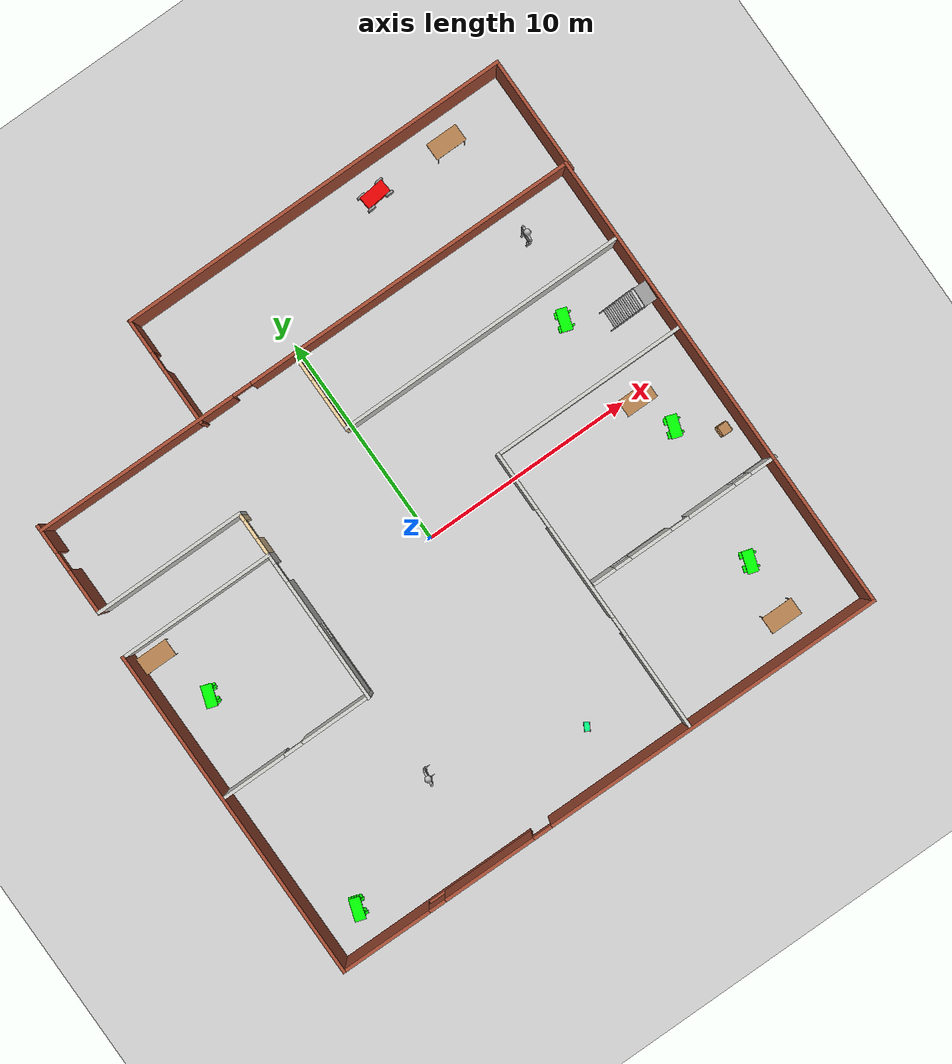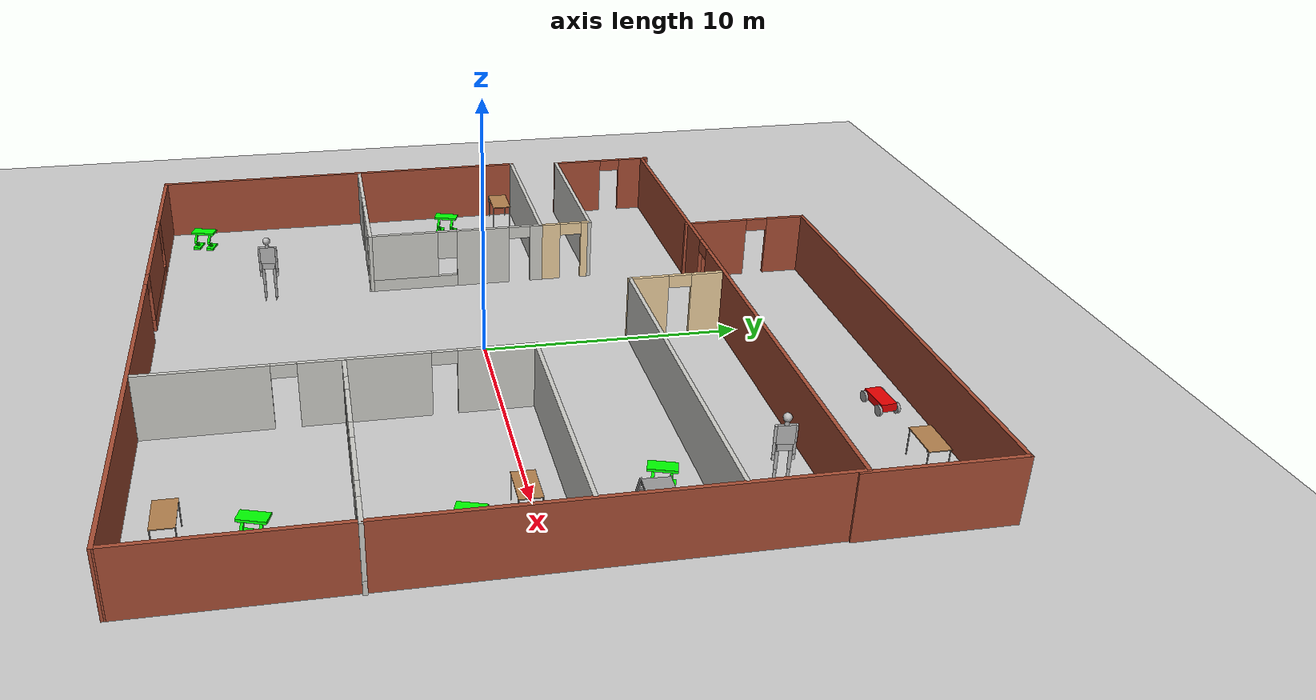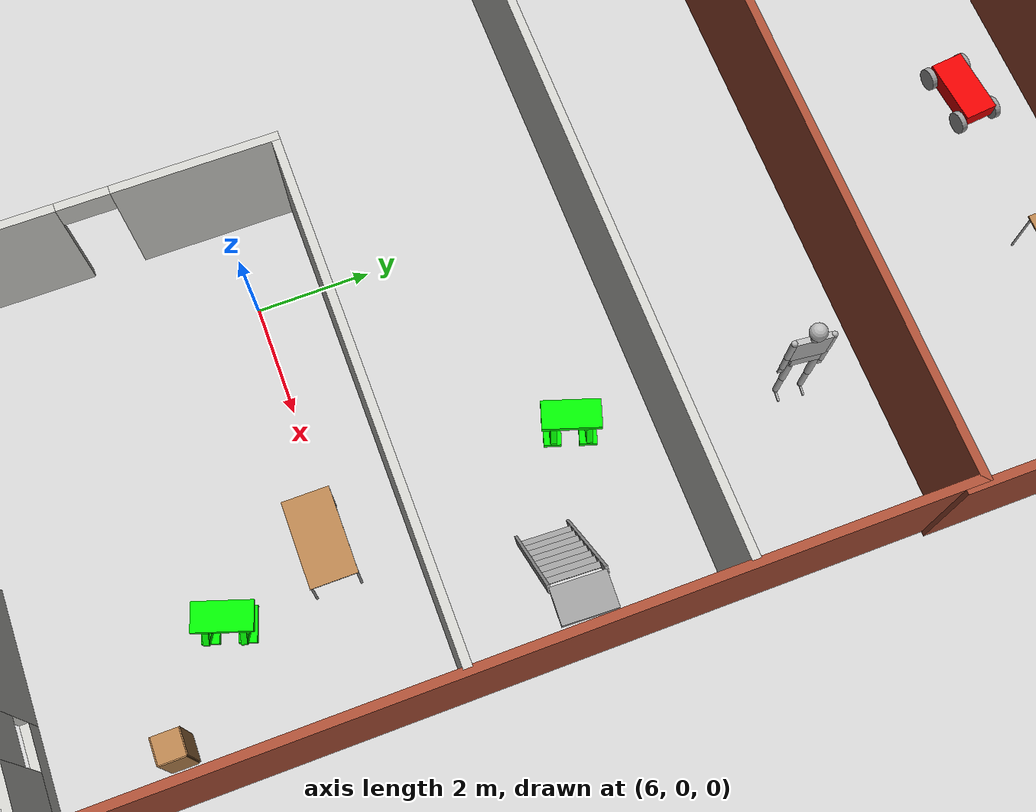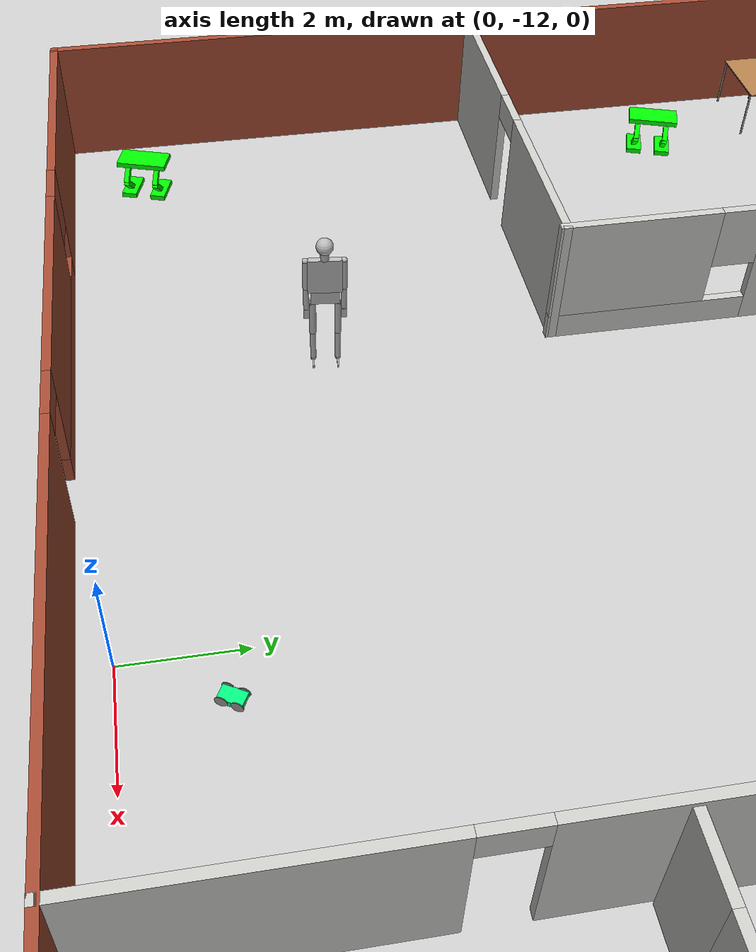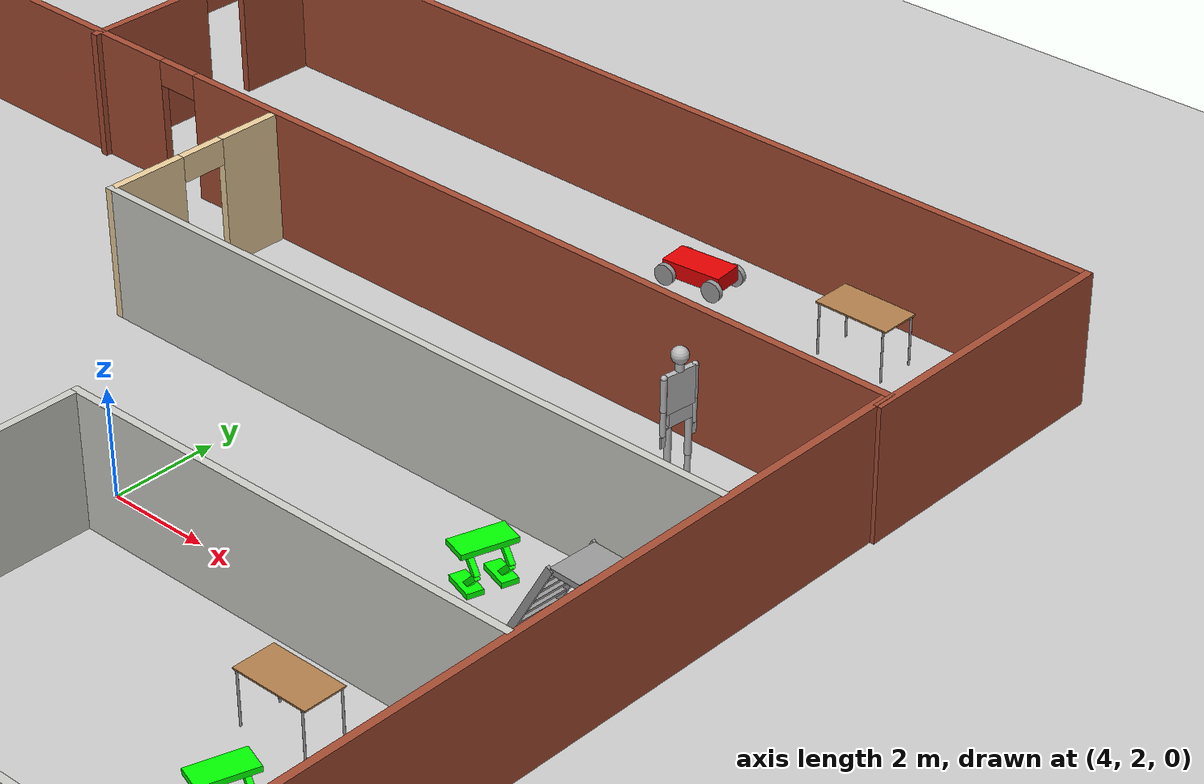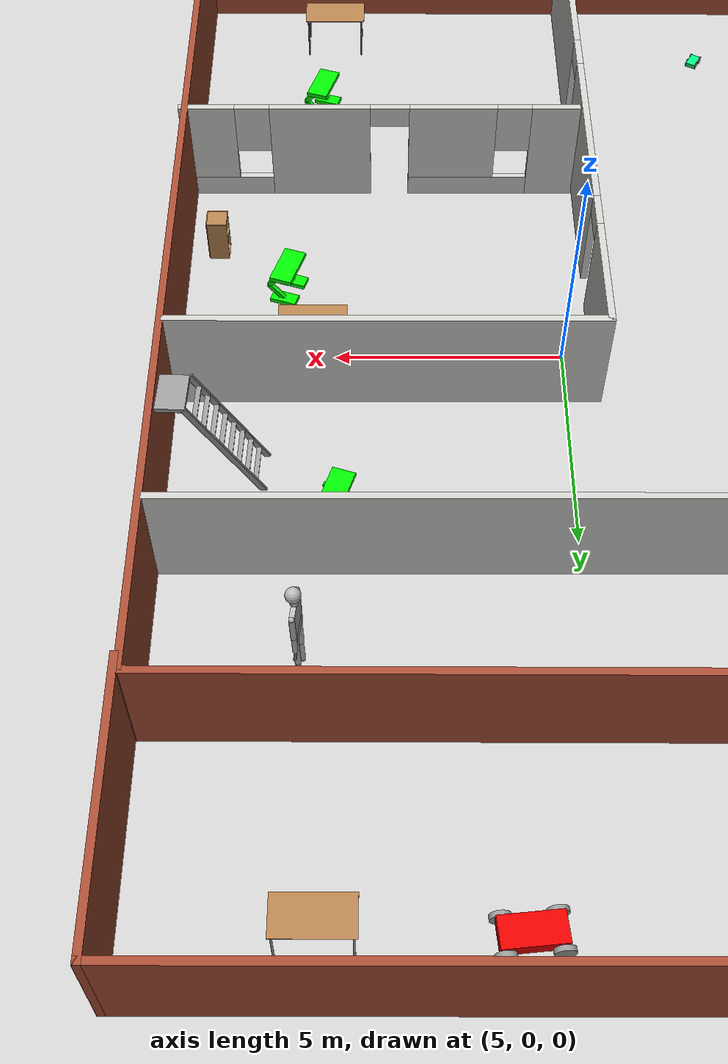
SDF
<sdf version="1.7">
 <world name="default">
  <plugin name="hello" filename="libhello.so"/>
  <light name="sun" type="directional">
   <pose>0 0 10 0 -0 0</pose>
   <diffuse>0.8 0.8 0.8 1</diffuse>
   <specular>0.2 0.2 0.2 1</specular>
   <attenuation>
    <range>1000</range>
    <constant>0.9</constant>
    <linear>0.01</linear>
    <quadratic>0.001</quadratic>
   </attenuation>
   <direction>-0.5 0.1 -0.9</direction>
   <spot><inner_angle>0</inner_angle><outer_angle>0</outer_angle><falloff>0</falloff></spot>
  </light>
  <model name="ground_plane">
   <static>1</static>
   <link name="link">
    <collision name="collision">
     <geometry><plane><normal>0 0 1</normal><size>100 100</size></plane></geometry>
     <surface>
      <contact><collide_bitmask>65535</collide_bitmask></contact>
      <friction><ode><mu>100</mu><mu2>50</mu2></ode></friction>
     </surface>
    </collision>
    <visual name="visual">
     <cast_shadows>0</cast_shadows>
     <geometry><plane><normal>0 0 1</normal><size>100 100</size></plane></geometry>
     <material>
      <script><uri>file://media/materials/scripts/gazebo.material</uri><name>Gazebo/Grey</name></script>
     </material>
    </visual>
   </link>
  </model>
  <gravity>0 0 -9.8</gravity>
  <magnetic_field>6e-06 2.3e-05 -4.2e-05</magnetic_field>
  <atmosphere type="adiabatic"/>
  <physics type="ode">
   <max_step_size>0.001</max_step_size>
   <real_time_factor>1</real_time_factor>
   <real_time_update_rate>1000</real_time_update_rate>
  </physics>
  <scene><ambient>0.4 0.4 0.4 1</ambient><background>0.7 0.7 0.7 1</background><shadows>1</shadows></scene>
  <spherical_coordinates>
   <surface_model>EARTH_WGS84</surface_model>
   <latitude_deg>0</latitude_deg>
   <longitude_deg>0</longitude_deg>
   <elevation>0</elevation>
   <heading_deg>0</heading_deg>
  </spherical_coordinates>
  <model name="newworld">
   <link name="Wall_37">
    <pose>-13.3996 -5.55678 0 0 0 -1.5708</pose>
    <visual name="Wall_37_Visual">
     <pose>0 0 1.25 0 -0 0</pose>
     <geometry><box><size>16 0.15 2.5</size></box></geometry>
     <material>
      <script><uri>file://media/materials/scripts/gazebo.material</uri><name>Gazebo/Bricks</name></script>
      <ambient>1 1 1 1</ambient>
      <shader type="pixel"/>
     </material>
     <meta><layer>0</layer></meta>
    </visual>
    <collision name="Wall_37_Collision">
     <pose>0 0 1.25 0 -0 0</pose>
     <geometry><box><size>16 0.15 2.5</size></box></geometry>
     <surface>
      <friction>
       <ode><mu>1</mu><mu2>1</mu2><fdir1>0 0 0</fdir1><slip1>0</slip1><slip2>0</slip2></ode>
       <torsional>
        <coefficient>1</coefficient>
        <patch_radius>0</patch_radius>
        <surface_radius>0</surface_radius>
        <use_patch_radius>1</use_patch_radius>
        <ode><slip>0</slip></ode>
       </torsional>
      </friction>
      <bounce><restitution_coefficient>0</restitution_coefficient><threshold>1e+06</threshold></bounce>
      <contact>
       <collide_without_contact>0</collide_without_contact>
       <collide_without_contact_bitmask>1</collide_without_contact_bitmask>
       <collide_bitmask>1</collide_bitmask>
       <ode>
        <soft_cfm>0</soft_cfm>
        <soft_erp>0.2</soft_erp>
        <kp>1e+13</kp>
        <kd>1</kd>
        <max_vel>0.01</max_vel>
        <min_depth>0</min_depth>
       </ode>
       <bullet>
        <split_impulse>1</split_impulse>
        <split_impulse_penetration_threshold>-0.01</split_impulse_penetration_threshold>
        <soft_cfm>0</soft_cfm>
        <soft_erp>0.2</soft_erp>
        <kp>1e+13</kp>
        <kd>1</kd>
       </bullet>
      </contact>
     </surface>
    </collision>
   </link>
   <link name="Wall_38">
    <pose>-0.039627 -13.5282 0 0 0 -0.003477</pose>
    <visual name="Wall_38_Visual_2">
     <pose>-6.41871 0 0.25 0 -0 0</pose>
     <geometry><box><size>5.24062 0.15 0.5</size></box></geometry>
     <material>
      <script><uri>file://media/materials/scripts/gazebo.material</uri><name>Gazebo/Bricks</name></script>
      <ambient>1 1 1 1</ambient>
      <shader type="pixel"/>
     </material>
     <meta><layer>0</layer></meta>
    </visual>
    <visual name="Wall_38_Visual_4">
     <pose>-8.63902 0 1.9 0 -0 0</pose>
     <geometry><box><size>0.8 0.15 1.2</size></box></geometry>
     <material>
      <script><uri>file://media/materials/scripts/gazebo.material</uri><name>Gazebo/Bricks</name></script>
      <ambient>1 1 1 1</ambient>
      <shader type="pixel"/>
     </material>
     <meta><layer>0</layer></meta>
    </visual>
    <visual name="Wall_38_Visual_0">
     <pose>-11.237 0 1.25 0 -0 0</pose>
     <geometry><box><size>4.39606 0.15 2.5</size></box></geometry>
     <material>
      <script><uri>file://media/materials/scripts/gazebo.material</uri><name>Gazebo/Bricks</name></script>
      <ambient>1 1 1 1</ambient>
      <shader type="pixel"/>
     </material>
     <meta><layer>0</layer></meta>
    </visual>
    <visual name="Wall_38_Visual_1">
     <pose>5.26834 0 1.25 0 -0 0</pose>
     <geometry><box><size>16.3335 0.15 2.5</size></box></geometry>
     <material>
      <script><uri>file://media/materials/scripts/gazebo.material</uri><name>Gazebo/Bricks</name></script>
      <ambient>1 1 1 1</ambient>
      <shader type="pixel"/>
     </material>
     <meta><layer>0</layer></meta>
    </visual>
    <visual name="Wall_38_Visual_3">
     <pose>-6.01871 0 1.5 0 -0 0</pose>
     <geometry><box><size>4.44062 0.15 2</size></box></geometry>
     <material>
      <script><uri>file://media/materials/scripts/gazebo.material</uri><name>Gazebo/Bricks</name></script>
      <ambient>1 1 1 1</ambient>
      <shader type="pixel"/>
     </material>
     <meta><layer>0</layer></meta>
    </visual>
    <visual name="Wall_38_Visual_5">
     <pose>-3.3484 0 2.25 0 -0 0</pose>
     <geometry><box><size>0.9 0.15 0.5</size></box></geometry>
     <material>
      <script><uri>file://media/materials/scripts/gazebo.material</uri><name>Gazebo/Bricks</name></script>
      <ambient>1 1 1 1</ambient>
      <shader type="pixel"/>
     </material>
     <meta><layer>0</layer></meta>
    </visual>
    <collision name="Wall_38_Collision_0">
     <pose>-11.237 0 1.25 0 -0 0</pose>
     <geometry><box><size>4.39606 0.15 2.5</size></box></geometry>
     <surface>
      <friction>
       <ode><mu>1</mu><mu2>1</mu2><fdir1>0 0 0</fdir1><slip1>0</slip1><slip2>0</slip2></ode>
       <torsional>
        <coefficient>1</coefficient>
        <patch_radius>0</patch_radius>
        <surface_radius>0</surface_radius>
        <use_patch_radius>1</use_patch_radius>
        <ode><slip>0</slip></ode>
       </torsional>
      </friction>
      <bounce><restitution_coefficient>0</restitution_coefficient><threshold>1e+06</threshold></bounce>
      <contact>
       <collide_without_contact>0</collide_without_contact>
       <collide_without_contact_bitmask>1</collide_without_contact_bitmask>
       <collide_bitmask>1</collide_bitmask>
       <ode>
        <soft_cfm>0</soft_cfm>
        <soft_erp>0.2</soft_erp>
        <kp>1e+13</kp>
        <kd>1</kd>
        <max_vel>0.01</max_vel>
        <min_depth>0</min_depth>
       </ode>
       <bullet>
        <split_impulse>1</split_impulse>
        <split_impulse_penetration_threshold>-0.01</split_impulse_penetration_threshold>
        <soft_cfm>0</soft_cfm>
        <soft_erp>0.2</soft_erp>
        <kp>1e+13</kp>
        <kd>1</kd>
       </bullet>
      </contact>
     </surface>
    </collision>
    <collision name="Wall_38_Collision_2">
     <pose>-6.41871 0 0.25 0 -0 0</pose>
     <geometry><box><size>5.24062 0.15 0.5</size></box></geometry>
     <surface>
      <friction>
       <ode><mu>1</mu><mu2>1</mu2><fdir1>0 0 0</fdir1><slip1>0</slip1><slip2>0</slip2></ode>
       <torsional>
        <coefficient>1</coefficient>
        <patch_radius>0</patch_radius>
        <surface_radius>0</surface_radius>
        <use_patch_radius>1</use_patch_radius>
        <ode><slip>0</slip></ode>
       </torsional>
      </friction>
      <bounce><restitution_coefficient>0</restitution_coefficient><threshold>1e+06</threshold></bounce>
      <contact>
       <collide_without_contact>0</collide_without_contact>
       <collide_without_contact_bitmask>1</collide_without_contact_bitmask>
       <collide_bitmask>1</collide_bitmask>
       <ode>
        <soft_cfm>0</soft_cfm>
        <soft_erp>0.2</soft_erp>
        <kp>1e+13</kp>
        <kd>1</kd>
        <max_vel>0.01</max_vel>
        <min_depth>0</min_depth>
       </ode>
       <bullet>
        <split_impulse>1</split_impulse>
        <split_impulse_penetration_threshold>-0.01</split_impulse_penetration_threshold>
        <soft_cfm>0</soft_cfm>
        <soft_erp>0.2</soft_erp>
        <kp>1e+13</kp>
        <kd>1</kd>
       </bullet>
      </contact>
     </surface>
    </collision>
    <collision name="Wall_38_Collision_5">
     <pose>-3.3484 0 2.25 0 -0 0</pose>
     <geometry><box><size>0.9 0.15 0.5</size></box></geometry>
     <surface>
      <friction>
       <ode><mu>1</mu><mu2>1</mu2><fdir1>0 0 0</fdir1><slip1>0</slip1><slip2>0</slip2></ode>
       <torsional>
        <coefficient>1</coefficient>
        <patch_radius>0</patch_radius>
        <surface_radius>0</surface_radius>
        <use_patch_radius>1</use_patch_radius>
        <ode><slip>0</slip></ode>
       </torsional>
      </friction>
      <bounce><restitution_coefficient>0</restitution_coefficient><threshold>1e+06</threshold></bounce>
      <contact>
       <collide_without_contact>0</collide_without_contact>
       <collide_without_contact_bitmask>1</collide_without_contact_bitmask>
       <collide_bitmask>1</collide_bitmask>
       <ode>
        <soft_cfm>0</soft_cfm>
        <soft_erp>0.2</soft_erp>
        <kp>1e+13</kp>
        <kd>1</kd>
        <max_vel>0.01</max_vel>
        <min_depth>0</min_depth>
       </ode>
       <bullet>
        <split_impulse>1</split_impulse>
        <split_impulse_penetration_threshold>-0.01</split_impulse_penetration_threshold>
        <soft_cfm>0</soft_cfm>
        <soft_erp>0.2</soft_erp>
        <kp>1e+13</kp>
        <kd>1</kd>
       </bullet>
      </contact>
     </surface>
    </collision>
    <collision name="Wall_38_Collision_4">
     <pose>-8.63902 0 1.9 0 -0 0</pose>
     <geometry><box><size>0.8 0.15 1.2</size></box></geometry>
     <surface>
      <friction>
       <ode><mu>1</mu><mu2>1</mu2><fdir1>0 0 0</fdir1><slip1>0</slip1><slip2>0</slip2></ode>
       <torsional>
        <coefficient>1</coefficient>
        <patch_radius>0</patch_radius>
        <surface_radius>0</surface_radius>
        <use_patch_radius>1</use_patch_radius>
        <ode><slip>0</slip></ode>
       </torsional>
      </friction>
      <bounce><restitution_coefficient>0</restitution_coefficient><threshold>1e+06</threshold></bounce>
      <contact>
       <collide_without_contact>0</collide_without_contact>
       <collide_without_contact_bitmask>1</collide_without_contact_bitmask>
       <collide_bitmask>1</collide_bitmask>
       <ode>
        <soft_cfm>0</soft_cfm>
        <soft_erp>0.2</soft_erp>
        <kp>1e+13</kp>
        <kd>1</kd>
        <max_vel>0.01</max_vel>
        <min_depth>0</min_depth>
       </ode>
       <bullet>
        <split_impulse>1</split_impulse>
        <split_impulse_penetration_threshold>-0.01</split_impulse_penetration_threshold>
        <soft_cfm>0</soft_cfm>
        <soft_erp>0.2</soft_erp>
        <kp>1e+13</kp>
        <kd>1</kd>
       </bullet>
      </contact>
     </surface>
    </collision>
    <collision name="Wall_38_Collision_3">
     <pose>-6.01871 0 1.5 0 -0 0</pose>
     <geometry><box><size>4.44062 0.15 2</size></box></geometry>
     <surface>
      <friction>
       <ode><mu>1</mu><mu2>1</mu2><fdir1>0 0 0</fdir1><slip1>0</slip1><slip2>0</slip2></ode>
       <torsional>
        <coefficient>1</coefficient>
        <patch_radius>0</patch_radius>
        <surface_radius>0</surface_radius>
        <use_patch_radius>1</use_patch_radius>
        <ode><slip>0</slip></ode>
       </torsional>
      </friction>
      <bounce><restitution_coefficient>0</restitution_coefficient><threshold>1e+06</threshold></bounce>
      <contact>
       <collide_without_contact>0</collide_without_contact>
       <collide_without_contact_bitmask>1</collide_without_contact_bitmask>
       <collide_bitmask>1</collide_bitmask>
       <ode>
        <soft_cfm>0</soft_cfm>
        <soft_erp>0.2</soft_erp>
        <kp>1e+13</kp>
        <kd>1</kd>
        <max_vel>0.01</max_vel>
        <min_depth>0</min_depth>
       </ode>
       <bullet>
        <split_impulse>1</split_impulse>
        <split_impulse_penetration_threshold>-0.01</split_impulse_penetration_threshold>
        <soft_cfm>0</soft_cfm>
        <soft_erp>0.2</soft_erp>
        <kp>1e+13</kp>
        <kd>1</kd>
       </bullet>
      </contact>
     </surface>
    </collision>
    <collision name="Wall_38_Collision_1">
     <pose>5.26834 0 1.25 0 -0 0</pose>
     <geometry><box><size>16.3335 0.15 2.5</size></box></geometry>
     <surface>
      <friction>
       <ode><mu>1</mu><mu2>1</mu2><fdir1>0 0 0</fdir1><slip1>0</slip1><slip2>0</slip2></ode>
       <torsional>
        <coefficient>1</coefficient>
        <patch_radius>0</patch_radius>
        <surface_radius>0</surface_radius>
        <use_patch_radius>1</use_patch_radius>
        <ode><slip>0</slip></ode>
       </torsional>
      </friction>
      <bounce><restitution_coefficient>0</restitution_coefficient><threshold>1e+06</threshold></bounce>
      <contact>
       <collide_without_contact>0</collide_without_contact>
       <collide_without_contact_bitmask>1</collide_without_contact_bitmask>
       <collide_bitmask>1</collide_bitmask>
       <ode>
        <soft_cfm>0</soft_cfm>
        <soft_erp>0.2</soft_erp>
        <kp>1e+13</kp>
        <kd>1</kd>
        <max_vel>0.01</max_vel>
        <min_depth>0</min_depth>
       </ode>
       <bullet>
        <split_impulse>1</split_impulse>
        <split_impulse_penetration_threshold>-0.01</split_impulse_penetration_threshold>
        <soft_cfm>0</soft_cfm>
        <soft_erp>0.2</soft_erp>
        <kp>1e+13</kp>
        <kd>1</kd>
       </bullet>
      </contact>
     </surface>
    </collision>
   </link>
   <link name="Wall_39">
    <pose>13.3204 -2.52468 0 0 -0 1.5708</pose>
    <visual name="Wall_39_Visual">
     <pose>0 0 1.25 0 -0 0</pose>
     <geometry><box><size>22.25 0.15 2.5</size></box></geometry>
     <material>
      <script><uri>file://media/materials/scripts/gazebo.material</uri><name>Gazebo/Bricks</name></script>
      <ambient>1 1 1 1</ambient>
      <shader type="pixel"/>
     </material>
     <meta><layer>0</layer></meta>
    </visual>
    <collision name="Wall_39_Collision">
     <pose>0 0 1.25 0 -0 0</pose>
     <geometry><box><size>22.25 0.15 2.5</size></box></geometry>
     <surface>
      <friction>
       <ode><mu>1</mu><mu2>1</mu2><fdir1>0 0 0</fdir1><slip1>0</slip1><slip2>0</slip2></ode>
       <torsional>
        <coefficient>1</coefficient>
        <patch_radius>0</patch_radius>
        <surface_radius>0</surface_radius>
        <use_patch_radius>1</use_patch_radius>
        <ode><slip>0</slip></ode>
       </torsional>
      </friction>
      <bounce><restitution_coefficient>0</restitution_coefficient><threshold>1e+06</threshold></bounce>
      <contact>
       <collide_without_contact>0</collide_without_contact>
       <collide_without_contact_bitmask>1</collide_without_contact_bitmask>
       <collide_bitmask>1</collide_bitmask>
       <ode>
        <soft_cfm>0</soft_cfm>
        <soft_erp>0.2</soft_erp>
        <kp>1e+13</kp>
        <kd>1</kd>
        <max_vel>0.01</max_vel>
        <min_depth>0</min_depth>
       </ode>
       <bullet>
        <split_impulse>1</split_impulse>
        <split_impulse_penetration_threshold>-0.01</split_impulse_penetration_threshold>
        <soft_cfm>0</soft_cfm>
        <soft_erp>0.2</soft_erp>
        <kp>1e+13</kp>
        <kd>1</kd>
       </bullet>
      </contact>
     </surface>
    </collision>
   </link>
   <link name="Wall_40">
    <pose>0.085373 8.57177 0 0 -0 3.13808</pose>
    <visual name="Wall_40_Visual_2">
     <pose>3.09238 0 2.25 0 -0 0</pose>
     <geometry><box><size>0.9 0.15 0.5</size></box></geometry>
     <material>
      <script><uri>file://media/materials/scripts/gazebo.material</uri><name>Gazebo/Bricks</name></script>
      <ambient>1 1 1 1</ambient>
      <shader type="pixel"/>
     </material>
     <meta><layer>0</layer></meta>
    </visual>
    <visual name="Wall_40_Visual_0">
     <pose>-5.33385 0 1.25 0 -0 0</pose>
     <geometry><box><size>15.9525 0.15 2.5</size></box></geometry>
     <material>
      <script><uri>file://media/materials/scripts/gazebo.material</uri><name>Gazebo/Bricks</name></script>
      <ambient>1 1 1 1</ambient>
      <shader type="pixel"/>
     </material>
     <meta><layer>0</layer></meta>
    </visual>
    <visual name="Wall_40_Visual_1">
     <pose>8.42623 0 1.25 0 -0 0</pose>
     <geometry><box><size>9.76771 0.15 2.5</size></box></geometry>
     <material>
      <script><uri>file://media/materials/scripts/gazebo.material</uri><name>Gazebo/Bricks</name></script>
      <ambient>1 1 1 1</ambient>
      <shader type="pixel"/>
     </material>
     <meta><layer>0</layer></meta>
    </visual>
    <collision name="Wall_40_Collision_0">
     <pose>-5.33385 0 1.25 0 -0 0</pose>
     <geometry><box><size>15.9525 0.15 2.5</size></box></geometry>
     <surface>
      <friction>
       <ode><mu>1</mu><mu2>1</mu2><fdir1>0 0 0</fdir1><slip1>0</slip1><slip2>0</slip2></ode>
       <torsional>
        <coefficient>1</coefficient>
        <patch_radius>0</patch_radius>
        <surface_radius>0</surface_radius>
        <use_patch_radius>1</use_patch_radius>
        <ode><slip>0</slip></ode>
       </torsional>
      </friction>
      <bounce><restitution_coefficient>0</restitution_coefficient><threshold>1e+06</threshold></bounce>
      <contact>
       <collide_without_contact>0</collide_without_contact>
       <collide_without_contact_bitmask>1</collide_without_contact_bitmask>
       <collide_bitmask>1</collide_bitmask>
       <ode>
        <soft_cfm>0</soft_cfm>
        <soft_erp>0.2</soft_erp>
        <kp>1e+13</kp>
        <kd>1</kd>
        <max_vel>0.01</max_vel>
        <min_depth>0</min_depth>
       </ode>
       <bullet>
        <split_impulse>1</split_impulse>
        <split_impulse_penetration_threshold>-0.01</split_impulse_penetration_threshold>
        <soft_cfm>0</soft_cfm>
        <soft_erp>0.2</soft_erp>
        <kp>1e+13</kp>
        <kd>1</kd>
       </bullet>
      </contact>
     </surface>
    </collision>
    <collision name="Wall_40_Collision_1">
     <pose>8.42623 0 1.25 0 -0 0</pose>
     <geometry><box><size>9.76771 0.15 2.5</size></box></geometry>
     <surface>
      <friction>
       <ode><mu>1</mu><mu2>1</mu2><fdir1>0 0 0</fdir1><slip1>0</slip1><slip2>0</slip2></ode>
       <torsional>
        <coefficient>1</coefficient>
        <patch_radius>0</patch_radius>
        <surface_radius>0</surface_radius>
        <use_patch_radius>1</use_patch_radius>
        <ode><slip>0</slip></ode>
       </torsional>
      </friction>
      <bounce><restitution_coefficient>0</restitution_coefficient><threshold>1e+06</threshold></bounce>
      <contact>
       <collide_without_contact>0</collide_without_contact>
       <collide_without_contact_bitmask>1</collide_without_contact_bitmask>
       <collide_bitmask>1</collide_bitmask>
       <ode>
        <soft_cfm>0</soft_cfm>
        <soft_erp>0.2</soft_erp>
        <kp>1e+13</kp>
        <kd>1</kd>
        <max_vel>0.01</max_vel>
        <min_depth>0</min_depth>
       </ode>
       <bullet>
        <split_impulse>1</split_impulse>
        <split_impulse_penetration_threshold>-0.01</split_impulse_penetration_threshold>
        <soft_cfm>0</soft_cfm>
        <soft_erp>0.2</soft_erp>
        <kp>1e+13</kp>
        <kd>1</kd>
       </bullet>
      </contact>
     </surface>
    </collision>
    <collision name="Wall_40_Collision_2">
     <pose>3.09238 0 2.25 0 -0 0</pose>
     <geometry><box><size>0.9 0.15 0.5</size></box></geometry>
     <surface>
      <friction>
       <ode><mu>1</mu><mu2>1</mu2><fdir1>0 0 0</fdir1><slip1>0</slip1><slip2>0</slip2></ode>
       <torsional>
        <coefficient>1</coefficient>
        <patch_radius>0</patch_radius>
        <surface_radius>0</surface_radius>
        <use_patch_radius>1</use_patch_radius>
        <ode><slip>0</slip></ode>
       </torsional>
      </friction>
      <bounce><restitution_coefficient>0</restitution_coefficient><threshold>1e+06</threshold></bounce>
      <contact>
       <collide_without_contact>0</collide_without_contact>
       <collide_without_contact_bitmask>1</collide_without_contact_bitmask>
       <collide_bitmask>1</collide_bitmask>
       <ode>
        <soft_cfm>0</soft_cfm>
        <soft_erp>0.2</soft_erp>
        <kp>1e+13</kp>
        <kd>1</kd>
        <max_vel>0.01</max_vel>
        <min_depth>0</min_depth>
       </ode>
       <bullet>
        <split_impulse>1</split_impulse>
        <split_impulse_penetration_threshold>-0.01</split_impulse_penetration_threshold>
        <soft_cfm>0</soft_cfm>
        <soft_erp>0.2</soft_erp>
        <kp>1e+13</kp>
        <kd>1</kd>
       </bullet>
      </contact>
     </surface>
    </collision>
   </link>
   <link name="Wall_43">
    <pose>-9.72463 2.36822 0 0 -0 0</pose>
    <visual name="Wall_43_Visual">
     <pose>0 0 1.25 0 -0 0</pose>
     <geometry><box><size>7.5 0.15 2.5</size></box></geometry>
     <material>
      <script><uri>file://media/materials/scripts/gazebo.material</uri><name>Gazebo/CeilingTiled</name></script>
      <ambient>0.996078 0.47451 0.0196078 1</ambient>
      <shader type="pixel"/>
     </material>
     <meta><layer>0</layer></meta>
    </visual>
    <collision name="Wall_43_Collision">
     <pose>0 0 1.25 0 -0 0</pose>
     <geometry><box><size>7.5 0.15 2.5</size></box></geometry>
     <surface>
      <friction>
       <ode><mu>1</mu><mu2>1</mu2><fdir1>0 0 0</fdir1><slip1>0</slip1><slip2>0</slip2></ode>
       <torsional>
        <coefficient>1</coefficient>
        <patch_radius>0</patch_radius>
        <surface_radius>0</surface_radius>
        <use_patch_radius>1</use_patch_radius>
        <ode><slip>0</slip></ode>
       </torsional>
      </friction>
      <bounce><restitution_coefficient>0</restitution_coefficient><threshold>1e+06</threshold></bounce>
      <contact>
       <collide_without_contact>0</collide_without_contact>
       <collide_without_contact_bitmask>1</collide_without_contact_bitmask>
       <collide_bitmask>1</collide_bitmask>
       <ode>
        <soft_cfm>0</soft_cfm>
        <soft_erp>0.2</soft_erp>
        <kp>1e+13</kp>
        <kd>1</kd>
        <max_vel>0.01</max_vel>
        <min_depth>0</min_depth>
       </ode>
       <bullet>
        <split_impulse>1</split_impulse>
        <split_impulse_penetration_threshold>-0.01</split_impulse_penetration_threshold>
        <soft_cfm>0</soft_cfm>
        <soft_erp>0.2</soft_erp>
        <kp>1e+13</kp>
        <kd>1</kd>
       </bullet>
      </contact>
     </surface>
    </collision>
   </link>
   <link name="Wall_44">
    <pose>-6.04963 3.41822 0 0 -0 1.5708</pose>
    <visual name="Wall_44_Visual_0">
     <pose>-0.670296 0 1.25 0 -0 0</pose>
     <geometry><box><size>0.909407 0.15 2.5</size></box></geometry>
     <material>
      <script><uri>file://media/materials/scripts/gazebo.material</uri><name>Gazebo/Grey</name></script>
      <ambient>0.921569 0.807843 0.615686 1</ambient>
      <shader type="pixel"/>
     </material>
     <meta><layer>0</layer></meta>
    </visual>
    <visual name="Wall_44_Visual_1">
     <pose>0.904704 0 1.25 0 -0 0</pose>
     <geometry><box><size>0.440593 0.15 2.5</size></box></geometry>
     <material>
      <script><uri>file://media/materials/scripts/gazebo.material</uri><name>Gazebo/Grey</name></script>
      <ambient>0.921569 0.807843 0.615686 1</ambient>
      <shader type="pixel"/>
     </material>
     <meta><layer>0</layer></meta>
    </visual>
    <visual name="Wall_44_Visual_2">
     <pose>0.234407 0 2.25 0 -0 0</pose>
     <geometry><box><size>0.9 0.15 0.5</size></box></geometry>
     <material>
      <script><uri>file://media/materials/scripts/gazebo.material</uri><name>Gazebo/Grey</name></script>
      <ambient>0.921569 0.807843 0.615686 1</ambient>
      <shader type="pixel"/>
     </material>
     <meta><layer>0</layer></meta>
    </visual>
    <collision name="Wall_44_Collision_0">
     <pose>-0.670296 0 1.25 0 -0 0</pose>
     <geometry><box><size>0.909407 0.15 2.5</size></box></geometry>
     <surface>
      <friction>
       <ode><mu>1</mu><mu2>1</mu2><fdir1>0 0 0</fdir1><slip1>0</slip1><slip2>0</slip2></ode>
       <torsional>
        <coefficient>1</coefficient>
        <patch_radius>0</patch_radius>
        <surface_radius>0</surface_radius>
        <use_patch_radius>1</use_patch_radius>
        <ode><slip>0</slip></ode>
       </torsional>
      </friction>
      <bounce><restitution_coefficient>0</restitution_coefficient><threshold>1e+06</threshold></bounce>
      <contact>
       <collide_without_contact>0</collide_without_contact>
       <collide_without_contact_bitmask>1</collide_without_contact_bitmask>
       <collide_bitmask>1</collide_bitmask>
       <ode>
        <soft_cfm>0</soft_cfm>
        <soft_erp>0.2</soft_erp>
        <kp>1e+13</kp>
        <kd>1</kd>
        <max_vel>0.01</max_vel>
        <min_depth>0</min_depth>
       </ode>
       <bullet>
        <split_impulse>1</split_impulse>
        <split_impulse_penetration_threshold>-0.01</split_impulse_penetration_threshold>
        <soft_cfm>0</soft_cfm>
        <soft_erp>0.2</soft_erp>
        <kp>1e+13</kp>
        <kd>1</kd>
       </bullet>
      </contact>
     </surface>
    </collision>
    <collision name="Wall_44_Collision_2">
     <pose>0.234407 0 2.25 0 -0 0</pose>
     <geometry><box><size>0.9 0.15 0.5</size></box></geometry>
     <surface>
      <friction>
       <ode><mu>1</mu><mu2>1</mu2><fdir1>0 0 0</fdir1><slip1>0</slip1><slip2>0</slip2></ode>
       <torsional>
        <coefficient>1</coefficient>
        <patch_radius>0</patch_radius>
        <surface_radius>0</surface_radius>
        <use_patch_radius>1</use_patch_radius>
        <ode><slip>0</slip></ode>
       </torsional>
      </friction>
      <bounce><restitution_coefficient>0</restitution_coefficient><threshold>1e+06</threshold></bounce>
      <contact>
       <collide_without_contact>0</collide_without_contact>
       <collide_without_contact_bitmask>1</collide_without_contact_bitmask>
       <collide_bitmask>1</collide_bitmask>
       <ode>
        <soft_cfm>0</soft_cfm>
        <soft_erp>0.2</soft_erp>
        <kp>1e+13</kp>
        <kd>1</kd>
        <max_vel>0.01</max_vel>
        <min_depth>0</min_depth>
       </ode>
       <bullet>
        <split_impulse>1</split_impulse>
        <split_impulse_penetration_threshold>-0.01</split_impulse_penetration_threshold>
        <soft_cfm>0</soft_cfm>
        <soft_erp>0.2</soft_erp>
        <kp>1e+13</kp>
        <kd>1</kd>
       </bullet>
      </contact>
     </surface>
    </collision>
    <collision name="Wall_44_Collision_1">
     <pose>0.904704 0 1.25 0 -0 0</pose>
     <geometry><box><size>0.440593 0.15 2.5</size></box></geometry>
     <surface>
      <friction>
       <ode><mu>1</mu><mu2>1</mu2><fdir1>0 0 0</fdir1><slip1>0</slip1><slip2>0</slip2></ode>
       <torsional>
        <coefficient>1</coefficient>
        <patch_radius>0</patch_radius>
        <surface_radius>0</surface_radius>
        <use_patch_radius>1</use_patch_radius>
        <ode><slip>0</slip></ode>
       </torsional>
      </friction>
      <bounce><restitution_coefficient>0</restitution_coefficient><threshold>1e+06</threshold></bounce>
      <contact>
       <collide_without_contact>0</collide_without_contact>
       <collide_without_contact_bitmask>1</collide_without_contact_bitmask>
       <collide_bitmask>1</collide_bitmask>
       <ode>
        <soft_cfm>0</soft_cfm>
        <soft_erp>0.2</soft_erp>
        <kp>1e+13</kp>
        <kd>1</kd>
        <max_vel>0.01</max_vel>
        <min_depth>0</min_depth>
       </ode>
       <bullet>
        <split_impulse>1</split_impulse>
        <split_impulse_penetration_threshold>-0.01</split_impulse_penetration_threshold>
        <soft_cfm>0</soft_cfm>
        <soft_erp>0.2</soft_erp>
        <kp>1e+13</kp>
        <kd>1</kd>
       </bullet>
      </contact>
     </surface>
    </collision>
   </link>
   <link name="Wall_45">
    <pose>-9.59963 4.46822 0 0 -0 3.14159</pose>
    <visual name="Wall_45_Visual">
     <pose>0 0 1.25 0 -0 0</pose>
     <geometry><box><size>7.25 0.15 2.5</size></box></geometry>
     <material>
      <script><uri>file://media/materials/scripts/gazebo.material</uri><name>Gazebo/CeilingTiled</name></script>
      <ambient>0.921569 0.807843 0.615686 1</ambient>
      <shader type="pixel"/>
     </material>
     <meta><layer>0</layer></meta>
    </visual>
    <collision name="Wall_45_Collision">
     <pose>0 0 1.25 0 -0 0</pose>
     <geometry><box><size>7.25 0.15 2.5</size></box></geometry>
     <surface>
      <friction>
       <ode><mu>1</mu><mu2>1</mu2><fdir1>0 0 0</fdir1><slip1>0</slip1><slip2>0</slip2></ode>
       <torsional>
        <coefficient>1</coefficient>
        <patch_radius>0</patch_radius>
        <surface_radius>0</surface_radius>
        <use_patch_radius>1</use_patch_radius>
        <ode><slip>0</slip></ode>
       </torsional>
      </friction>
      <bounce><restitution_coefficient>0</restitution_coefficient><threshold>1e+06</threshold></bounce>
      <contact>
       <collide_without_contact>0</collide_without_contact>
       <collide_without_contact_bitmask>1</collide_without_contact_bitmask>
       <collide_bitmask>1</collide_bitmask>
       <ode>
        <soft_cfm>0</soft_cfm>
        <soft_erp>0.2</soft_erp>
        <kp>1e+13</kp>
        <kd>1</kd>
        <max_vel>0.01</max_vel>
        <min_depth>0</min_depth>
       </ode>
       <bullet>
        <split_impulse>1</split_impulse>
        <split_impulse_penetration_threshold>-0.01</split_impulse_penetration_threshold>
        <soft_cfm>0</soft_cfm>
        <soft_erp>0.2</soft_erp>
        <kp>1e+13</kp>
        <kd>1</kd>
       </bullet>
      </contact>
     </surface>
    </collision>
   </link>
   <link name="Wall_46">
    <pose>-13.1496 6.64322 0 0 -0 1.5708</pose>
    <visual name="Wall_46_Visual_1">
     <pose>1.54605 0 1.25 0 -0 0</pose>
     <geometry><box><size>1.4079 0.15 2.5</size></box></geometry>
     <material>
      <script><uri>file://media/materials/scripts/gazebo.material</uri><name>Gazebo/Bricks</name></script>
      <ambient>1 1 1 1</ambient>
      <shader type="pixel"/>
     </material>
     <meta><layer>0</layer></meta>
    </visual>
    <visual name="Wall_46_Visual_0">
     <pose>-1.15395 0 1.25 0 -0 0</pose>
     <geometry><box><size>2.1921 0.15 2.5</size></box></geometry>
     <material>
      <script><uri>file://media/materials/scripts/gazebo.material</uri><name>Gazebo/Bricks</name></script>
      <ambient>1 1 1 1</ambient>
      <shader type="pixel"/>
     </material>
     <meta><layer>0</layer></meta>
    </visual>
    <visual name="Wall_46_Visual_2">
     <pose>0.392097 0 2.25 0 -0 0</pose>
     <geometry><box><size>0.9 0.15 0.5</size></box></geometry>
     <material>
      <script><uri>file://media/materials/scripts/gazebo.material</uri><name>Gazebo/Bricks</name></script>
      <ambient>1 1 1 1</ambient>
      <shader type="pixel"/>
     </material>
     <meta><layer>0</layer></meta>
    </visual>
    <collision name="Wall_46_Collision_2">
     <pose>0.392097 0 2.25 0 -0 0</pose>
     <geometry><box><size>0.9 0.15 0.5</size></box></geometry>
     <surface>
      <friction>
       <ode><mu>1</mu><mu2>1</mu2><fdir1>0 0 0</fdir1><slip1>0</slip1><slip2>0</slip2></ode>
       <torsional>
        <coefficient>1</coefficient>
        <patch_radius>0</patch_radius>
        <surface_radius>0</surface_radius>
        <use_patch_radius>1</use_patch_radius>
        <ode><slip>0</slip></ode>
       </torsional>
      </friction>
      <bounce><restitution_coefficient>0</restitution_coefficient><threshold>1e+06</threshold></bounce>
      <contact>
       <collide_without_contact>0</collide_without_contact>
       <collide_without_contact_bitmask>1</collide_without_contact_bitmask>
       <collide_bitmask>1</collide_bitmask>
       <ode>
        <soft_cfm>0</soft_cfm>
        <soft_erp>0.2</soft_erp>
        <kp>1e+13</kp>
        <kd>1</kd>
        <max_vel>0.01</max_vel>
        <min_depth>0</min_depth>
       </ode>
       <bullet>
        <split_impulse>1</split_impulse>
        <split_impulse_penetration_threshold>-0.01</split_impulse_penetration_threshold>
        <soft_cfm>0</soft_cfm>
        <soft_erp>0.2</soft_erp>
        <kp>1e+13</kp>
        <kd>1</kd>
       </bullet>
      </contact>
     </surface>
    </collision>
    <collision name="Wall_46_Collision_0">
     <pose>-1.15395 0 1.25 0 -0 0</pose>
     <geometry><box><size>2.1921 0.15 2.5</size></box></geometry>
     <surface>
      <friction>
       <ode><mu>1</mu><mu2>1</mu2><fdir1>0 0 0</fdir1><slip1>0</slip1><slip2>0</slip2></ode>
       <torsional>
        <coefficient>1</coefficient>
        <patch_radius>0</patch_radius>
        <surface_radius>0</surface_radius>
        <use_patch_radius>1</use_patch_radius>
        <ode><slip>0</slip></ode>
       </torsional>
      </friction>
      <bounce><restitution_coefficient>0</restitution_coefficient><threshold>1e+06</threshold></bounce>
      <contact>
       <collide_without_contact>0</collide_without_contact>
       <collide_without_contact_bitmask>1</collide_without_contact_bitmask>
       <collide_bitmask>1</collide_bitmask>
       <ode>
        <soft_cfm>0</soft_cfm>
        <soft_erp>0.2</soft_erp>
        <kp>1e+13</kp>
        <kd>1</kd>
        <max_vel>0.01</max_vel>
        <min_depth>0</min_depth>
       </ode>
       <bullet>
        <split_impulse>1</split_impulse>
        <split_impulse_penetration_threshold>-0.01</split_impulse_penetration_threshold>
        <soft_cfm>0</soft_cfm>
        <soft_erp>0.2</soft_erp>
        <kp>1e+13</kp>
        <kd>1</kd>
       </bullet>
      </contact>
     </surface>
    </collision>
    <collision name="Wall_46_Collision_1">
     <pose>1.54605 0 1.25 0 -0 0</pose>
     <geometry><box><size>1.4079 0.15 2.5</size></box></geometry>
     <surface>
      <friction>
       <ode><mu>1</mu><mu2>1</mu2><fdir1>0 0 0</fdir1><slip1>0</slip1><slip2>0</slip2></ode>
       <torsional>
        <coefficient>1</coefficient>
        <patch_radius>0</patch_radius>
        <surface_radius>0</surface_radius>
        <use_patch_radius>1</use_patch_radius>
        <ode><slip>0</slip></ode>
       </torsional>
      </friction>
      <bounce><restitution_coefficient>0</restitution_coefficient><threshold>1e+06</threshold></bounce>
      <contact>
       <collide_without_contact>0</collide_without_contact>
       <collide_without_contact_bitmask>1</collide_without_contact_bitmask>
       <collide_bitmask>1</collide_bitmask>
       <ode>
        <soft_cfm>0</soft_cfm>
        <soft_erp>0.2</soft_erp>
        <kp>1e+13</kp>
        <kd>1</kd>
        <max_vel>0.01</max_vel>
        <min_depth>0</min_depth>
       </ode>
       <bullet>
        <split_impulse>1</split_impulse>
        <split_impulse_penetration_threshold>-0.01</split_impulse_penetration_threshold>
        <soft_cfm>0</soft_cfm>
        <soft_erp>0.2</soft_erp>
        <kp>1e+13</kp>
        <kd>1</kd>
       </bullet>
      </contact>
     </surface>
    </collision>
   </link>
   <link name="Wall_48">
    <pose>4.11037 -6.62501 0 0 -0 1.5708</pose>
    <visual name="Wall_48_Visual_1">
     <pose>0.963424 0 1.25 0 -0 0</pose>
     <geometry><box><size>4.57028 0.15 2.5</size></box></geometry>
     <material>
      <script><uri>file://media/materials/scripts/gazebo.material</uri><name>Gazebo/CeilingTiled</name></script>
      <ambient>0.435294 0.796078 0.67451 1</ambient>
      <shader type="pixel"/>
     </material>
     <meta><layer>0</layer></meta>
    </visual>
    <visual name="Wall_48_Visual_3">
     <pose>-1.77172 0 2.25 0 -0 0</pose>
     <geometry><box><size>0.9 0.15 0.5</size></box></geometry>
     <material>
      <script><uri>file://media/materials/scripts/gazebo.material</uri><name>Gazebo/CeilingTiled</name></script>
      <ambient>0.435294 0.796078 0.67451 1</ambient>
      <shader type="pixel"/>
     </material>
     <meta><layer>0</layer></meta>
    </visual>
    <visual name="Wall_48_Visual_4">
     <pose>3.69857 0 2.25 0 -0 0</pose>
     <geometry><box><size>0.9 0.15 0.5</size></box></geometry>
     <material>
      <script><uri>file://media/materials/scripts/gazebo.material</uri><name>Gazebo/CeilingTiled</name></script>
      <ambient>0.435294 0.796078 0.67451 1</ambient>
      <shader type="pixel"/>
     </material>
     <meta><layer>0</layer></meta>
    </visual>
    <visual name="Wall_48_Visual_2">
     <pose>5.57428 0 1.25 0 -0 0</pose>
     <geometry><box><size>2.85143 0.15 2.5</size></box></geometry>
     <material>
      <script><uri>file://media/materials/scripts/gazebo.material</uri><name>Gazebo/CeilingTiled</name></script>
      <ambient>0.435294 0.796078 0.67451 1</ambient>
      <shader type="pixel"/>
     </material>
     <meta><layer>0</layer></meta>
    </visual>
    <visual name="Wall_48_Visual_0">
     <pose>-4.61086 0 1.25 0 -0 0</pose>
     <geometry><box><size>4.77828 0.15 2.5</size></box></geometry>
     <material>
      <script><uri>file://media/materials/scripts/gazebo.material</uri><name>Gazebo/CeilingTiled</name></script>
      <ambient>0.435294 0.796078 0.67451 1</ambient>
      <shader type="pixel"/>
     </material>
     <meta><layer>0</layer></meta>
    </visual>
    <collision name="Wall_48_Collision_2">
     <pose>5.57428 0 1.25 0 -0 0</pose>
     <geometry><box><size>2.85143 0.15 2.5</size></box></geometry>
     <surface>
      <friction>
       <ode><mu>1</mu><mu2>1</mu2><fdir1>0 0 0</fdir1><slip1>0</slip1><slip2>0</slip2></ode>
       <torsional>
        <coefficient>1</coefficient>
        <patch_radius>0</patch_radius>
        <surface_radius>0</surface_radius>
        <use_patch_radius>1</use_patch_radius>
        <ode><slip>0</slip></ode>
       </torsional>
      </friction>
      <bounce><restitution_coefficient>0</restitution_coefficient><threshold>1e+06</threshold></bounce>
      <contact>
       <collide_without_contact>0</collide_without_contact>
       <collide_without_contact_bitmask>1</collide_without_contact_bitmask>
       <collide_bitmask>1</collide_bitmask>
       <ode>
        <soft_cfm>0</soft_cfm>
        <soft_erp>0.2</soft_erp>
        <kp>1e+13</kp>
        <kd>1</kd>
        <max_vel>0.01</max_vel>
        <min_depth>0</min_depth>
       </ode>
       <bullet>
        <split_impulse>1</split_impulse>
        <split_impulse_penetration_threshold>-0.01</split_impulse_penetration_threshold>
        <soft_cfm>0</soft_cfm>
        <soft_erp>0.2</soft_erp>
        <kp>1e+13</kp>
        <kd>1</kd>
       </bullet>
      </contact>
     </surface>
    </collision>
    <collision name="Wall_48_Collision_1">
     <pose>0.963424 0 1.25 0 -0 0</pose>
     <geometry><box><size>4.57028 0.15 2.5</size></box></geometry>
     <surface>
      <friction>
       <ode><mu>1</mu><mu2>1</mu2><fdir1>0 0 0</fdir1><slip1>0</slip1><slip2>0</slip2></ode>
       <torsional>
        <coefficient>1</coefficient>
        <patch_radius>0</patch_radius>
        <surface_radius>0</surface_radius>
        <use_patch_radius>1</use_patch_radius>
        <ode><slip>0</slip></ode>
       </torsional>
      </friction>
      <bounce><restitution_coefficient>0</restitution_coefficient><threshold>1e+06</threshold></bounce>
      <contact>
       <collide_without_contact>0</collide_without_contact>
       <collide_without_contact_bitmask>1</collide_without_contact_bitmask>
       <collide_bitmask>1</collide_bitmask>
       <ode>
        <soft_cfm>0</soft_cfm>
        <soft_erp>0.2</soft_erp>
        <kp>1e+13</kp>
        <kd>1</kd>
        <max_vel>0.01</max_vel>
        <min_depth>0</min_depth>
       </ode>
       <bullet>
        <split_impulse>1</split_impulse>
        <split_impulse_penetration_threshold>-0.01</split_impulse_penetration_threshold>
        <soft_cfm>0</soft_cfm>
        <soft_erp>0.2</soft_erp>
        <kp>1e+13</kp>
        <kd>1</kd>
       </bullet>
      </contact>
     </surface>
    </collision>
    <collision name="Wall_48_Collision_3">
     <pose>-1.77172 0 2.25 0 -0 0</pose>
     <geometry><box><size>0.9 0.15 0.5</size></box></geometry>
     <surface>
      <friction>
       <ode><mu>1</mu><mu2>1</mu2><fdir1>0 0 0</fdir1><slip1>0</slip1><slip2>0</slip2></ode>
       <torsional>
        <coefficient>1</coefficient>
        <patch_radius>0</patch_radius>
        <surface_radius>0</surface_radius>
        <use_patch_radius>1</use_patch_radius>
        <ode><slip>0</slip></ode>
       </torsional>
      </friction>
      <bounce><restitution_coefficient>0</restitution_coefficient><threshold>1e+06</threshold></bounce>
      <contact>
       <collide_without_contact>0</collide_without_contact>
       <collide_without_contact_bitmask>1</collide_without_contact_bitmask>
       <collide_bitmask>1</collide_bitmask>
       <ode>
        <soft_cfm>0</soft_cfm>
        <soft_erp>0.2</soft_erp>
        <kp>1e+13</kp>
        <kd>1</kd>
        <max_vel>0.01</max_vel>
        <min_depth>0</min_depth>
       </ode>
       <bullet>
        <split_impulse>1</split_impulse>
        <split_impulse_penetration_threshold>-0.01</split_impulse_penetration_threshold>
        <soft_cfm>0</soft_cfm>
        <soft_erp>0.2</soft_erp>
        <kp>1e+13</kp>
        <kd>1</kd>
       </bullet>
      </contact>
     </surface>
    </collision>
    <collision name="Wall_48_Collision_0">
     <pose>-4.61086 0 1.25 0 -0 0</pose>
     <geometry><box><size>4.77828 0.15 2.5</size></box></geometry>
     <surface>
      <friction>
       <ode><mu>1</mu><mu2>1</mu2><fdir1>0 0 0</fdir1><slip1>0</slip1><slip2>0</slip2></ode>
       <torsional>
        <coefficient>1</coefficient>
        <patch_radius>0</patch_radius>
        <surface_radius>0</surface_radius>
        <use_patch_radius>1</use_patch_radius>
        <ode><slip>0</slip></ode>
       </torsional>
      </friction>
      <bounce><restitution_coefficient>0</restitution_coefficient><threshold>1e+06</threshold></bounce>
      <contact>
       <collide_without_contact>0</collide_without_contact>
       <collide_without_contact_bitmask>1</collide_without_contact_bitmask>
       <collide_bitmask>1</collide_bitmask>
       <ode>
        <soft_cfm>0</soft_cfm>
        <soft_erp>0.2</soft_erp>
        <kp>1e+13</kp>
        <kd>1</kd>
        <max_vel>0.01</max_vel>
        <min_depth>0</min_depth>
       </ode>
       <bullet>
        <split_impulse>1</split_impulse>
        <split_impulse_penetration_threshold>-0.01</split_impulse_penetration_threshold>
        <soft_cfm>0</soft_cfm>
        <soft_erp>0.2</soft_erp>
        <kp>1e+13</kp>
        <kd>1</kd>
       </bullet>
      </contact>
     </surface>
    </collision>
    <collision name="Wall_48_Collision_4">
     <pose>3.69857 0 2.25 0 -0 0</pose>
     <geometry><box><size>0.9 0.15 0.5</size></box></geometry>
     <surface>
      <friction>
       <ode><mu>1</mu><mu2>1</mu2><fdir1>0 0 0</fdir1><slip1>0</slip1><slip2>0</slip2></ode>
       <torsional>
        <coefficient>1</coefficient>
        <patch_radius>0</patch_radius>
        <surface_radius>0</surface_radius>
        <use_patch_radius>1</use_patch_radius>
        <ode><slip>0</slip></ode>
       </torsional>
      </friction>
      <bounce><restitution_coefficient>0</restitution_coefficient><threshold>1e+06</threshold></bounce>
      <contact>
       <collide_without_contact>0</collide_without_contact>
       <collide_without_contact_bitmask>1</collide_without_contact_bitmask>
       <collide_bitmask>1</collide_bitmask>
       <ode>
        <soft_cfm>0</soft_cfm>
        <soft_erp>0.2</soft_erp>
        <kp>1e+13</kp>
        <kd>1</kd>
        <max_vel>0.01</max_vel>
        <min_depth>0</min_depth>
       </ode>
       <bullet>
        <split_impulse>1</split_impulse>
        <split_impulse_penetration_threshold>-0.01</split_impulse_penetration_threshold>
        <soft_cfm>0</soft_cfm>
        <soft_erp>0.2</soft_erp>
        <kp>1e+13</kp>
        <kd>1</kd>
       </bullet>
      </contact>
     </surface>
    </collision>
   </link>
   <link name="Wall_49">
    <pose>8.66037 0.299991 0 0 -0 0</pose>
    <visual name="Wall_49_Visual">
     <pose>0 0 1.25 0 -0 0</pose>
     <geometry><box><size>9.25 0.15 2.5</size></box></geometry>
     <material>
      <script><uri>file://media/materials/scripts/gazebo.material</uri><name>Gazebo/CeilingTiled</name></script>
      <ambient>0.435294 0.796078 0.67451 1</ambient>
      <shader type="pixel"/>
     </material>
     <meta><layer>0</layer></meta>
    </visual>
    <collision name="Wall_49_Collision">
     <pose>0 0 1.25 0 -0 0</pose>
     <geometry><box><size>9.25 0.15 2.5</size></box></geometry>
     <surface>
      <friction>
       <ode><mu>1</mu><mu2>1</mu2><fdir1>0 0 0</fdir1><slip1>0</slip1><slip2>0</slip2></ode>
       <torsional>
        <coefficient>1</coefficient>
        <patch_radius>0</patch_radius>
        <surface_radius>0</surface_radius>
        <use_patch_radius>1</use_patch_radius>
        <ode><slip>0</slip></ode>
       </torsional>
      </friction>
      <bounce><restitution_coefficient>0</restitution_coefficient><threshold>1e+06</threshold></bounce>
      <contact>
       <collide_without_contact>0</collide_without_contact>
       <collide_without_contact_bitmask>1</collide_without_contact_bitmask>
       <collide_bitmask>1</collide_bitmask>
       <ode>
        <soft_cfm>0</soft_cfm>
        <soft_erp>0.2</soft_erp>
        <kp>1e+13</kp>
        <kd>1</kd>
        <max_vel>0.01</max_vel>
        <min_depth>0</min_depth>
       </ode>
       <bullet>
        <split_impulse>1</split_impulse>
        <split_impulse_penetration_threshold>-0.01</split_impulse_penetration_threshold>
        <soft_cfm>0</soft_cfm>
        <soft_erp>0.2</soft_erp>
        <kp>1e+13</kp>
        <kd>1</kd>
       </bullet>
      </contact>
     </surface>
    </collision>
   </link>
   <link name="Wall_51">
    <pose>8.84288 -6.35816 0 0 -0 0</pose>
    <visual name="Wall_51_Visual_4">
     <pose>-1.69834 0 1.5 0 -0 0</pose>
     <geometry><box><size>2.02335 0.15 2</size></box></geometry>
     <material>
      <script><uri>file://media/materials/scripts/gazebo.material</uri><name>Gazebo/CeilingTiled</name></script>
      <ambient>0.435294 0.796078 0.67451 1</ambient>
      <shader type="pixel"/>
     </material>
     <meta><layer>0</layer></meta>
    </visual>
    <visual name="Wall_51_Visual_5">
     <pose>-1.69834 0 1.5 0 -0 0</pose>
     <geometry><box><size>2.02335 0.15 2</size></box></geometry>
     <material>
      <script><uri>file://media/materials/scripts/gazebo.material</uri><name>Gazebo/CeilingTiled</name></script>
      <ambient>0.435294 0.796078 0.67451 1</ambient>
      <shader type="pixel"/>
     </material>
     <meta><layer>0</layer></meta>
    </visual>
    <visual name="Wall_51_Visual_9">
     <pose>-0.236664 0 2.25 0 -0 0</pose>
     <geometry><box><size>0.9 0.15 0.5</size></box></geometry>
     <material>
      <script><uri>file://media/materials/scripts/gazebo.material</uri><name>Gazebo/CeilingTiled</name></script>
      <ambient>0.435294 0.796078 0.67451 1</ambient>
      <shader type="pixel"/>
     </material>
     <meta><layer>0</layer></meta>
    </visual>
    <visual name="Wall_51_Visual_2">
     <pose>-2.09834 0 0.25 0 -0 0</pose>
     <geometry><box><size>2.82335 0.15 0.5</size></box></geometry>
     <material>
      <script><uri>file://media/materials/scripts/gazebo.material</uri><name>Gazebo/CeilingTiled</name></script>
      <ambient>0.435294 0.796078 0.67451 1</ambient>
      <shader type="pixel"/>
     </material>
     <meta><layer>0</layer></meta>
    </visual>
    <visual name="Wall_51_Visual_1">
     <pose>1.37624 0 1.25 0 -0 0</pose>
     <geometry><box><size>2.3258 0.15 2.5</size></box></geometry>
     <material>
      <script><uri>file://media/materials/scripts/gazebo.material</uri><name>Gazebo/CeilingTiled</name></script>
      <ambient>0.435294 0.796078 0.67451 1</ambient>
      <shader type="pixel"/>
     </material>
     <meta><layer>0</layer></meta>
    </visual>
    <visual name="Wall_51_Visual_10">
     <pose>-0.236664 0 2.25 0 -0 0</pose>
     <geometry><box><size>0.9 0.15 0.5</size></box></geometry>
     <material>
      <script><uri>file://media/materials/scripts/gazebo.material</uri><name>Gazebo/CeilingTiled</name></script>
      <ambient>0.435294 0.796078 0.67451 1</ambient>
      <shader type="pixel"/>
     </material>
     <meta><layer>0</layer></meta>
    </visual>
    <visual name="Wall_51_Visual_3">
     <pose>3.58207 0 0.25 0 -0 0</pose>
     <geometry><box><size>2.08586 0.15 0.5</size></box></geometry>
     <material>
      <script><uri>file://media/materials/scripts/gazebo.material</uri><name>Gazebo/CeilingTiled</name></script>
      <ambient>0.435294 0.796078 0.67451 1</ambient>
      <shader type="pixel"/>
     </material>
     <meta><layer>0</layer></meta>
    </visual>
    <visual name="Wall_51_Visual_8">
     <pose>2.93914 0 1.9 0 -0 0</pose>
     <geometry><box><size>0.8 0.15 1.2</size></box></geometry>
     <material>
      <script><uri>file://media/materials/scripts/gazebo.material</uri><name>Gazebo/CeilingTiled</name></script>
      <ambient>0.435294 0.796078 0.67451 1</ambient>
      <shader type="pixel"/>
     </material>
     <meta><layer>0</layer></meta>
    </visual>
    <visual name="Wall_51_Visual_0">
     <pose>-4.0675 0 1.25 0 -0 0</pose>
     <geometry><box><size>1.11499 0.15 2.5</size></box></geometry>
     <material>
      <script><uri>file://media/materials/scripts/gazebo.material</uri><name>Gazebo/CeilingTiled</name></script>
      <ambient>0.435294 0.796078 0.67451 1</ambient>
      <shader type="pixel"/>
     </material>
     <meta><layer>0</layer></meta>
    </visual>
    <visual name="Wall_51_Visual_7">
     <pose>-3.11001 0 1.9 0 -0 0</pose>
     <geometry><box><size>0.8 0.15 1.2</size></box></geometry>
     <material>
      <script><uri>file://media/materials/scripts/gazebo.material</uri><name>Gazebo/CeilingTiled</name></script>
      <ambient>0.435294 0.796078 0.67451 1</ambient>
      <shader type="pixel"/>
     </material>
     <meta><layer>0</layer></meta>
    </visual>
    <visual name="Wall_51_Visual_6">
     <pose>3.98207 0 1.5 0 -0 0</pose>
     <geometry><box><size>1.28586 0.15 2</size></box></geometry>
     <material>
      <script><uri>file://media/materials/scripts/gazebo.material</uri><name>Gazebo/CeilingTiled</name></script>
      <ambient>0.435294 0.796078 0.67451 1</ambient>
      <shader type="pixel"/>
     </material>
     <meta><layer>0</layer></meta>
    </visual>
    <collision name="Wall_51_Collision_6">
     <pose>3.98207 0 1.5 0 -0 0</pose>
     <geometry><box><size>1.28586 0.15 2</size></box></geometry>
     <surface>
      <friction>
       <ode><mu>1</mu><mu2>1</mu2><fdir1>0 0 0</fdir1><slip1>0</slip1><slip2>0</slip2></ode>
       <torsional>
        <coefficient>1</coefficient>
        <patch_radius>0</patch_radius>
        <surface_radius>0</surface_radius>
        <use_patch_radius>1</use_patch_radius>
        <ode><slip>0</slip></ode>
       </torsional>
      </friction>
      <bounce><restitution_coefficient>0</restitution_coefficient><threshold>1e+06</threshold></bounce>
      <contact>
       <collide_without_contact>0</collide_without_contact>
       <collide_without_contact_bitmask>1</collide_without_contact_bitmask>
       <collide_bitmask>1</collide_bitmask>
       <ode>
        <soft_cfm>0</soft_cfm>
        <soft_erp>0.2</soft_erp>
        <kp>1e+13</kp>
        <kd>1</kd>
        <max_vel>0.01</max_vel>
        <min_depth>0</min_depth>
       </ode>
       <bullet>
        <split_impulse>1</split_impulse>
        <split_impulse_penetration_threshold>-0.01</split_impulse_penetration_threshold>
        <soft_cfm>0</soft_cfm>
        <soft_erp>0.2</soft_erp>
        <kp>1e+13</kp>
        <kd>1</kd>
       </bullet>
      </contact>
     </surface>
    </collision>
    <collision name="Wall_51_Collision_10">
     <pose>-0.236664 0 2.25 0 -0 0</pose>
     <geometry><box><size>0.9 0.15 0.5</size></box></geometry>
     <surface>
      <friction>
       <ode><mu>1</mu><mu2>1</mu2><fdir1>0 0 0</fdir1><slip1>0</slip1><slip2>0</slip2></ode>
       <torsional>
        <coefficient>1</coefficient>
        <patch_radius>0</patch_radius>
        <surface_radius>0</surface_radius>
        <use_patch_radius>1</use_patch_radius>
        <ode><slip>0</slip></ode>
       </torsional>
      </friction>
      <bounce><restitution_coefficient>0</restitution_coefficient><threshold>1e+06</threshold></bounce>
      <contact>
       <collide_without_contact>0</collide_without_contact>
       <collide_without_contact_bitmask>1</collide_without_contact_bitmask>
       <collide_bitmask>1</collide_bitmask>
       <ode>
        <soft_cfm>0</soft_cfm>
        <soft_erp>0.2</soft_erp>
        <kp>1e+13</kp>
        <kd>1</kd>
        <max_vel>0.01</max_vel>
        <min_depth>0</min_depth>
       </ode>
       <bullet>
        <split_impulse>1</split_impulse>
        <split_impulse_penetration_threshold>-0.01</split_impulse_penetration_threshold>
        <soft_cfm>0</soft_cfm>
        <soft_erp>0.2</soft_erp>
        <kp>1e+13</kp>
        <kd>1</kd>
       </bullet>
      </contact>
     </surface>
    </collision>
    <collision name="Wall_51_Collision_9">
     <pose>-0.236664 0 2.25 0 -0 0</pose>
     <geometry><box><size>0.9 0.15 0.5</size></box></geometry>
     <surface>
      <friction>
       <ode><mu>1</mu><mu2>1</mu2><fdir1>0 0 0</fdir1><slip1>0</slip1><slip2>0</slip2></ode>
       <torsional>
        <coefficient>1</coefficient>
        <patch_radius>0</patch_radius>
        <surface_radius>0</surface_radius>
        <use_patch_radius>1</use_patch_radius>
        <ode><slip>0</slip></ode>
       </torsional>
      </friction>
      <bounce><restitution_coefficient>0</restitution_coefficient><threshold>1e+06</threshold></bounce>
      <contact>
       <collide_without_contact>0</collide_without_contact>
       <collide_without_contact_bitmask>1</collide_without_contact_bitmask>
       <collide_bitmask>1</collide_bitmask>
       <ode>
        <soft_cfm>0</soft_cfm>
        <soft_erp>0.2</soft_erp>
        <kp>1e+13</kp>
        <kd>1</kd>
        <max_vel>0.01</max_vel>
        <min_depth>0</min_depth>
       </ode>
       <bullet>
        <split_impulse>1</split_impulse>
        <split_impulse_penetration_threshold>-0.01</split_impulse_penetration_threshold>
        <soft_cfm>0</soft_cfm>
        <soft_erp>0.2</soft_erp>
        <kp>1e+13</kp>
        <kd>1</kd>
       </bullet>
      </contact>
     </surface>
    </collision>
    <collision name="Wall_51_Collision_5">
     <pose>-1.69834 0 1.5 0 -0 0</pose>
     <geometry><box><size>2.02335 0.15 2</size></box></geometry>
     <surface>
      <friction>
       <ode><mu>1</mu><mu2>1</mu2><fdir1>0 0 0</fdir1><slip1>0</slip1><slip2>0</slip2></ode>
       <torsional>
        <coefficient>1</coefficient>
        <patch_radius>0</patch_radius>
        <surface_radius>0</surface_radius>
        <use_patch_radius>1</use_patch_radius>
        <ode><slip>0</slip></ode>
       </torsional>
      </friction>
      <bounce><restitution_coefficient>0</restitution_coefficient><threshold>1e+06</threshold></bounce>
      <contact>
       <collide_without_contact>0</collide_without_contact>
       <collide_without_contact_bitmask>1</collide_without_contact_bitmask>
       <collide_bitmask>1</collide_bitmask>
       <ode>
        <soft_cfm>0</soft_cfm>
        <soft_erp>0.2</soft_erp>
        <kp>1e+13</kp>
        <kd>1</kd>
        <max_vel>0.01</max_vel>
        <min_depth>0</min_depth>
       </ode>
       <bullet>
        <split_impulse>1</split_impulse>
        <split_impulse_penetration_threshold>-0.01</split_impulse_penetration_threshold>
        <soft_cfm>0</soft_cfm>
        <soft_erp>0.2</soft_erp>
        <kp>1e+13</kp>
        <kd>1</kd>
       </bullet>
      </contact>
     </surface>
    </collision>
    <collision name="Wall_51_Collision_8">
     <pose>2.93914 0 1.9 0 -0 0</pose>
     <geometry><box><size>0.8 0.15 1.2</size></box></geometry>
     <surface>
      <friction>
       <ode><mu>1</mu><mu2>1</mu2><fdir1>0 0 0</fdir1><slip1>0</slip1><slip2>0</slip2></ode>
       <torsional>
        <coefficient>1</coefficient>
        <patch_radius>0</patch_radius>
        <surface_radius>0</surface_radius>
        <use_patch_radius>1</use_patch_radius>
        <ode><slip>0</slip></ode>
       </torsional>
      </friction>
      <bounce><restitution_coefficient>0</restitution_coefficient><threshold>1e+06</threshold></bounce>
      <contact>
       <collide_without_contact>0</collide_without_contact>
       <collide_without_contact_bitmask>1</collide_without_contact_bitmask>
       <collide_bitmask>1</collide_bitmask>
       <ode>
        <soft_cfm>0</soft_cfm>
        <soft_erp>0.2</soft_erp>
        <kp>1e+13</kp>
        <kd>1</kd>
        <max_vel>0.01</max_vel>
        <min_depth>0</min_depth>
       </ode>
       <bullet>
        <split_impulse>1</split_impulse>
        <split_impulse_penetration_threshold>-0.01</split_impulse_penetration_threshold>
        <soft_cfm>0</soft_cfm>
        <soft_erp>0.2</soft_erp>
        <kp>1e+13</kp>
        <kd>1</kd>
       </bullet>
      </contact>
     </surface>
    </collision>
    <collision name="Wall_51_Collision_0">
     <pose>-4.0675 0 1.25 0 -0 0</pose>
     <geometry><box><size>1.11499 0.15 2.5</size></box></geometry>
     <surface>
      <friction>
       <ode><mu>1</mu><mu2>1</mu2><fdir1>0 0 0</fdir1><slip1>0</slip1><slip2>0</slip2></ode>
       <torsional>
        <coefficient>1</coefficient>
        <patch_radius>0</patch_radius>
        <surface_radius>0</surface_radius>
        <use_patch_radius>1</use_patch_radius>
        <ode><slip>0</slip></ode>
       </torsional>
      </friction>
      <bounce><restitution_coefficient>0</restitution_coefficient><threshold>1e+06</threshold></bounce>
      <contact>
       <collide_without_contact>0</collide_without_contact>
       <collide_without_contact_bitmask>1</collide_without_contact_bitmask>
       <collide_bitmask>1</collide_bitmask>
       <ode>
        <soft_cfm>0</soft_cfm>
        <soft_erp>0.2</soft_erp>
        <kp>1e+13</kp>
        <kd>1</kd>
        <max_vel>0.01</max_vel>
        <min_depth>0</min_depth>
       </ode>
       <bullet>
        <split_impulse>1</split_impulse>
        <split_impulse_penetration_threshold>-0.01</split_impulse_penetration_threshold>
        <soft_cfm>0</soft_cfm>
        <soft_erp>0.2</soft_erp>
        <kp>1e+13</kp>
        <kd>1</kd>
       </bullet>
      </contact>
     </surface>
    </collision>
    <collision name="Wall_51_Collision_3">
     <pose>3.58207 0 0.25 0 -0 0</pose>
     <geometry><box><size>2.08586 0.15 0.5</size></box></geometry>
     <surface>
      <friction>
       <ode><mu>1</mu><mu2>1</mu2><fdir1>0 0 0</fdir1><slip1>0</slip1><slip2>0</slip2></ode>
       <torsional>
        <coefficient>1</coefficient>
        <patch_radius>0</patch_radius>
        <surface_radius>0</surface_radius>
        <use_patch_radius>1</use_patch_radius>
        <ode><slip>0</slip></ode>
       </torsional>
      </friction>
      <bounce><restitution_coefficient>0</restitution_coefficient><threshold>1e+06</threshold></bounce>
      <contact>
       <collide_without_contact>0</collide_without_contact>
       <collide_without_contact_bitmask>1</collide_without_contact_bitmask>
       <collide_bitmask>1</collide_bitmask>
       <ode>
        <soft_cfm>0</soft_cfm>
        <soft_erp>0.2</soft_erp>
        <kp>1e+13</kp>
        <kd>1</kd>
        <max_vel>0.01</max_vel>
        <min_depth>0</min_depth>
       </ode>
       <bullet>
        <split_impulse>1</split_impulse>
        <split_impulse_penetration_threshold>-0.01</split_impulse_penetration_threshold>
        <soft_cfm>0</soft_cfm>
        <soft_erp>0.2</soft_erp>
        <kp>1e+13</kp>
        <kd>1</kd>
       </bullet>
      </contact>
     </surface>
    </collision>
    <collision name="Wall_51_Collision_4">
     <pose>-1.69834 0 1.5 0 -0 0</pose>
     <geometry><box><size>2.02335 0.15 2</size></box></geometry>
     <surface>
      <friction>
       <ode><mu>1</mu><mu2>1</mu2><fdir1>0 0 0</fdir1><slip1>0</slip1><slip2>0</slip2></ode>
       <torsional>
        <coefficient>1</coefficient>
        <patch_radius>0</patch_radius>
        <surface_radius>0</surface_radius>
        <use_patch_radius>1</use_patch_radius>
        <ode><slip>0</slip></ode>
       </torsional>
      </friction>
      <bounce><restitution_coefficient>0</restitution_coefficient><threshold>1e+06</threshold></bounce>
      <contact>
       <collide_without_contact>0</collide_without_contact>
       <collide_without_contact_bitmask>1</collide_without_contact_bitmask>
       <collide_bitmask>1</collide_bitmask>
       <ode>
        <soft_cfm>0</soft_cfm>
        <soft_erp>0.2</soft_erp>
        <kp>1e+13</kp>
        <kd>1</kd>
        <max_vel>0.01</max_vel>
        <min_depth>0</min_depth>
       </ode>
       <bullet>
        <split_impulse>1</split_impulse>
        <split_impulse_penetration_threshold>-0.01</split_impulse_penetration_threshold>
        <soft_cfm>0</soft_cfm>
        <soft_erp>0.2</soft_erp>
        <kp>1e+13</kp>
        <kd>1</kd>
       </bullet>
      </contact>
     </surface>
    </collision>
    <collision name="Wall_51_Collision_7">
     <pose>-3.11001 0 1.9 0 -0 0</pose>
     <geometry><box><size>0.8 0.15 1.2</size></box></geometry>
     <surface>
      <friction>
       <ode><mu>1</mu><mu2>1</mu2><fdir1>0 0 0</fdir1><slip1>0</slip1><slip2>0</slip2></ode>
       <torsional>
        <coefficient>1</coefficient>
        <patch_radius>0</patch_radius>
        <surface_radius>0</surface_radius>
        <use_patch_radius>1</use_patch_radius>
        <ode><slip>0</slip></ode>
       </torsional>
      </friction>
      <bounce><restitution_coefficient>0</restitution_coefficient><threshold>1e+06</threshold></bounce>
      <contact>
       <collide_without_contact>0</collide_without_contact>
       <collide_without_contact_bitmask>1</collide_without_contact_bitmask>
       <collide_bitmask>1</collide_bitmask>
       <ode>
        <soft_cfm>0</soft_cfm>
        <soft_erp>0.2</soft_erp>
        <kp>1e+13</kp>
        <kd>1</kd>
        <max_vel>0.01</max_vel>
        <min_depth>0</min_depth>
       </ode>
       <bullet>
        <split_impulse>1</split_impulse>
        <split_impulse_penetration_threshold>-0.01</split_impulse_penetration_threshold>
        <soft_cfm>0</soft_cfm>
        <soft_erp>0.2</soft_erp>
        <kp>1e+13</kp>
        <kd>1</kd>
       </bullet>
      </contact>
     </surface>
    </collision>
    <collision name="Wall_51_Collision_1">
     <pose>1.37624 0 1.25 0 -0 0</pose>
     <geometry><box><size>2.3258 0.15 2.5</size></box></geometry>
     <surface>
      <friction>
       <ode><mu>1</mu><mu2>1</mu2><fdir1>0 0 0</fdir1><slip1>0</slip1><slip2>0</slip2></ode>
       <torsional>
        <coefficient>1</coefficient>
        <patch_radius>0</patch_radius>
        <surface_radius>0</surface_radius>
        <use_patch_radius>1</use_patch_radius>
        <ode><slip>0</slip></ode>
       </torsional>
      </friction>
      <bounce><restitution_coefficient>0</restitution_coefficient><threshold>1e+06</threshold></bounce>
      <contact>
       <collide_without_contact>0</collide_without_contact>
       <collide_without_contact_bitmask>1</collide_without_contact_bitmask>
       <collide_bitmask>1</collide_bitmask>
       <ode>
        <soft_cfm>0</soft_cfm>
        <soft_erp>0.2</soft_erp>
        <kp>1e+13</kp>
        <kd>1</kd>
        <max_vel>0.01</max_vel>
        <min_depth>0</min_depth>
       </ode>
       <bullet>
        <split_impulse>1</split_impulse>
        <split_impulse_penetration_threshold>-0.01</split_impulse_penetration_threshold>
        <soft_cfm>0</soft_cfm>
        <soft_erp>0.2</soft_erp>
        <kp>1e+13</kp>
        <kd>1</kd>
       </bullet>
      </contact>
     </surface>
    </collision>
    <collision name="Wall_51_Collision_2">
     <pose>-2.09834 0 0.25 0 -0 0</pose>
     <geometry><box><size>2.82335 0.15 0.5</size></box></geometry>
     <surface>
      <friction>
       <ode><mu>1</mu><mu2>1</mu2><fdir1>0 0 0</fdir1><slip1>0</slip1><slip2>0</slip2></ode>
       <torsional>
        <coefficient>1</coefficient>
        <patch_radius>0</patch_radius>
        <surface_radius>0</surface_radius>
        <use_patch_radius>1</use_patch_radius>
        <ode><slip>0</slip></ode>
       </torsional>
      </friction>
      <bounce><restitution_coefficient>0</restitution_coefficient><threshold>1e+06</threshold></bounce>
      <contact>
       <collide_without_contact>0</collide_without_contact>
       <collide_without_contact_bitmask>1</collide_without_contact_bitmask>
       <collide_bitmask>1</collide_bitmask>
       <ode>
        <soft_cfm>0</soft_cfm>
        <soft_erp>0.2</soft_erp>
        <kp>1e+13</kp>
        <kd>1</kd>
        <max_vel>0.01</max_vel>
        <min_depth>0</min_depth>
       </ode>
       <bullet>
        <split_impulse>1</split_impulse>
        <split_impulse_penetration_threshold>-0.01</split_impulse_penetration_threshold>
        <soft_cfm>0</soft_cfm>
        <soft_erp>0.2</soft_erp>
        <kp>1e+13</kp>
        <kd>1</kd>
       </bullet>
      </contact>
     </surface>
    </collision>
   </link>
   <link name="Wall_54">
    <pose>-6.04963 -1.22778 0 0 0 -1.5708</pose>
    <visual name="Wall_54_Visual_5">
     <pose>-2.69956 0 2.25 0 -0 0</pose>
     <geometry><box><size>0.9 0.15 0.5</size></box></geometry>
     <material>
      <script><uri>file://media/materials/scripts/gazebo.material</uri><name>Gazebo/CeilingTiled</name></script>
      <ambient>0.996078 0.47451 0.0196078 1</ambient>
      <shader type="pixel"/>
     </material>
     <meta><layer>0</layer></meta>
    </visual>
    <visual name="Wall_54_Visual_4">
     <pose>0.356693 0 1.9 0 -0 0</pose>
     <geometry><box><size>0.8 0.15 1.2</size></box></geometry>
     <material>
      <script><uri>file://media/materials/scripts/gazebo.material</uri><name>Gazebo/CeilingTiled</name></script>
      <ambient>0.996078 0.47451 0.0196078 1</ambient>
      <shader type="pixel"/>
     </material>
     <meta><layer>0</layer></meta>
    </visual>
    <visual name="Wall_54_Visual_0">
     <pose>-3.41028 0 1.25 0 -0 0</pose>
     <geometry><box><size>0.521445 0.15 2.5</size></box></geometry>
     <material>
      <script><uri>file://media/materials/scripts/gazebo.material</uri><name>Gazebo/CeilingTiled</name></script>
      <ambient>0.996078 0.47451 0.0196078 1</ambient>
      <shader type="pixel"/>
     </material>
     <meta><layer>0</layer></meta>
    </visual>
    <visual name="Wall_54_Visual_3">
     <pose>2.21385 0 1.5 0 -0 0</pose>
     <geometry><box><size>2.91431 0.15 2</size></box></geometry>
     <material>
      <script><uri>file://media/materials/scripts/gazebo.material</uri><name>Gazebo/CeilingTiled</name></script>
      <ambient>0.996078 0.47451 0.0196078 1</ambient>
      <shader type="pixel"/>
     </material>
     <meta><layer>0</layer></meta>
    </visual>
    <visual name="Wall_54_Visual_1">
     <pose>-1.14643 0 1.25 0 -0 0</pose>
     <geometry><box><size>2.20625 0.15 2.5</size></box></geometry>
     <material>
      <script><uri>file://media/materials/scripts/gazebo.material</uri><name>Gazebo/CeilingTiled</name></script>
      <ambient>0.996078 0.47451 0.0196078 1</ambient>
      <shader type="pixel"/>
     </material>
     <meta><layer>0</layer></meta>
    </visual>
    <visual name="Wall_54_Visual_2">
     <pose>1.81385 0 0.25 0 -0 0</pose>
     <geometry><box><size>3.71431 0.15 0.5</size></box></geometry>
     <material>
      <script><uri>file://media/materials/scripts/gazebo.material</uri><name>Gazebo/CeilingTiled</name></script>
      <ambient>0.996078 0.47451 0.0196078 1</ambient>
      <shader type="pixel"/>
     </material>
     <meta><layer>0</layer></meta>
    </visual>
    <collision name="Wall_54_Collision_3">
     <pose>2.21385 0 1.5 0 -0 0</pose>
     <geometry><box><size>2.91431 0.15 2</size></box></geometry>
     <surface>
      <friction>
       <ode><mu>1</mu><mu2>1</mu2><fdir1>0 0 0</fdir1><slip1>0</slip1><slip2>0</slip2></ode>
       <torsional>
        <coefficient>1</coefficient>
        <patch_radius>0</patch_radius>
        <surface_radius>0</surface_radius>
        <use_patch_radius>1</use_patch_radius>
        <ode><slip>0</slip></ode>
       </torsional>
      </friction>
      <bounce><restitution_coefficient>0</restitution_coefficient><threshold>1e+06</threshold></bounce>
      <contact>
       <collide_without_contact>0</collide_without_contact>
       <collide_without_contact_bitmask>1</collide_without_contact_bitmask>
       <collide_bitmask>1</collide_bitmask>
       <ode>
        <soft_cfm>0</soft_cfm>
        <soft_erp>0.2</soft_erp>
        <kp>1e+13</kp>
        <kd>1</kd>
        <max_vel>0.01</max_vel>
        <min_depth>0</min_depth>
       </ode>
       <bullet>
        <split_impulse>1</split_impulse>
        <split_impulse_penetration_threshold>-0.01</split_impulse_penetration_threshold>
        <soft_cfm>0</soft_cfm>
        <soft_erp>0.2</soft_erp>
        <kp>1e+13</kp>
        <kd>1</kd>
       </bullet>
      </contact>
     </surface>
    </collision>
    <collision name="Wall_54_Collision_5">
     <pose>-2.69956 0 2.25 0 -0 0</pose>
     <geometry><box><size>0.9 0.15 0.5</size></box></geometry>
     <surface>
      <friction>
       <ode><mu>1</mu><mu2>1</mu2><fdir1>0 0 0</fdir1><slip1>0</slip1><slip2>0</slip2></ode>
       <torsional>
        <coefficient>1</coefficient>
        <patch_radius>0</patch_radius>
        <surface_radius>0</surface_radius>
        <use_patch_radius>1</use_patch_radius>
        <ode><slip>0</slip></ode>
       </torsional>
      </friction>
      <bounce><restitution_coefficient>0</restitution_coefficient><threshold>1e+06</threshold></bounce>
      <contact>
       <collide_without_contact>0</collide_without_contact>
       <collide_without_contact_bitmask>1</collide_without_contact_bitmask>
       <collide_bitmask>1</collide_bitmask>
       <ode>
        <soft_cfm>0</soft_cfm>
        <soft_erp>0.2</soft_erp>
        <kp>1e+13</kp>
        <kd>1</kd>
        <max_vel>0.01</max_vel>
        <min_depth>0</min_depth>
       </ode>
       <bullet>
        <split_impulse>1</split_impulse>
        <split_impulse_penetration_threshold>-0.01</split_impulse_penetration_threshold>
        <soft_cfm>0</soft_cfm>
        <soft_erp>0.2</soft_erp>
        <kp>1e+13</kp>
        <kd>1</kd>
       </bullet>
      </contact>
     </surface>
    </collision>
    <collision name="Wall_54_Collision_2">
     <pose>1.81385 0 0.25 0 -0 0</pose>
     <geometry><box><size>3.71431 0.15 0.5</size></box></geometry>
     <surface>
      <friction>
       <ode><mu>1</mu><mu2>1</mu2><fdir1>0 0 0</fdir1><slip1>0</slip1><slip2>0</slip2></ode>
       <torsional>
        <coefficient>1</coefficient>
        <patch_radius>0</patch_radius>
        <surface_radius>0</surface_radius>
        <use_patch_radius>1</use_patch_radius>
        <ode><slip>0</slip></ode>
       </torsional>
      </friction>
      <bounce><restitution_coefficient>0</restitution_coefficient><threshold>1e+06</threshold></bounce>
      <contact>
       <collide_without_contact>0</collide_without_contact>
       <collide_without_contact_bitmask>1</collide_without_contact_bitmask>
       <collide_bitmask>1</collide_bitmask>
       <ode>
        <soft_cfm>0</soft_cfm>
        <soft_erp>0.2</soft_erp>
        <kp>1e+13</kp>
        <kd>1</kd>
        <max_vel>0.01</max_vel>
        <min_depth>0</min_depth>
       </ode>
       <bullet>
        <split_impulse>1</split_impulse>
        <split_impulse_penetration_threshold>-0.01</split_impulse_penetration_threshold>
        <soft_cfm>0</soft_cfm>
        <soft_erp>0.2</soft_erp>
        <kp>1e+13</kp>
        <kd>1</kd>
       </bullet>
      </contact>
     </surface>
    </collision>
    <collision name="Wall_54_Collision_4">
     <pose>0.356693 0 1.9 0 -0 0</pose>
     <geometry><box><size>0.8 0.15 1.2</size></box></geometry>
     <surface>
      <friction>
       <ode><mu>1</mu><mu2>1</mu2><fdir1>0 0 0</fdir1><slip1>0</slip1><slip2>0</slip2></ode>
       <torsional>
        <coefficient>1</coefficient>
        <patch_radius>0</patch_radius>
        <surface_radius>0</surface_radius>
        <use_patch_radius>1</use_patch_radius>
        <ode><slip>0</slip></ode>
       </torsional>
      </friction>
      <bounce><restitution_coefficient>0</restitution_coefficient><threshold>1e+06</threshold></bounce>
      <contact>
       <collide_without_contact>0</collide_without_contact>
       <collide_without_contact_bitmask>1</collide_without_contact_bitmask>
       <collide_bitmask>1</collide_bitmask>
       <ode>
        <soft_cfm>0</soft_cfm>
        <soft_erp>0.2</soft_erp>
        <kp>1e+13</kp>
        <kd>1</kd>
        <max_vel>0.01</max_vel>
        <min_depth>0</min_depth>
       </ode>
       <bullet>
        <split_impulse>1</split_impulse>
        <split_impulse_penetration_threshold>-0.01</split_impulse_penetration_threshold>
        <soft_cfm>0</soft_cfm>
        <soft_erp>0.2</soft_erp>
        <kp>1e+13</kp>
        <kd>1</kd>
       </bullet>
      </contact>
     </surface>
    </collision>
    <collision name="Wall_54_Collision_1">
     <pose>-1.14643 0 1.25 0 -0 0</pose>
     <geometry><box><size>2.20625 0.15 2.5</size></box></geometry>
     <surface>
      <friction>
       <ode><mu>1</mu><mu2>1</mu2><fdir1>0 0 0</fdir1><slip1>0</slip1><slip2>0</slip2></ode>
       <torsional>
        <coefficient>1</coefficient>
        <patch_radius>0</patch_radius>
        <surface_radius>0</surface_radius>
        <use_patch_radius>1</use_patch_radius>
        <ode><slip>0</slip></ode>
       </torsional>
      </friction>
      <bounce><restitution_coefficient>0</restitution_coefficient><threshold>1e+06</threshold></bounce>
      <contact>
       <collide_without_contact>0</collide_without_contact>
       <collide_without_contact_bitmask>1</collide_without_contact_bitmask>
       <collide_bitmask>1</collide_bitmask>
       <ode>
        <soft_cfm>0</soft_cfm>
        <soft_erp>0.2</soft_erp>
        <kp>1e+13</kp>
        <kd>1</kd>
        <max_vel>0.01</max_vel>
        <min_depth>0</min_depth>
       </ode>
       <bullet>
        <split_impulse>1</split_impulse>
        <split_impulse_penetration_threshold>-0.01</split_impulse_penetration_threshold>
        <soft_cfm>0</soft_cfm>
        <soft_erp>0.2</soft_erp>
        <kp>1e+13</kp>
        <kd>1</kd>
       </bullet>
      </contact>
     </surface>
    </collision>
    <collision name="Wall_54_Collision_0">
     <pose>-3.41028 0 1.25 0 -0 0</pose>
     <geometry><box><size>0.521445 0.15 2.5</size></box></geometry>
     <surface>
      <friction>
       <ode><mu>1</mu><mu2>1</mu2><fdir1>0 0 0</fdir1><slip1>0</slip1><slip2>0</slip2></ode>
       <torsional>
        <coefficient>1</coefficient>
        <patch_radius>0</patch_radius>
        <surface_radius>0</surface_radius>
        <use_patch_radius>1</use_patch_radius>
        <ode><slip>0</slip></ode>
       </torsional>
      </friction>
      <bounce><restitution_coefficient>0</restitution_coefficient><threshold>1e+06</threshold></bounce>
      <contact>
       <collide_without_contact>0</collide_without_contact>
       <collide_without_contact_bitmask>1</collide_without_contact_bitmask>
       <collide_bitmask>1</collide_bitmask>
       <ode>
        <soft_cfm>0</soft_cfm>
        <soft_erp>0.2</soft_erp>
        <kp>1e+13</kp>
        <kd>1</kd>
        <max_vel>0.01</max_vel>
        <min_depth>0</min_depth>
       </ode>
       <bullet>
        <split_impulse>1</split_impulse>
        <split_impulse_penetration_threshold>-0.01</split_impulse_penetration_threshold>
        <soft_cfm>0</soft_cfm>
        <soft_erp>0.2</soft_erp>
        <kp>1e+13</kp>
        <kd>1</kd>
       </bullet>
      </contact>
     </surface>
    </collision>
   </link>
   <link name="Wall_55">
    <pose>-9.72463 -4.77778 0 0 -0 3.14159</pose>
    <visual name="Wall_55_Visual_0">
     <pose>-2.04956 0 1.25 0 -0 0</pose>
     <geometry><box><size>3.40088 0.15 2.5</size></box></geometry>
     <material>
      <script><uri>file://media/materials/scripts/gazebo.material</uri><name>Gazebo/CeilingTiled</name></script>
      <ambient>0.996078 0.47451 0.0196078 1</ambient>
      <shader type="pixel"/>
     </material>
     <meta><layer>0</layer></meta>
    </visual>
    <visual name="Wall_55_Visual_1">
     <pose>2.15044 0 1.25 0 -0 0</pose>
     <geometry><box><size>3.19912 0.15 2.5</size></box></geometry>
     <material>
      <script><uri>file://media/materials/scripts/gazebo.material</uri><name>Gazebo/CeilingTiled</name></script>
      <ambient>0.996078 0.47451 0.0196078 1</ambient>
      <shader type="pixel"/>
     </material>
     <meta><layer>0</layer></meta>
    </visual>
    <visual name="Wall_55_Visual_2">
     <pose>0.100878 0 2.25 0 -0 0</pose>
     <geometry><box><size>0.9 0.15 0.5</size></box></geometry>
     <material>
      <script><uri>file://media/materials/scripts/gazebo.material</uri><name>Gazebo/CeilingTiled</name></script>
      <ambient>0.996078 0.47451 0.0196078 1</ambient>
      <shader type="pixel"/>
     </material>
     <meta><layer>0</layer></meta>
    </visual>
    <collision name="Wall_55_Collision_1">
     <pose>2.15044 0 1.25 0 -0 0</pose>
     <geometry><box><size>3.19912 0.15 2.5</size></box></geometry>
     <surface>
      <friction>
       <ode><mu>1</mu><mu2>1</mu2><fdir1>0 0 0</fdir1><slip1>0</slip1><slip2>0</slip2></ode>
       <torsional>
        <coefficient>1</coefficient>
        <patch_radius>0</patch_radius>
        <surface_radius>0</surface_radius>
        <use_patch_radius>1</use_patch_radius>
        <ode><slip>0</slip></ode>
       </torsional>
      </friction>
      <bounce><restitution_coefficient>0</restitution_coefficient><threshold>1e+06</threshold></bounce>
      <contact>
       <collide_without_contact>0</collide_without_contact>
       <collide_without_contact_bitmask>1</collide_without_contact_bitmask>
       <collide_bitmask>1</collide_bitmask>
       <ode>
        <soft_cfm>0</soft_cfm>
        <soft_erp>0.2</soft_erp>
        <kp>1e+13</kp>
        <kd>1</kd>
        <max_vel>0.01</max_vel>
        <min_depth>0</min_depth>
       </ode>
       <bullet>
        <split_impulse>1</split_impulse>
        <split_impulse_penetration_threshold>-0.01</split_impulse_penetration_threshold>
        <soft_cfm>0</soft_cfm>
        <soft_erp>0.2</soft_erp>
        <kp>1e+13</kp>
        <kd>1</kd>
       </bullet>
      </contact>
     </surface>
    </collision>
    <collision name="Wall_55_Collision_0">
     <pose>-2.04956 0 1.25 0 -0 0</pose>
     <geometry><box><size>3.40088 0.15 2.5</size></box></geometry>
     <surface>
      <friction>
       <ode><mu>1</mu><mu2>1</mu2><fdir1>0 0 0</fdir1><slip1>0</slip1><slip2>0</slip2></ode>
       <torsional>
        <coefficient>1</coefficient>
        <patch_radius>0</patch_radius>
        <surface_radius>0</surface_radius>
        <use_patch_radius>1</use_patch_radius>
        <ode><slip>0</slip></ode>
       </torsional>
      </friction>
      <bounce><restitution_coefficient>0</restitution_coefficient><threshold>1e+06</threshold></bounce>
      <contact>
       <collide_without_contact>0</collide_without_contact>
       <collide_without_contact_bitmask>1</collide_without_contact_bitmask>
       <collide_bitmask>1</collide_bitmask>
       <ode>
        <soft_cfm>0</soft_cfm>
        <soft_erp>0.2</soft_erp>
        <kp>1e+13</kp>
        <kd>1</kd>
        <max_vel>0.01</max_vel>
        <min_depth>0</min_depth>
       </ode>
       <bullet>
        <split_impulse>1</split_impulse>
        <split_impulse_penetration_threshold>-0.01</split_impulse_penetration_threshold>
        <soft_cfm>0</soft_cfm>
        <soft_erp>0.2</soft_erp>
        <kp>1e+13</kp>
        <kd>1</kd>
       </bullet>
      </contact>
     </surface>
    </collision>
    <collision name="Wall_55_Collision_2">
     <pose>0.100878 0 2.25 0 -0 0</pose>
     <geometry><box><size>0.9 0.15 0.5</size></box></geometry>
     <surface>
      <friction>
       <ode><mu>1</mu><mu2>1</mu2><fdir1>0 0 0</fdir1><slip1>0</slip1><slip2>0</slip2></ode>
       <torsional>
        <coefficient>1</coefficient>
        <patch_radius>0</patch_radius>
        <surface_radius>0</surface_radius>
        <use_patch_radius>1</use_patch_radius>
        <ode><slip>0</slip></ode>
       </torsional>
      </friction>
      <bounce><restitution_coefficient>0</restitution_coefficient><threshold>1e+06</threshold></bounce>
      <contact>
       <collide_without_contact>0</collide_without_contact>
       <collide_without_contact_bitmask>1</collide_without_contact_bitmask>
       <collide_bitmask>1</collide_bitmask>
       <ode>
        <soft_cfm>0</soft_cfm>
        <soft_erp>0.2</soft_erp>
        <kp>1e+13</kp>
        <kd>1</kd>
        <max_vel>0.01</max_vel>
        <min_depth>0</min_depth>
       </ode>
       <bullet>
        <split_impulse>1</split_impulse>
        <split_impulse_penetration_threshold>-0.01</split_impulse_penetration_threshold>
        <soft_cfm>0</soft_cfm>
        <soft_erp>0.2</soft_erp>
        <kp>1e+13</kp>
        <kd>1</kd>
       </bullet>
      </contact>
     </surface>
    </collision>
   </link>
   <link name="Wall_57">
    <pose>6.39529 4.81032 0 0 -0 3.14159</pose>
    <visual name="Wall_57_Visual">
     <pose>0 0 1.25 0 -0 0</pose>
     <geometry><box><size>13.75 0.15 2.5</size></box></geometry>
     <material>
      <script><uri>file://media/materials/scripts/gazebo.material</uri><name>Gazebo/CeilingTiled</name></script>
      <ambient>0.921569 0.807843 0.615686 1</ambient>
      <shader type="pixel"/>
     </material>
     <meta><layer>0</layer></meta>
    </visual>
    <collision name="Wall_57_Collision">
     <pose>0 0 1.25 0 -0 0</pose>
     <geometry><box><size>13.75 0.15 2.5</size></box></geometry>
     <surface>
      <friction>
       <ode><mu>1</mu><mu2>1</mu2><fdir1>0 0 0</fdir1><slip1>0</slip1><slip2>0</slip2></ode>
       <torsional>
        <coefficient>1</coefficient>
        <patch_radius>0</patch_radius>
        <surface_radius>0</surface_radius>
        <use_patch_radius>1</use_patch_radius>
        <ode><slip>0</slip></ode>
       </torsional>
      </friction>
      <bounce><restitution_coefficient>0</restitution_coefficient><threshold>1e+06</threshold></bounce>
      <contact>
       <collide_without_contact>0</collide_without_contact>
       <collide_without_contact_bitmask>1</collide_without_contact_bitmask>
       <collide_bitmask>1</collide_bitmask>
       <ode>
        <soft_cfm>0</soft_cfm>
        <soft_erp>0.2</soft_erp>
        <kp>1e+13</kp>
        <kd>1</kd>
        <max_vel>0.01</max_vel>
        <min_depth>0</min_depth>
       </ode>
       <bullet>
        <split_impulse>1</split_impulse>
        <split_impulse_penetration_threshold>-0.01</split_impulse_penetration_threshold>
        <soft_cfm>0</soft_cfm>
        <soft_erp>0.2</soft_erp>
        <kp>1e+13</kp>
        <kd>1</kd>
       </bullet>
      </contact>
     </surface>
    </collision>
   </link>
   <link name="Wall_58">
    <pose>-0.404713 6.61032 0 0 -0 1.5708</pose>
    <visual name="Wall_58_Visual_2">
     <pose>0.183638 0 2.25 0 -0 0</pose>
     <geometry><box><size>0.9 0.15 0.5</size></box></geometry>
     <material>
      <script><uri>file://media/materials/scripts/gazebo.material</uri><name>Gazebo/Grey</name></script>
      <ambient>0.921569 0.807843 0.615686 1</ambient>
      <shader type="pixel"/>
     </material>
     <meta><layer>0</layer></meta>
    </visual>
    <visual name="Wall_58_Visual_0">
     <pose>-1.07068 0 1.25 0 -0 0</pose>
     <geometry><box><size>1.60864 0.15 2.5</size></box></geometry>
     <material>
      <script><uri>file://media/materials/scripts/gazebo.material</uri><name>Gazebo/Grey</name></script>
      <ambient>0.921569 0.807843 0.615686 1</ambient>
      <shader type="pixel"/>
     </material>
     <meta><layer>0</layer></meta>
    </visual>
    <visual name="Wall_58_Visual_1">
     <pose>1.25432 0 1.25 0 -0 0</pose>
     <geometry><box><size>1.24136 0.15 2.5</size></box></geometry>
     <material>
      <script><uri>file://media/materials/scripts/gazebo.material</uri><name>Gazebo/Grey</name></script>
      <ambient>0.921569 0.807843 0.615686 1</ambient>
      <shader type="pixel"/>
     </material>
     <meta><layer>0</layer></meta>
    </visual>
    <collision name="Wall_58_Collision_0">
     <pose>-1.07068 0 1.25 0 -0 0</pose>
     <geometry><box><size>1.60864 0.15 2.5</size></box></geometry>
     <surface>
      <friction>
       <ode><mu>1</mu><mu2>1</mu2><fdir1>0 0 0</fdir1><slip1>0</slip1><slip2>0</slip2></ode>
       <torsional>
        <coefficient>1</coefficient>
        <patch_radius>0</patch_radius>
        <surface_radius>0</surface_radius>
        <use_patch_radius>1</use_patch_radius>
        <ode><slip>0</slip></ode>
       </torsional>
      </friction>
      <bounce><restitution_coefficient>0</restitution_coefficient><threshold>1e+06</threshold></bounce>
      <contact>
       <collide_without_contact>0</collide_without_contact>
       <collide_without_contact_bitmask>1</collide_without_contact_bitmask>
       <collide_bitmask>1</collide_bitmask>
       <ode>
        <soft_cfm>0</soft_cfm>
        <soft_erp>0.2</soft_erp>
        <kp>1e+13</kp>
        <kd>1</kd>
        <max_vel>0.01</max_vel>
        <min_depth>0</min_depth>
       </ode>
       <bullet>
        <split_impulse>1</split_impulse>
        <split_impulse_penetration_threshold>-0.01</split_impulse_penetration_threshold>
        <soft_cfm>0</soft_cfm>
        <soft_erp>0.2</soft_erp>
        <kp>1e+13</kp>
        <kd>1</kd>
       </bullet>
      </contact>
     </surface>
    </collision>
    <collision name="Wall_58_Collision_1">
     <pose>1.25432 0 1.25 0 -0 0</pose>
     <geometry><box><size>1.24136 0.15 2.5</size></box></geometry>
     <surface>
      <friction>
       <ode><mu>1</mu><mu2>1</mu2><fdir1>0 0 0</fdir1><slip1>0</slip1><slip2>0</slip2></ode>
       <torsional>
        <coefficient>1</coefficient>
        <patch_radius>0</patch_radius>
        <surface_radius>0</surface_radius>
        <use_patch_radius>1</use_patch_radius>
        <ode><slip>0</slip></ode>
       </torsional>
      </friction>
      <bounce><restitution_coefficient>0</restitution_coefficient><threshold>1e+06</threshold></bounce>
      <contact>
       <collide_without_contact>0</collide_without_contact>
       <collide_without_contact_bitmask>1</collide_without_contact_bitmask>
       <collide_bitmask>1</collide_bitmask>
       <ode>
        <soft_cfm>0</soft_cfm>
        <soft_erp>0.2</soft_erp>
        <kp>1e+13</kp>
        <kd>1</kd>
        <max_vel>0.01</max_vel>
        <min_depth>0</min_depth>
       </ode>
       <bullet>
        <split_impulse>1</split_impulse>
        <split_impulse_penetration_threshold>-0.01</split_impulse_penetration_threshold>
        <soft_cfm>0</soft_cfm>
        <soft_erp>0.2</soft_erp>
        <kp>1e+13</kp>
        <kd>1</kd>
       </bullet>
      </contact>
     </surface>
    </collision>
    <collision name="Wall_58_Collision_2">
     <pose>0.183638 0 2.25 0 -0 0</pose>
     <geometry><box><size>0.9 0.15 0.5</size></box></geometry>
     <surface>
      <friction>
       <ode><mu>1</mu><mu2>1</mu2><fdir1>0 0 0</fdir1><slip1>0</slip1><slip2>0</slip2></ode>
       <torsional>
        <coefficient>1</coefficient>
        <patch_radius>0</patch_radius>
        <surface_radius>0</surface_radius>
        <use_patch_radius>1</use_patch_radius>
        <ode><slip>0</slip></ode>
       </torsional>
      </friction>
      <bounce><restitution_coefficient>0</restitution_coefficient><threshold>1e+06</threshold></bounce>
      <contact>
       <collide_without_contact>0</collide_without_contact>
       <collide_without_contact_bitmask>1</collide_without_contact_bitmask>
       <collide_bitmask>1</collide_bitmask>
       <ode>
        <soft_cfm>0</soft_cfm>
        <soft_erp>0.2</soft_erp>
        <kp>1e+13</kp>
        <kd>1</kd>
        <max_vel>0.01</max_vel>
        <min_depth>0</min_depth>
       </ode>
       <bullet>
        <split_impulse>1</split_impulse>
        <split_impulse_penetration_threshold>-0.01</split_impulse_penetration_threshold>
        <soft_cfm>0</soft_cfm>
        <soft_erp>0.2</soft_erp>
        <kp>1e+13</kp>
        <kd>1</kd>
       </bullet>
      </contact>
     </surface>
    </collision>
   </link>
   <link name="Wall_63">
    <pose>-5.17255 11.0249 0 0 -0 1.5708</pose>
    <visual name="Wall_63_Visual_0">
     <pose>-1.27959 0 1.25 0 -0 0</pose>
     <geometry><box><size>2.69081 0.15 2.5</size></box></geometry>
     <material>
      <script><uri>file://media/materials/scripts/gazebo.material</uri><name>Gazebo/Bricks</name></script>
      <ambient>1 1 1 1</ambient>
      <shader type="pixel"/>
     </material>
     <meta><layer>0</layer></meta>
    </visual>
    <visual name="Wall_63_Visual_2">
     <pose>0.515814 0 2.25 0 -0 0</pose>
     <geometry><box><size>0.9 0.15 0.5</size></box></geometry>
     <material>
      <script><uri>file://media/materials/scripts/gazebo.material</uri><name>Gazebo/Bricks</name></script>
      <ambient>1 1 1 1</ambient>
      <shader type="pixel"/>
     </material>
     <meta><layer>0</layer></meta>
    </visual>
    <visual name="Wall_63_Visual_1">
     <pose>1.79541 0 1.25 0 -0 0</pose>
     <geometry><box><size>1.65919 0.15 2.5</size></box></geometry>
     <material>
      <script><uri>file://media/materials/scripts/gazebo.material</uri><name>Gazebo/Bricks</name></script>
      <ambient>1 1 1 1</ambient>
      <shader type="pixel"/>
     </material>
     <meta><layer>0</layer></meta>
    </visual>
    <collision name="Wall_63_Collision_1">
     <pose>1.79541 0 1.25 0 -0 0</pose>
     <geometry><box><size>1.65919 0.15 2.5</size></box></geometry>
     <surface>
      <friction>
       <ode><mu>1</mu><mu2>1</mu2><fdir1>0 0 0</fdir1><slip1>0</slip1><slip2>0</slip2></ode>
       <torsional>
        <coefficient>1</coefficient>
        <patch_radius>0</patch_radius>
        <surface_radius>0</surface_radius>
        <use_patch_radius>1</use_patch_radius>
        <ode><slip>0</slip></ode>
       </torsional>
      </friction>
      <bounce><restitution_coefficient>0</restitution_coefficient><threshold>1e+06</threshold></bounce>
      <contact>
       <collide_without_contact>0</collide_without_contact>
       <collide_without_contact_bitmask>1</collide_without_contact_bitmask>
       <collide_bitmask>1</collide_bitmask>
       <ode>
        <soft_cfm>0</soft_cfm>
        <soft_erp>0.2</soft_erp>
        <kp>1e+13</kp>
        <kd>1</kd>
        <max_vel>0.01</max_vel>
        <min_depth>0</min_depth>
       </ode>
       <bullet>
        <split_impulse>1</split_impulse>
        <split_impulse_penetration_threshold>-0.01</split_impulse_penetration_threshold>
        <soft_cfm>0</soft_cfm>
        <soft_erp>0.2</soft_erp>
        <kp>1e+13</kp>
        <kd>1</kd>
       </bullet>
      </contact>
     </surface>
    </collision>
    <collision name="Wall_63_Collision_2">
     <pose>0.515814 0 2.25 0 -0 0</pose>
     <geometry><box><size>0.9 0.15 0.5</size></box></geometry>
     <surface>
      <friction>
       <ode><mu>1</mu><mu2>1</mu2><fdir1>0 0 0</fdir1><slip1>0</slip1><slip2>0</slip2></ode>
       <torsional>
        <coefficient>1</coefficient>
        <patch_radius>0</patch_radius>
        <surface_radius>0</surface_radius>
        <use_patch_radius>1</use_patch_radius>
        <ode><slip>0</slip></ode>
       </torsional>
      </friction>
      <bounce><restitution_coefficient>0</restitution_coefficient><threshold>1e+06</threshold></bounce>
      <contact>
       <collide_without_contact>0</collide_without_contact>
       <collide_without_contact_bitmask>1</collide_without_contact_bitmask>
       <collide_bitmask>1</collide_bitmask>
       <ode>
        <soft_cfm>0</soft_cfm>
        <soft_erp>0.2</soft_erp>
        <kp>1e+13</kp>
        <kd>1</kd>
        <max_vel>0.01</max_vel>
        <min_depth>0</min_depth>
       </ode>
       <bullet>
        <split_impulse>1</split_impulse>
        <split_impulse_penetration_threshold>-0.01</split_impulse_penetration_threshold>
        <soft_cfm>0</soft_cfm>
        <soft_erp>0.2</soft_erp>
        <kp>1e+13</kp>
        <kd>1</kd>
       </bullet>
      </contact>
     </surface>
    </collision>
    <collision name="Wall_63_Collision_0">
     <pose>-1.27959 0 1.25 0 -0 0</pose>
     <geometry><box><size>2.69081 0.15 2.5</size></box></geometry>
     <surface>
      <friction>
       <ode><mu>1</mu><mu2>1</mu2><fdir1>0 0 0</fdir1><slip1>0</slip1><slip2>0</slip2></ode>
       <torsional>
        <coefficient>1</coefficient>
        <patch_radius>0</patch_radius>
        <surface_radius>0</surface_radius>
        <use_patch_radius>1</use_patch_radius>
        <ode><slip>0</slip></ode>
       </torsional>
      </friction>
      <bounce><restitution_coefficient>0</restitution_coefficient><threshold>1e+06</threshold></bounce>
      <contact>
       <collide_without_contact>0</collide_without_contact>
       <collide_without_contact_bitmask>1</collide_without_contact_bitmask>
       <collide_bitmask>1</collide_bitmask>
       <ode>
        <soft_cfm>0</soft_cfm>
        <soft_erp>0.2</soft_erp>
        <kp>1e+13</kp>
        <kd>1</kd>
        <max_vel>0.01</max_vel>
        <min_depth>0</min_depth>
       </ode>
       <bullet>
        <split_impulse>1</split_impulse>
        <split_impulse_penetration_threshold>-0.01</split_impulse_penetration_threshold>
        <soft_cfm>0</soft_cfm>
        <soft_erp>0.2</soft_erp>
        <kp>1e+13</kp>
        <kd>1</kd>
       </bullet>
      </contact>
     </surface>
    </collision>
   </link>
   <link name="Wall_64">
    <pose>4.11367 13.5749 0 0 -0 0</pose>
    <visual name="Wall_64_Visual">
     <pose>0 0 1.25 0 -0 0</pose>
     <geometry><box><size>18.7224 0.15 2.5</size></box></geometry>
     <material>
      <script><uri>file://media/materials/scripts/gazebo.material</uri><name>Gazebo/Bricks</name></script>
      <ambient>1 1 1 1</ambient>
      <shader type="pixel"/>
     </material>
     <meta><layer>0</layer></meta>
    </visual>
    <collision name="Wall_64_Collision">
     <pose>0 0 1.25 0 -0 0</pose>
     <geometry><box><size>18.7224 0.15 2.5</size></box></geometry>
     <surface>
      <friction>
       <ode><mu>1</mu><mu2>1</mu2><fdir1>0 0 0</fdir1><slip1>0</slip1><slip2>0</slip2></ode>
       <torsional>
        <coefficient>1</coefficient>
        <patch_radius>0</patch_radius>
        <surface_radius>0</surface_radius>
        <use_patch_radius>1</use_patch_radius>
        <ode><slip>0</slip></ode>
       </torsional>
      </friction>
      <bounce><restitution_coefficient>0</restitution_coefficient><threshold>1e+06</threshold></bounce>
      <contact>
       <collide_without_contact>0</collide_without_contact>
       <collide_without_contact_bitmask>1</collide_without_contact_bitmask>
       <collide_bitmask>1</collide_bitmask>
       <ode>
        <soft_cfm>0</soft_cfm>
        <soft_erp>0.2</soft_erp>
        <kp>1e+13</kp>
        <kd>1</kd>
        <max_vel>0.01</max_vel>
        <min_depth>0</min_depth>
       </ode>
       <bullet>
        <split_impulse>1</split_impulse>
        <split_impulse_penetration_threshold>-0.01</split_impulse_penetration_threshold>
        <soft_cfm>0</soft_cfm>
        <soft_erp>0.2</soft_erp>
        <kp>1e+13</kp>
        <kd>1</kd>
       </bullet>
      </contact>
     </surface>
    </collision>
   </link>
   <link name="Wall_65">
    <pose>13.3999 10.8999 0 0 0 -1.5708</pose>
    <visual name="Wall_65_Visual">
     <pose>0 0 1.25 0 -0 0</pose>
     <geometry><box><size>5.5 0.15 2.5</size></box></geometry>
     <material>
      <script><uri>file://media/materials/scripts/gazebo.material</uri><name>Gazebo/Bricks</name></script>
      <ambient>1 1 1 1</ambient>
      <shader type="pixel"/>
     </material>
     <meta><layer>0</layer></meta>
    </visual>
    <collision name="Wall_65_Collision">
     <pose>0 0 1.25 0 -0 0</pose>
     <geometry><box><size>5.5 0.15 2.5</size></box></geometry>
     <surface>
      <friction>
       <ode><mu>1</mu><mu2>1</mu2><fdir1>0 0 0</fdir1><slip1>0</slip1><slip2>0</slip2></ode>
       <torsional>
        <coefficient>1</coefficient>
        <patch_radius>0</patch_radius>
        <surface_radius>0</surface_radius>
        <use_patch_radius>1</use_patch_radius>
        <ode><slip>0</slip></ode>
       </torsional>
      </friction>
      <bounce><restitution_coefficient>0</restitution_coefficient><threshold>1e+06</threshold></bounce>
      <contact>
       <collide_without_contact>0</collide_without_contact>
       <collide_without_contact_bitmask>1</collide_without_contact_bitmask>
       <collide_bitmask>1</collide_bitmask>
       <ode>
        <soft_cfm>0</soft_cfm>
        <soft_erp>0.2</soft_erp>
        <kp>1e+13</kp>
        <kd>1</kd>
        <max_vel>0.01</max_vel>
        <min_depth>0</min_depth>
       </ode>
       <bullet>
        <split_impulse>1</split_impulse>
        <split_impulse_penetration_threshold>-0.01</split_impulse_penetration_threshold>
        <soft_cfm>0</soft_cfm>
        <soft_erp>0.2</soft_erp>
        <kp>1e+13</kp>
        <kd>1</kd>
       </bullet>
      </contact>
     </surface>
    </collision>
   </link>
   <static>1</static>
   <pose>0.193711 0.903984 0 0 -0 0</pose>
  </model>
  <model name="table">
   <static>1</static>
   <link name="link">
    <collision name="surface">
     <pose>0 0 1 0 -0 0</pose>
     <geometry><box><size>1.5 0.8 0.03</size></box></geometry>
     <surface><friction><ode><mu>0.6</mu><mu2>0.6</mu2></ode></friction></surface>
    </collision>
    <visual name="visual1">
     <pose>0 0 1 0 -0 0</pose>
     <geometry><box><size>1.5 0.8 0.03</size></box></geometry>
     <material>
      <script><uri>file://media/materials/scripts/gazebo.material</uri><name>Gazebo/Wood</name></script>
     </material>
    </visual>
    <collision name="front_left_leg">
     <pose>0.68 0.38 0.5 0 -0 0</pose>
     <geometry><cylinder><radius>0.02</radius><length>1</length></cylinder></geometry>
    </collision>
    <visual name="front_left_leg">
     <pose>0.68 0.38 0.5 0 -0 0</pose>
     <geometry><cylinder><radius>0.02</radius><length>1</length></cylinder></geometry>
     <material>
      <script><uri>file://media/materials/scripts/gazebo.material</uri><name>Gazebo/Grey</name></script>
     </material>
    </visual>
    <collision name="front_right_leg">
     <pose>0.68 -0.38 0.5 0 -0 0</pose>
     <geometry><cylinder><radius>0.02</radius><length>1</length></cylinder></geometry>
    </collision>
    <visual name="front_right_leg">
     <pose>0.68 -0.38 0.5 0 -0 0</pose>
     <geometry><cylinder><radius>0.02</radius><length>1</length></cylinder></geometry>
     <material>
      <script><uri>file://media/materials/scripts/gazebo.material</uri><name>Gazebo/Grey</name></script>
     </material>
    </visual>
    <collision name="back_right_leg">
     <pose>-0.68 -0.38 0.5 0 -0 0</pose>
     <geometry><cylinder><radius>0.02</radius><length>1</length></cylinder></geometry>
    </collision>
    <visual name="back_right_leg">
     <pose>-0.68 -0.38 0.5 0 -0 0</pose>
     <geometry><cylinder><radius>0.02</radius><length>1</length></cylinder></geometry>
     <material>
      <script><uri>file://media/materials/scripts/gazebo.material</uri><name>Gazebo/Grey</name></script>
     </material>
    </visual>
    <collision name="back_left_leg">
     <pose>-0.68 0.38 0.5 0 -0 0</pose>
     <geometry><cylinder><radius>0.02</radius><length>1</length></cylinder></geometry>
    </collision>
    <visual name="back_left_leg">
     <pose>-0.68 0.38 0.5 0 -0 0</pose>
     <geometry><cylinder><radius>0.02</radius><length>1</length></cylinder></geometry>
     <material>
      <script><uri>file://media/materials/scripts/gazebo.material</uri><name>Gazebo/Grey</name></script>
     </material>
    </visual>
   </link>
   <pose>-12.3022 2.55023 0 0 -0 0</pose>
  </model>
  <model name="table_0">
   <static>1</static>
   <link name="link">
    <collision name="surface">
     <pose>0 0 1 0 -0 0</pose>
     <geometry><box><size>1.5 0.8 0.03</size></box></geometry>
     <surface><friction><ode><mu>0.6</mu><mu2>0.6</mu2></ode></friction></surface>
    </collision>
    <visual name="visual1">
     <pose>0 0 1 0 -0 0</pose>
     <geometry><box><size>1.5 0.8 0.03</size></box></geometry>
     <material>
      <script><uri>file://media/materials/scripts/gazebo.material</uri><name>Gazebo/Wood</name></script>
     </material>
    </visual>
    <collision name="front_left_leg">
     <pose>0.68 0.38 0.5 0 -0 0</pose>
     <geometry><cylinder><radius>0.02</radius><length>1</length></cylinder></geometry>
    </collision>
    <visual name="front_left_leg">
     <pose>0.68 0.38 0.5 0 -0 0</pose>
     <geometry><cylinder><radius>0.02</radius><length>1</length></cylinder></geometry>
     <material>
      <script><uri>file://media/materials/scripts/gazebo.material</uri><name>Gazebo/Grey</name></script>
     </material>
    </visual>
    <collision name="front_right_leg">
     <pose>0.68 -0.38 0.5 0 -0 0</pose>
     <geometry><cylinder><radius>0.02</radius><length>1</length></cylinder></geometry>
    </collision>
    <visual name="front_right_leg">
     <pose>0.68 -0.38 0.5 0 -0 0</pose>
     <geometry><cylinder><radius>0.02</radius><length>1</length></cylinder></geometry>
     <material>
      <script><uri>file://media/materials/scripts/gazebo.material</uri><name>Gazebo/Grey</name></script>
     </material>
    </visual>
    <collision name="back_right_leg">
     <pose>-0.68 -0.38 0.5 0 -0 0</pose>
     <geometry><cylinder><radius>0.02</radius><length>1</length></cylinder></geometry>
    </collision>
    <visual name="back_right_leg">
     <pose>-0.68 -0.38 0.5 0 -0 0</pose>
     <geometry><cylinder><radius>0.02</radius><length>1</length></cylinder></geometry>
     <material>
      <script><uri>file://media/materials/scripts/gazebo.material</uri><name>Gazebo/Grey</name></script>
     </material>
    </visual>
    <collision name="back_left_leg">
     <pose>-0.68 0.38 0.5 0 -0 0</pose>
     <geometry><cylinder><radius>0.02</radius><length>1</length></cylinder></geometry>
    </collision>
    <visual name="back_left_leg">
     <pose>-0.68 0.38 0.5 0 -0 0</pose>
     <geometry><cylinder><radius>0.02</radius><length>1</length></cylinder></geometry>
     <material>
      <script><uri>file://media/materials/scripts/gazebo.material</uri><name>Gazebo/Grey</name></script>
     </material>
    </visual>
   </link>
   <pose>10.1925 -11.1768 0 0 -0 0</pose>
  </model>
  <model name="table_1">
   <static>1</static>
   <link name="link">
    <collision name="surface">
     <pose>0 0 1 0 -0 0</pose>
     <geometry><box><size>1.5 0.8 0.03</size></box></geometry>
     <surface><friction><ode><mu>0.6</mu><mu2>0.6</mu2></ode></friction></surface>
    </collision>
    <visual name="visual1">
     <pose>0 0 1 0 -0 0</pose>
     <geometry><box><size>1.5 0.8 0.03</size></box></geometry>
     <material>
      <script><uri>file://media/materials/scripts/gazebo.material</uri><name>Gazebo/Wood</name></script>
     </material>
    </visual>
    <collision name="front_left_leg">
     <pose>0.68 0.38 0.5 0 -0 0</pose>
     <geometry><cylinder><radius>0.02</radius><length>1</length></cylinder></geometry>
    </collision>
    <visual name="front_left_leg">
     <pose>0.68 0.38 0.5 0 -0 0</pose>
     <geometry><cylinder><radius>0.02</radius><length>1</length></cylinder></geometry>
     <material>
      <script><uri>file://media/materials/scripts/gazebo.material</uri><name>Gazebo/Grey</name></script>
     </material>
    </visual>
    <collision name="front_right_leg">
     <pose>0.68 -0.38 0.5 0 -0 0</pose>
     <geometry><cylinder><radius>0.02</radius><length>1</length></cylinder></geometry>
    </collision>
    <visual name="front_right_leg">
     <pose>0.68 -0.38 0.5 0 -0 0</pose>
     <geometry><cylinder><radius>0.02</radius><length>1</length></cylinder></geometry>
     <material>
      <script><uri>file://media/materials/scripts/gazebo.material</uri><name>Gazebo/Grey</name></script>
     </material>
    </visual>
    <collision name="back_right_leg">
     <pose>-0.68 -0.38 0.5 0 -0 0</pose>
     <geometry><cylinder><radius>0.02</radius><length>1</length></cylinder></geometry>
    </collision>
    <visual name="back_right_leg">
     <pose>-0.68 -0.38 0.5 0 -0 0</pose>
     <geometry><cylinder><radius>0.02</radius><length>1</length></cylinder></geometry>
     <material>
      <script><uri>file://media/materials/scripts/gazebo.material</uri><name>Gazebo/Grey</name></script>
     </material>
    </visual>
    <collision name="back_left_leg">
     <pose>-0.68 0.38 0.5 0 -0 0</pose>
     <geometry><cylinder><radius>0.02</radius><length>1</length></cylinder></geometry>
    </collision>
    <visual name="back_left_leg">
     <pose>-0.68 0.38 0.5 0 -0 0</pose>
     <geometry><cylinder><radius>0.02</radius><length>1</length></cylinder></geometry>
     <material>
      <script><uri>file://media/materials/scripts/gazebo.material</uri><name>Gazebo/Grey</name></script>
     </material>
    </visual>
   </link>
   <pose>10.4903 -0.235506 0 0 -0 0</pose>
  </model>
  <model name="ragdoll">
   <pose>-5.79691 -8.0698 1.39978 3.1e-05 0.016396 -0.10504</pose>
   <link name="hip">
    <inertial>
     <inertia><ixx>0.1</ixx><ixy>0</ixy><ixz>0</ixz><iyy>0.1</iyy><iyz>0</iyz><izz>0.1</izz></inertia>
     <mass>10</mass>
    </inertial>
    <collision name="hip_geom">
     <pose>0 0 0.125 0 -0 0</pose>
     <geometry><box><size>0.1 0.5 0.25</size></box></geometry>
     <surface>
      <friction><ode><mu>-1</mu><mu2>-1</mu2><fdir1>0 0 0</fdir1><slip1>0</slip1><slip2>0</slip2></ode></friction>
      <bounce><restitution_coefficient>0</restitution_coefficient><threshold>100000</threshold></bounce>
      <contact>
       <ode>
        <soft_cfm>0</soft_cfm>
        <soft_erp>0.2</soft_erp>
        <kp>1e+12</kp>
        <kd>1</kd>
        <max_vel>0</max_vel>
        <min_depth>0.001</min_depth>
       </ode>
      </contact>
     </surface>
    </collision>
    <visual name="hip_geom_visual">
     <pose>0 0 0.125 0 -0 0</pose>
     <geometry><box><size>0.1 0.5 0.25</size></box></geometry>
    </visual>
    <gravity>0</gravity>
   </link>
   <link name="l_thigh_pan">
    <pose>0 0.22 0 0 -0 0</pose>
    <inertial>
     <inertia><ixx>0.01</ixx><ixy>0</ixy><ixz>0</ixz><iyy>0.01</iyy><iyz>0</iyz><izz>0.01</izz></inertia>
     <mass>1</mass>
    </inertial>
    <collision name="l_thigh_pan_geom">
     <pose>0 0 -0.03 0 -0 0</pose>
     <geometry><sphere><radius>0.06</radius></sphere></geometry>
     <surface>
      <friction><ode><mu>-1</mu><mu2>-1</mu2><fdir1>0 0 0</fdir1><slip1>0</slip1><slip2>0</slip2></ode></friction>
      <bounce><restitution_coefficient>0</restitution_coefficient><threshold>100000</threshold></bounce>
      <contact>
       <ode>
        <soft_cfm>0</soft_cfm>
        <soft_erp>0.2</soft_erp>
        <kp>1e+12</kp>
        <kd>1</kd>
        <max_vel>0</max_vel>
        <min_depth>0.001</min_depth>
       </ode>
      </contact>
     </surface>
    </collision>
    <visual name="l_thigh_pan_geom_visual">
     <pose>0 0 -0.03 0 -0 0</pose>
     <geometry><sphere><radius>0.06</radius></sphere></geometry>
    </visual>
    <gravity>0</gravity>
   </link>
   <link name="l_thigh_lift">
    <pose>0 0.22 0 0 -0 0</pose>
    <inertial>
     <inertia><ixx>0.05</ixx><ixy>0</ixy><ixz>0</ixz><iyy>0.05</iyy><iyz>0</iyz><izz>0.05</izz></inertia>
     <mass>5</mass>
    </inertial>
    <collision name="l_thigh_lift_geom">
     <pose>0 0 -0.35 0 -0 0</pose>
     <geometry><cylinder><radius>0.06</radius><length>0.7</length></cylinder></geometry>
     <surface>
      <friction><ode><mu>-1</mu><mu2>-1</mu2><fdir1>0 0 0</fdir1><slip1>0</slip1><slip2>0</slip2></ode></friction>
      <bounce><restitution_coefficient>0</restitution_coefficient><threshold>100000</threshold></bounce>
      <contact>
       <ode>
        <soft_cfm>0</soft_cfm>
        <soft_erp>0.2</soft_erp>
        <kp>1e+12</kp>
        <kd>1</kd>
        <max_vel>0</max_vel>
        <min_depth>0.001</min_depth>
       </ode>
      </contact>
     </surface>
    </collision>
    <visual name="l_thigh_lift_geom_visual">
     <pose>0 0 -0.35 0 -0 0</pose>
     <geometry><cylinder><radius>0.06</radius><length>0.7</length></cylinder></geometry>
    </visual>
    <gravity>0</gravity>
   </link>
   <link name="l_calf">
    <pose>0 0.22 -0.7 0 -0 0</pose>
    <inertial>
     <inertia><ixx>0.02</ixx><ixy>0</ixy><ixz>0</ixz><iyy>0.02</iyy><iyz>0</iyz><izz>0.02</izz></inertia>
     <mass>2</mass>
    </inertial>
    <collision name="l_calf_geom">
     <pose>0 0 -0.3 0 -0 0</pose>
     <geometry><cylinder><radius>0.05</radius><length>0.6</length></cylinder></geometry>
     <surface>
      <friction><ode><mu>-1</mu><mu2>-1</mu2><fdir1>0 0 0</fdir1><slip1>0</slip1><slip2>0</slip2></ode></friction>
      <bounce><restitution_coefficient>0</restitution_coefficient><threshold>100000</threshold></bounce>
      <contact>
       <ode>
        <soft_cfm>0</soft_cfm>
        <soft_erp>0.2</soft_erp>
        <kp>1e+12</kp>
        <kd>1</kd>
        <max_vel>0</max_vel>
        <min_depth>0.001</min_depth>
       </ode>
      </contact>
     </surface>
    </collision>
    <visual name="l_calf_geom_visual">
     <pose>0 0 -0.3 0 -0 0</pose>
     <geometry><cylinder><radius>0.05</radius><length>0.6</length></cylinder></geometry>
    </visual>
    <gravity>0</gravity>
   </link>
   <link name="l_ankle">
    <pose>0 0.22 -1.325 0 -0 0</pose>
    <inertial>
     <inertia><ixx>0.01</ixx><ixy>0</ixy><ixz>0</ixz><iyy>0.01</iyy><iyz>0</iyz><izz>0.01</izz></inertia>
     <mass>1</mass>
    </inertial>
    <collision name="l_ankle_geom">
     <geometry><sphere><radius>0.05</radius></sphere></geometry>
     <surface>
      <friction><ode><mu>-1</mu><mu2>-1</mu2><fdir1>0 0 0</fdir1><slip1>0</slip1><slip2>0</slip2></ode></friction>
      <bounce><restitution_coefficient>0</restitution_coefficient><threshold>100000</threshold></bounce>
      <contact>
       <ode>
        <soft_cfm>0</soft_cfm>
        <soft_erp>0.2</soft_erp>
        <kp>1e+12</kp>
        <kd>1</kd>
        <max_vel>0</max_vel>
        <min_depth>0.001</min_depth>
       </ode>
      </contact>
     </surface>
    </collision>
    <visual name="l_ankle_geom_visual"><geometry><sphere><radius>0.05</radius></sphere></geometry></visual>
    <gravity>0</gravity>
   </link>
   <link name="l_foot">
    <pose>0 0.22 -1.35 0 -0 0</pose>
    <inertial>
     <pose>0.1 0 0 0 -0 0</pose>
     <inertia><ixx>0.01</ixx><ixy>0</ixy><ixz>0</ixz><iyy>0.01</iyy><iyz>0</iyz><izz>0.01</izz></inertia>
     <mass>1</mass>
    </inertial>
    <collision name="l_foot_geom">
     <pose>0.1 0 -0.025 0 -0 0</pose>
     <geometry><box><size>0.2 0.03 0.05</size></box></geometry>
     <surface>
      <friction><ode><mu>-1</mu><mu2>-1</mu2><fdir1>0 0 0</fdir1><slip1>0</slip1><slip2>0</slip2></ode></friction>
      <bounce><restitution_coefficient>0</restitution_coefficient><threshold>100000</threshold></bounce>
      <contact>
       <ode>
        <soft_cfm>0</soft_cfm>
        <soft_erp>0.2</soft_erp>
        <kp>1e+12</kp>
        <kd>1</kd>
        <max_vel>0</max_vel>
        <min_depth>0.001</min_depth>
       </ode>
      </contact>
     </surface>
    </collision>
    <visual name="l_foot_geom_visual">
     <pose>0.1 0 -0.025 0 -0 0</pose>
     <geometry><box><size>0.2 0.03 0.05</size></box></geometry>
    </visual>
   </link>
   <link name="r_thigh_pan">
    <pose>0 -0.22 0 0 -0 0</pose>
    <inertial>
     <inertia><ixx>0.01</ixx><ixy>0</ixy><ixz>0</ixz><iyy>0.01</iyy><iyz>0</iyz><izz>0.01</izz></inertia>
     <mass>1</mass>
    </inertial>
    <collision name="r_thigh_pan_geom">
     <pose>0 0 -0.03 0 -0 0</pose>
     <geometry><sphere><radius>0.06</radius></sphere></geometry>
     <surface>
      <friction><ode><mu>-1</mu><mu2>-1</mu2><fdir1>0 0 0</fdir1><slip1>0</slip1><slip2>0</slip2></ode></friction>
      <bounce><restitution_coefficient>0</restitution_coefficient><threshold>100000</threshold></bounce>
      <contact>
       <ode>
        <soft_cfm>0</soft_cfm>
        <soft_erp>0.2</soft_erp>
        <kp>1e+12</kp>
        <kd>1</kd>
        <max_vel>0</max_vel>
        <min_depth>0.001</min_depth>
       </ode>
      </contact>
     </surface>
    </collision>
    <visual name="r_thigh_pan_geom_visual">
     <pose>0 0 -0.03 0 -0 0</pose>
     <geometry><sphere><radius>0.06</radius></sphere></geometry>
    </visual>
    <gravity>0</gravity>
   </link>
   <link name="r_thigh_lift">
    <pose>0 -0.22 0 0 -0 0</pose>
    <inertial>
     <inertia><ixx>0.05</ixx><ixy>0</ixy><ixz>0</ixz><iyy>0.05</iyy><iyz>0</iyz><izz>0.05</izz></inertia>
     <mass>5</mass>
    </inertial>
    <collision name="r_thigh_lift_geom">
     <pose>0 0 -0.35 0 -0 0</pose>
     <geometry><cylinder><radius>0.06</radius><length>0.7</length></cylinder></geometry>
     <surface>
      <friction><ode><mu>-1</mu><mu2>-1</mu2><fdir1>0 0 0</fdir1><slip1>0</slip1><slip2>0</slip2></ode></friction>
      <bounce><restitution_coefficient>0</restitution_coefficient><threshold>100000</threshold></bounce>
      <contact>
       <ode>
        <soft_cfm>0</soft_cfm>
        <soft_erp>0.2</soft_erp>
        <kp>1e+12</kp>
        <kd>1</kd>
        <max_vel>0</max_vel>
        <min_depth>0.001</min_depth>
       </ode>
      </contact>
     </surface>
    </collision>
    <visual name="r_thigh_lift_geom_visual">
     <pose>0 0 -0.35 0 -0 0</pose>
     <geometry><cylinder><radius>0.06</radius><length>0.7</length></cylinder></geometry>
    </visual>
    <gravity>0</gravity>
   </link>
   <link name="r_calf">
    <pose>0 -0.22 -0.7 0 -0 0</pose>
    <inertial>
     <inertia><ixx>0.02</ixx><ixy>0</ixy><ixz>0</ixz><iyy>0.02</iyy><iyz>0</iyz><izz>0.02</izz></inertia>
     <mass>2</mass>
    </inertial>
    <collision name="r_calf_geom">
     <pose>0 0 -0.3 0 -0 0</pose>
     <geometry><cylinder><radius>0.05</radius><length>0.6</length></cylinder></geometry>
     <surface>
      <friction><ode><mu>-1</mu><mu2>-1</mu2><fdir1>0 0 0</fdir1><slip1>0</slip1><slip2>0</slip2></ode></friction>
      <bounce><restitution_coefficient>0</restitution_coefficient><threshold>100000</threshold></bounce>
      <contact>
       <ode>
        <soft_cfm>0</soft_cfm>
        <soft_erp>0.2</soft_erp>
        <kp>1e+12</kp>
        <kd>1</kd>
        <max_vel>0</max_vel>
        <min_depth>0.001</min_depth>
       </ode>
      </contact>
     </surface>
    </collision>
    <visual name="r_calf_geom_visual">
     <pose>0 0 -0.3 0 -0 0</pose>
     <geometry><cylinder><radius>0.05</radius><length>0.6</length></cylinder></geometry>
    </visual>
    <gravity>0</gravity>
   </link>
   <link name="r_ankle">
    <pose>0 -0.22 -1.325 0 -0 0</pose>
    <inertial>
     <inertia><ixx>0.01</ixx><ixy>0</ixy><ixz>0</ixz><iyy>0.01</iyy><iyz>0</iyz><izz>0.01</izz></inertia>
     <mass>1</mass>
    </inertial>
    <collision name="r_ankle_geom">
     <geometry><sphere><radius>0.05</radius></sphere></geometry>
     <surface>
      <friction><ode><mu>-1</mu><mu2>-1</mu2><fdir1>0 0 0</fdir1><slip1>0</slip1><slip2>0</slip2></ode></friction>
      <bounce><restitution_coefficient>0</restitution_coefficient><threshold>100000</threshold></bounce>
      <contact>
       <ode>
        <soft_cfm>0</soft_cfm>
        <soft_erp>0.2</soft_erp>
        <kp>1e+12</kp>
        <kd>1</kd>
        <max_vel>0</max_vel>
        <min_depth>0.001</min_depth>
       </ode>
      </contact>
     </surface>
    </collision>
    <visual name="r_ankle_geom_visual"><geometry><sphere><radius>0.05</radius></sphere></geometry></visual>
    <gravity>0</gravity>
   </link>
   <link name="r_foot">
    <pose>0 -0.22 -1.35 0 -0 0</pose>
    <inertial>
     <pose>0.1 0 0 0 -0 0</pose>
     <inertia><ixx>0.01</ixx><ixy>0</ixy><ixz>0</ixz><iyy>0.01</iyy><iyz>0</iyz><izz>0.01</izz></inertia>
     <mass>1</mass>
    </inertial>
    <collision name="r_foot_geom">
     <pose>0.1 0 -0.025 0 -0 0</pose>
     <geometry><box><size>0.2 0.03 0.05</size></box></geometry>
     <surface>
      <friction><ode><mu>-1</mu><mu2>-1</mu2><fdir1>0 0 0</fdir1><slip1>0</slip1><slip2>0</slip2></ode></friction>
      <bounce><restitution_coefficient>0</restitution_coefficient><threshold>100000</threshold></bounce>
      <contact>
       <ode>
        <soft_cfm>0</soft_cfm>
        <soft_erp>0.2</soft_erp>
        <kp>1e+12</kp>
        <kd>1</kd>
        <max_vel>0</max_vel>
        <min_depth>0.001</min_depth>
       </ode>
      </contact>
     </surface>
    </collision>
    <visual name="r_foot_geom_visual">
     <pose>0.1 0 -0.025 0 -0 0</pose>
     <geometry><box><size>0.2 0.03 0.05</size></box></geometry>
    </visual>
   </link>
   <link name="torso">
    <pose>0 0 0.25 0 -0 0</pose>
    <inertial>
     <inertia><ixx>0.3</ixx><ixy>0</ixy><ixz>0</ixz><iyy>0.3</iyy><iyz>0</iyz><izz>0.3</izz></inertia>
     <mass>30</mass>
    </inertial>
    <collision name="torso_geom">
     <pose>0 0 0.35 0 -0 0</pose>
     <geometry><box><size>0.1 0.6 0.7</size></box></geometry>
     <surface>
      <friction><ode><mu>-1</mu><mu2>-1</mu2><fdir1>0 0 0</fdir1><slip1>0</slip1><slip2>0</slip2></ode></friction>
      <bounce><restitution_coefficient>0</restitution_coefficient><threshold>100000</threshold></bounce>
      <contact>
       <ode>
        <soft_cfm>0</soft_cfm>
        <soft_erp>0.2</soft_erp>
        <kp>1e+12</kp>
        <kd>1</kd>
        <max_vel>0</max_vel>
        <min_depth>0.001</min_depth>
       </ode>
      </contact>
     </surface>
    </collision>
    <visual name="torso_geom_visual">
     <pose>0 0 0.35 0 -0 0</pose>
     <geometry><box><size>0.1 0.6 0.7</size></box></geometry>
    </visual>
    <gravity>0</gravity>
   </link>
   <link name="l_shoulder">
    <pose>0 0.3275 0.9225 0 -0 0</pose>
    <inertial>
     <inertia><ixx>0.01</ixx><ixy>0</ixy><ixz>0</ixz><iyy>0.01</iyy><iyz>0</iyz><izz>0.01</izz></inertia>
     <mass>1</mass>
    </inertial>
    <collision name="l_shoulder_geom">
     <geometry><sphere><radius>0.055</radius></sphere></geometry>
     <surface>
      <friction><ode><mu>-1</mu><mu2>-1</mu2><fdir1>0 0 0</fdir1><slip1>0</slip1><slip2>0</slip2></ode></friction>
      <bounce><restitution_coefficient>0</restitution_coefficient><threshold>100000</threshold></bounce>
      <contact>
       <ode>
        <soft_cfm>0</soft_cfm>
        <soft_erp>0.2</soft_erp>
        <kp>1e+12</kp>
        <kd>1</kd>
        <max_vel>0</max_vel>
        <min_depth>0.001</min_depth>
       </ode>
      </contact>
     </surface>
    </collision>
    <visual name="l_shoulder_geom_visual"><geometry><sphere><radius>0.055</radius></sphere></geometry></visual>
    <gravity>0</gravity>
   </link>
   <link name="l_upper_arm">
    <pose>0 0.3275 0.9225 0 -0 0</pose>
    <inertial>
     <inertia><ixx>0.02</ixx><ixy>0</ixy><ixz>0</ixz><iyy>0.02</iyy><iyz>0</iyz><izz>0.02</izz></inertia>
     <mass>2</mass>
    </inertial>
    <collision name="l_upper_arm_geom">
     <pose>0 0 -0.3 0 -0 0</pose>
     <geometry><cylinder><radius>0.055</radius><length>0.6</length></cylinder></geometry>
     <surface>
      <friction><ode><mu>-1</mu><mu2>-1</mu2><fdir1>0 0 0</fdir1><slip1>0</slip1><slip2>0</slip2></ode></friction>
      <bounce><restitution_coefficient>0</restitution_coefficient><threshold>100000</threshold></bounce>
      <contact>
       <ode>
        <soft_cfm>0</soft_cfm>
        <soft_erp>0.2</soft_erp>
        <kp>1e+12</kp>
        <kd>1</kd>
        <max_vel>0</max_vel>
        <min_depth>0.001</min_depth>
       </ode>
      </contact>
     </surface>
    </collision>
    <visual name="l_upper_arm_geom_visual">
     <pose>0 0 -0.3 0 -0 0</pose>
     <geometry><cylinder><radius>0.055</radius><length>0.6</length></cylinder></geometry>
    </visual>
    <gravity>0</gravity>
   </link>
   <link name="l_forearm">
    <pose>0 0.3275 0.3225 0 -0 0</pose>
    <inertial>
     <inertia><ixx>0.01</ixx><ixy>0</ixy><ixz>0</ixz><iyy>0.01</iyy><iyz>0</iyz><izz>0.01</izz></inertia>
     <mass>1</mass>
    </inertial>
    <collision name="l_forearm_geom">
     <pose>0 0 -0.225 0 -0 0</pose>
     <geometry><cylinder><radius>0.05</radius><length>0.45</length></cylinder></geometry>
     <surface>
      <friction><ode><mu>-1</mu><mu2>-1</mu2><fdir1>0 0 0</fdir1><slip1>0</slip1><slip2>0</slip2></ode></friction>
      <bounce><restitution_coefficient>0</restitution_coefficient><threshold>100000</threshold></bounce>
      <contact>
       <ode>
        <soft_cfm>0</soft_cfm>
        <soft_erp>0.2</soft_erp>
        <kp>1e+12</kp>
        <kd>1</kd>
        <max_vel>0</max_vel>
        <min_depth>0.001</min_depth>
       </ode>
      </contact>
     </surface>
    </collision>
    <visual name="l_forearm_geom_visual">
     <pose>0 0 -0.225 0 -0 0</pose>
     <geometry><cylinder><radius>0.05</radius><length>0.45</length></cylinder></geometry>
    </visual>
    <gravity>0</gravity>
   </link>
   <link name="l_wrist">
    <pose>0 0.3275 -0.1425 0 -0 0</pose>
    <inertial>
     <inertia><ixx>0.01</ixx><ixy>0</ixy><ixz>0</ixz><iyy>0.01</iyy><iyz>0</iyz><izz>0.01</izz></inertia>
     <mass>1</mass>
    </inertial>
    <collision name="l_wrist_geom">
     <geometry><sphere><radius>0.03</radius></sphere></geometry>
     <surface>
      <friction><ode><mu>-1</mu><mu2>-1</mu2><fdir1>0 0 0</fdir1><slip1>0</slip1><slip2>0</slip2></ode></friction>
      <bounce><restitution_coefficient>0</restitution_coefficient><threshold>100000</threshold></bounce>
      <contact>
       <ode>
        <soft_cfm>0</soft_cfm>
        <soft_erp>0.2</soft_erp>
        <kp>1e+12</kp>
        <kd>1</kd>
        <max_vel>0</max_vel>
        <min_depth>0.001</min_depth>
       </ode>
      </contact>
     </surface>
    </collision>
    <visual name="l_wrist_geom_visual"><geometry><sphere><radius>0.03</radius></sphere></geometry></visual>
    <gravity>0</gravity>
   </link>
   <link name="l_hand">
    <pose>0 0.3275 -0.1575 0 -0 0</pose>
    <inertial>
     <inertia><ixx>0.01</ixx><ixy>0</ixy><ixz>0</ixz><iyy>0.01</iyy><iyz>0</iyz><izz>0.01</izz></inertia>
     <mass>1</mass>
    </inertial>
    <collision name="l_hand_geom">
     <pose>0 0 -0.1 0 -0 0</pose>
     <geometry><box><size>0.03 0.1 0.2</size></box></geometry>
     <surface>
      <friction><ode><mu>-1</mu><mu2>-1</mu2><fdir1>0 0 0</fdir1><slip1>0</slip1><slip2>0</slip2></ode></friction>
      <bounce><restitution_coefficient>0</restitution_coefficient><threshold>100000</threshold></bounce>
      <contact>
       <ode>
        <soft_cfm>0</soft_cfm>
        <soft_erp>0.2</soft_erp>
        <kp>1e+12</kp>
        <kd>1</kd>
        <max_vel>0</max_vel>
        <min_depth>0.001</min_depth>
       </ode>
      </contact>
     </surface>
    </collision>
    <visual name="l_hand_geom_visual">
     <pose>0 0 -0.1 0 -0 0</pose>
     <geometry><box><size>0.03 0.1 0.2</size></box></geometry>
    </visual>
    <gravity>0</gravity>
   </link>
   <link name="neck">
    <pose>0 0 0.95 0 -0 0</pose>
    <inertial>
     <inertia><ixx>0.01</ixx><ixy>0</ixy><ixz>0</ixz><iyy>0.01</iyy><iyz>0</iyz><izz>0.01</izz></inertia>
     <mass>1</mass>
    </inertial>
    <collision name="neck_geom">
     <pose>0 0 0.1 0 -0 0</pose>
     <geometry><cylinder><radius>0.075</radius><length>0.2</length></cylinder></geometry>
     <surface>
      <friction><ode><mu>-1</mu><mu2>-1</mu2><fdir1>0 0 0</fdir1><slip1>0</slip1><slip2>0</slip2></ode></friction>
      <bounce><restitution_coefficient>0</restitution_coefficient><threshold>100000</threshold></bounce>
      <contact>
       <ode>
        <soft_cfm>0</soft_cfm>
        <soft_erp>0.2</soft_erp>
        <kp>1e+12</kp>
        <kd>1</kd>
        <max_vel>0</max_vel>
        <min_depth>0.001</min_depth>
       </ode>
      </contact>
     </surface>
    </collision>
    <visual name="neck_geom_visual">
     <pose>0 0 0.1 0 -0 0</pose>
     <geometry><cylinder><radius>0.075</radius><length>0.2</length></cylinder></geometry>
    </visual>
    <gravity>0</gravity>
   </link>
   <link name="head">
    <pose>0 0 1.225 0 -0 0</pose>
    <inertial>
     <inertia><ixx>0.1</ixx><ixy>0</ixy><ixz>0</ixz><iyy>0.1</iyy><iyz>0</iyz><izz>0.1</izz></inertia>
     <mass>10</mass>
    </inertial>
    <collision name="head_geom">
     <geometry><sphere><radius>0.15</radius></sphere></geometry>
     <surface>
      <friction><ode><mu>-1</mu><mu2>-1</mu2><fdir1>0 0 0</fdir1><slip1>0</slip1><slip2>0</slip2></ode></friction>
      <bounce><restitution_coefficient>0</restitution_coefficient><threshold>100000</threshold></bounce>
      <contact>
       <ode>
        <soft_cfm>0</soft_cfm>
        <soft_erp>0.2</soft_erp>
        <kp>1e+12</kp>
        <kd>1</kd>
        <max_vel>0</max_vel>
        <min_depth>0.001</min_depth>
       </ode>
      </contact>
     </surface>
    </collision>
    <visual name="head_geom_visual"><geometry><sphere><radius>0.15</radius></sphere></geometry></visual>
    <gravity>0</gravity>
   </link>
   <link name="r_shoulder">
    <pose>0 -0.3275 0.9225 0 -0 0</pose>
    <inertial>
     <inertia><ixx>0.01</ixx><ixy>0</ixy><ixz>0</ixz><iyy>0.01</iyy><iyz>0</iyz><izz>0.01</izz></inertia>
     <mass>1</mass>
    </inertial>
    <collision name="r_shoulder_geom">
     <geometry><sphere><radius>0.055</radius></sphere></geometry>
     <surface>
      <friction><ode><mu>-1</mu><mu2>-1</mu2><fdir1>0 0 0</fdir1><slip1>0</slip1><slip2>0</slip2></ode></friction>
      <bounce><restitution_coefficient>0</restitution_coefficient><threshold>100000</threshold></bounce>
      <contact>
       <ode>
        <soft_cfm>0</soft_cfm>
        <soft_erp>0.2</soft_erp>
        <kp>1e+12</kp>
        <kd>1</kd>
        <max_vel>0</max_vel>
        <min_depth>0.001</min_depth>
       </ode>
      </contact>
     </surface>
    </collision>
    <visual name="r_shoulder_geom_visual"><geometry><sphere><radius>0.055</radius></sphere></geometry></visual>
    <gravity>0</gravity>
   </link>
   <link name="r_upper_arm">
    <pose>0 -0.3275 0.9225 0 -0 0</pose>
    <inertial>
     <inertia><ixx>0.02</ixx><ixy>0</ixy><ixz>0</ixz><iyy>0.02</iyy><iyz>0</iyz><izz>0.02</izz></inertia>
     <mass>2</mass>
    </inertial>
    <collision name="r_upper_arm_geom">
     <pose>0 0 -0.3 0 -0 0</pose>
     <geometry><cylinder><radius>0.055</radius><length>0.6</length></cylinder></geometry>
     <surface>
      <friction><ode><mu>-1</mu><mu2>-1</mu2><fdir1>0 0 0</fdir1><slip1>0</slip1><slip2>0</slip2></ode></friction>
      <bounce><restitution_coefficient>0</restitution_coefficient><threshold>100000</threshold></bounce>
      <contact>
       <ode>
        <soft_cfm>0</soft_cfm>
        <soft_erp>0.2</soft_erp>
        <kp>1e+12</kp>
        <kd>1</kd>
        <max_vel>0</max_vel>
        <min_depth>0.001</min_depth>
       </ode>
      </contact>
     </surface>
    </collision>
    <visual name="r_upper_arm_geom_visual">
     <pose>0 0 -0.3 0 -0 0</pose>
     <geometry><cylinder><radius>0.055</radius><length>0.6</length></cylinder></geometry>
    </visual>
    <gravity>0</gravity>
   </link>
   <link name="r_forearm">
    <pose>0 -0.3275 0.3225 0 -0 0</pose>
    <inertial>
     <inertia><ixx>0.01</ixx><ixy>0</ixy><ixz>0</ixz><iyy>0.01</iyy><iyz>0</iyz><izz>0.01</izz></inertia>
     <mass>1</mass>
    </inertial>
    <collision name="r_forearm_geom">
     <pose>0 0 -0.225 0 -0 0</pose>
     <geometry><cylinder><radius>0.05</radius><length>0.45</length></cylinder></geometry>
     <surface>
      <friction><ode><mu>-1</mu><mu2>-1</mu2><fdir1>0 0 0</fdir1><slip1>0</slip1><slip2>0</slip2></ode></friction>
      <bounce><restitution_coefficient>0</restitution_coefficient><threshold>100000</threshold></bounce>
      <contact>
       <ode>
        <soft_cfm>0</soft_cfm>
        <soft_erp>0.2</soft_erp>
        <kp>1e+12</kp>
        <kd>1</kd>
        <max_vel>0</max_vel>
        <min_depth>0.001</min_depth>
       </ode>
      </contact>
     </surface>
    </collision>
    <visual name="r_forearm_geom_visual">
     <pose>0 0 -0.225 0 -0 0</pose>
     <geometry><cylinder><radius>0.05</radius><length>0.45</length></cylinder></geometry>
    </visual>
    <gravity>0</gravity>
   </link>
   <link name="r_wrist">
    <pose>0 -0.3275 -0.1425 0 -0 0</pose>
    <inertial>
     <inertia><ixx>0.01</ixx><ixy>0</ixy><ixz>0</ixz><iyy>0.01</iyy><iyz>0</iyz><izz>0.01</izz></inertia>
     <mass>1</mass>
    </inertial>
    <collision name="r_wrist_geom">
     <geometry><sphere><radius>0.03</radius></sphere></geometry>
     <surface>
      <friction><ode><mu>-1</mu><mu2>-1</mu2><fdir1>0 0 0</fdir1><slip1>0</slip1><slip2>0</slip2></ode></friction>
      <bounce><restitution_coefficient>0</restitution_coefficient><threshold>100000</threshold></bounce>
      <contact>
       <ode>
        <soft_cfm>0</soft_cfm>
        <soft_erp>0.2</soft_erp>
        <kp>1e+12</kp>
        <kd>1</kd>
        <max_vel>0</max_vel>
        <min_depth>0.001</min_depth>
       </ode>
      </contact>
     </surface>
    </collision>
    <visual name="r_wrist_geom_visual"><geometry><sphere><radius>0.03</radius></sphere></geometry></visual>
    <gravity>0</gravity>
   </link>
   <link name="r_hand">
    <pose>0 -0.3275 -0.1575 0 -0 0</pose>
    <inertial>
     <inertia><ixx>0.01</ixx><ixy>0</ixy><ixz>0</ixz><iyy>0.01</iyy><iyz>0</iyz><izz>0.01</izz></inertia>
     <mass>1</mass>
    </inertial>
    <collision name="r_hand_geom">
     <pose>0 0 -0.1 0 -0 0</pose>
     <geometry><box><size>0.03 0.1 0.2</size></box></geometry>
     <surface>
      <friction><ode><mu>-1</mu><mu2>-1</mu2><fdir1>0 0 0</fdir1><slip1>0</slip1><slip2>0</slip2></ode></friction>
      <bounce><restitution_coefficient>0</restitution_coefficient><threshold>100000</threshold></bounce>
      <contact>
       <ode>
        <soft_cfm>0</soft_cfm>
        <soft_erp>0.2</soft_erp>
        <kp>1e+12</kp>
        <kd>1</kd>
        <max_vel>0</max_vel>
        <min_depth>0.001</min_depth>
       </ode>
      </contact>
     </surface>
    </collision>
    <visual name="r_hand_geom_visual">
     <pose>0 0 -0.1 0 -0 0</pose>
     <geometry><box><size>0.03 0.1 0.2</size></box></geometry>
    </visual>
    <gravity>0</gravity>
   </link>
   <joint name="l_thigh_pan_joint" type="revolute">
    <parent>hip</parent>
    <child>l_thigh_pan</child>
    <axis>
     <dynamics>
      <damping>0</damping>
      <friction>0</friction>
      <spring_reference>0</spring_reference>
      <spring_stiffness>0</spring_stiffness>
     </dynamics>
     <limit><lower>-1.5708</lower><upper>1.5708</upper><effort>0</effort><velocity>0</velocity></limit>
     <xyz expressed_in="__model__">0 0 1</xyz>
    </axis>
   </joint>
   <joint name="l_thigh_lift_joint" type="revolute">
    <parent>l_thigh_pan</parent>
    <child>l_thigh_lift</child>
    <axis>
     <dynamics>
      <damping>0</damping>
      <friction>0</friction>
      <spring_reference>0</spring_reference>
      <spring_stiffness>0</spring_stiffness>
     </dynamics>
     <limit><lower>-1.5708</lower><upper>1.5708</upper><effort>0</effort><velocity>0</velocity></limit>
     <xyz expressed_in="__model__">0 1 0</xyz>
    </axis>
   </joint>
   <joint name="l_calf_joint" type="revolute">
    <parent>l_thigh_lift</parent>
    <child>l_calf</child>
    <axis>
     <dynamics>
      <damping>0</damping>
      <friction>0</friction>
      <spring_reference>0</spring_reference>
      <spring_stiffness>0</spring_stiffness>
     </dynamics>
     <limit><lower>-1.5708</lower><upper>1.5708</upper><effort>0</effort><velocity>0</velocity></limit>
     <xyz expressed_in="__model__">0 1 0</xyz>
    </axis>
   </joint>
   <joint name="l_ankle_joint" type="revolute">
    <parent>l_calf</parent>
    <child>l_ankle</child>
    <axis>
     <dynamics>
      <damping>0</damping>
      <friction>0</friction>
      <spring_reference>0</spring_reference>
      <spring_stiffness>0</spring_stiffness>
     </dynamics>
     <limit><lower>-1.5708</lower><upper>1.5708</upper><effort>0</effort><velocity>0</velocity></limit>
     <xyz expressed_in="__model__">0 1 0</xyz>
    </axis>
   </joint>
   <joint name="l_foot_joint" type="revolute">
    <parent>l_ankle</parent>
    <child>l_foot</child>
    <axis>
     <dynamics>
      <damping>0</damping>
      <friction>0</friction>
      <spring_reference>0</spring_reference>
      <spring_stiffness>0</spring_stiffness>
     </dynamics>
     <limit><lower>-1.5708</lower><upper>1.5708</upper><effort>0</effort><velocity>0</velocity></limit>
     <xyz expressed_in="__model__">1 0 0</xyz>
    </axis>
   </joint>
   <joint name="r_thigh_pan_joint" type="revolute">
    <parent>hip</parent>
    <child>r_thigh_pan</child>
    <axis>
     <dynamics>
      <damping>0</damping>
      <friction>0</friction>
      <spring_reference>0</spring_reference>
      <spring_stiffness>0</spring_stiffness>
     </dynamics>
     <limit><lower>-1.5708</lower><upper>1.5708</upper><effort>0</effort><velocity>0</velocity></limit>
     <xyz expressed_in="__model__">0 0 1</xyz>
    </axis>
   </joint>
   <joint name="r_thigh_lift_joint" type="revolute">
    <parent>r_thigh_pan</parent>
    <child>r_thigh_lift</child>
    <axis>
     <dynamics>
      <damping>0</damping>
      <friction>0</friction>
      <spring_reference>0</spring_reference>
      <spring_stiffness>0</spring_stiffness>
     </dynamics>
     <limit><lower>-1.5708</lower><upper>1.5708</upper><effort>0</effort><velocity>0</velocity></limit>
     <xyz expressed_in="__model__">0 1 0</xyz>
    </axis>
   </joint>
   <joint name="r_calf_joint" type="revolute">
    <parent>r_thigh_lift</parent>
    <child>r_calf</child>
    <axis>
     <dynamics>
      <damping>0</damping>
      <friction>0</friction>
      <spring_reference>0</spring_reference>
      <spring_stiffness>0</spring_stiffness>
     </dynamics>
     <limit><lower>-1.5708</lower><upper>1.5708</upper><effort>0</effort><velocity>0</velocity></limit>
     <xyz expressed_in="__model__">0 1 0</xyz>
    </axis>
   </joint>
   <joint name="r_ankle_joint" type="revolute">
    <parent>r_calf</parent>
    <child>r_ankle</child>
    <axis>
     <dynamics>
      <damping>0</damping>
      <friction>0</friction>
      <spring_reference>0</spring_reference>
      <spring_stiffness>0</spring_stiffness>
     </dynamics>
     <limit><lower>-1.5708</lower><upper>1.5708</upper><effort>0</effort><velocity>0</velocity></limit>
     <xyz expressed_in="__model__">0 1 0</xyz>
    </axis>
   </joint>
   <joint name="r_foot_joint" type="revolute">
    <parent>r_ankle</parent>
    <child>r_foot</child>
    <axis>
     <dynamics>
      <damping>0</damping>
      <friction>0</friction>
      <spring_reference>0</spring_reference>
      <spring_stiffness>0</spring_stiffness>
     </dynamics>
     <limit><lower>-1.5708</lower><upper>1.5708</upper><effort>0</effort><velocity>0</velocity></limit>
     <xyz expressed_in="__model__">1 0 0</xyz>
    </axis>
   </joint>
   <joint name="torso_joint" type="revolute">
    <parent>hip</parent>
    <child>torso</child>
    <axis>
     <dynamics>
      <damping>0</damping>
      <friction>0</friction>
      <spring_reference>0</spring_reference>
      <spring_stiffness>0</spring_stiffness>
     </dynamics>
     <limit><lower>-1.5708</lower><upper>1.5708</upper><effort>0</effort><velocity>0</velocity></limit>
     <xyz expressed_in="__model__">0 1 0</xyz>
    </axis>
   </joint>
   <joint name="l_shoulder_joint" type="revolute">
    <parent>torso</parent>
    <child>l_shoulder</child>
    <axis>
     <dynamics>
      <damping>0</damping>
      <friction>0</friction>
      <spring_reference>0</spring_reference>
      <spring_stiffness>0</spring_stiffness>
     </dynamics>
     <limit><lower>-1.5708</lower><upper>1.5708</upper><effort>0</effort><velocity>0</velocity></limit>
     <xyz expressed_in="__model__">1 0 0</xyz>
    </axis>
   </joint>
   <joint name="l_upper_arm_joint" type="revolute">
    <parent>l_shoulder</parent>
    <child>l_upper_arm</child>
    <axis>
     <dynamics>
      <damping>0</damping>
      <friction>0</friction>
      <spring_reference>0</spring_reference>
      <spring_stiffness>0</spring_stiffness>
     </dynamics>
     <limit><lower>-1.5708</lower><upper>1.5708</upper><effort>0</effort><velocity>0</velocity></limit>
     <xyz expressed_in="__model__">0 1 0</xyz>
    </axis>
   </joint>
   <joint name="l_forearm_joint" type="revolute">
    <parent>l_upper_arm</parent>
    <child>l_forearm</child>
    <axis>
     <dynamics>
      <damping>0</damping>
      <friction>0</friction>
      <spring_reference>0</spring_reference>
      <spring_stiffness>0</spring_stiffness>
     </dynamics>
     <limit><lower>-1.5708</lower><upper>1.5708</upper><effort>0</effort><velocity>0</velocity></limit>
     <xyz expressed_in="__model__">0 1 0</xyz>
    </axis>
   </joint>
   <joint name="l_wrist_joint" type="revolute">
    <parent>l_forearm</parent>
    <child>l_wrist</child>
    <axis>
     <dynamics>
      <damping>0</damping>
      <friction>0</friction>
      <spring_reference>0</spring_reference>
      <spring_stiffness>0</spring_stiffness>
     </dynamics>
     <limit><lower>-1.5708</lower><upper>1.5708</upper><effort>0</effort><velocity>0</velocity></limit>
     <xyz expressed_in="__model__">0 1 0</xyz>
    </axis>
   </joint>
   <joint name="l_hand_joint" type="revolute">
    <parent>l_wrist</parent>
    <child>l_hand</child>
    <axis>
     <dynamics>
      <damping>0</damping>
      <friction>0</friction>
      <spring_reference>0</spring_reference>
      <spring_stiffness>0</spring_stiffness>
     </dynamics>
     <limit><lower>-1.5708</lower><upper>1.5708</upper><effort>0</effort><velocity>0</velocity></limit>
     <xyz expressed_in="__model__">0 1 0</xyz>
    </axis>
   </joint>
   <joint name="neck_joint" type="revolute">
    <parent>torso</parent>
    <child>neck</child>
    <axis>
     <dynamics>
      <damping>0</damping>
      <friction>0</friction>
      <spring_reference>0</spring_reference>
      <spring_stiffness>0</spring_stiffness>
     </dynamics>
     <limit><lower>-1.5708</lower><upper>1.5708</upper><effort>0</effort><velocity>0</velocity></limit>
     <xyz expressed_in="__model__">0 0 1</xyz>
    </axis>
   </joint>
   <joint name="head_joint" type="revolute">
    <parent>neck</parent>
    <child>head</child>
    <axis>
     <dynamics>
      <damping>0</damping>
      <friction>0</friction>
      <spring_reference>0</spring_reference>
      <spring_stiffness>0</spring_stiffness>
     </dynamics>
     <limit><lower>-1.5708</lower><upper>1.5708</upper><effort>0</effort><velocity>0</velocity></limit>
     <xyz expressed_in="__model__">0 1 0</xyz>
    </axis>
   </joint>
   <joint name="r_shoulder_joint" type="revolute">
    <parent>torso</parent>
    <child>r_shoulder</child>
    <axis>
     <dynamics>
      <damping>0</damping>
      <friction>0</friction>
      <spring_reference>0</spring_reference>
      <spring_stiffness>0</spring_stiffness>
     </dynamics>
     <limit><lower>-1.5708</lower><upper>1.5708</upper><effort>0</effort><velocity>0</velocity></limit>
     <xyz expressed_in="__model__">1 0 0</xyz>
    </axis>
   </joint>
   <joint name="r_upper_arm_joint" type="revolute">
    <parent>r_shoulder</parent>
    <child>r_upper_arm</child>
    <axis>
     <dynamics>
      <damping>0</damping>
      <friction>0</friction>
      <spring_reference>0</spring_reference>
      <spring_stiffness>0</spring_stiffness>
     </dynamics>
     <limit><lower>-1.5708</lower><upper>1.5708</upper><effort>0</effort><velocity>0</velocity></limit>
     <xyz expressed_in="__model__">0 1 0</xyz>
    </axis>
   </joint>
   <joint name="r_forearm_joint" type="revolute">
    <parent>r_upper_arm</parent>
    <child>r_forearm</child>
    <axis>
     <dynamics>
      <damping>0</damping>
      <friction>0</friction>
      <spring_reference>0</spring_reference>
      <spring_stiffness>0</spring_stiffness>
     </dynamics>
     <limit><lower>-1.5708</lower><upper>1.5708</upper><effort>0</effort><velocity>0</velocity></limit>
     <xyz expressed_in="__model__">0 1 0</xyz>
    </axis>
   </joint>
   <joint name="r_wrist_joint" type="revolute">
    <parent>r_forearm</parent>
    <child>r_wrist</child>
    <axis>
     <dynamics>
      <damping>0</damping>
      <friction>0</friction>
      <spring_reference>0</spring_reference>
      <spring_stiffness>0</spring_stiffness>
     </dynamics>
     <limit><lower>-1.5708</lower><upper>1.5708</upper><effort>0</effort><velocity>0</velocity></limit>
     <xyz expressed_in="__model__">0 1 0</xyz>
    </axis>
   </joint>
   <joint name="r_hand_joint" type="revolute">
    <parent>r_wrist</parent>
    <child>r_hand</child>
    <axis>
     <dynamics>
      <damping>0</damping>
      <friction>0</friction>
      <spring_reference>0</spring_reference>
      <spring_stiffness>0</spring_stiffness>
     </dynamics>
     <limit><lower>-1.5708</lower><upper>1.5708</upper><effort>0</effort><velocity>0</velocity></limit>
     <xyz expressed_in="__model__">0 1 0</xyz>
    </axis>
   </joint>
   <static>0</static>
  </model>
  <model name="ragdoll_0">
   <pose>10.5299 8.00768 1.39977 2.2e-05 0.015945 -0.104902</pose>
   <link name="hip">
    <inertial>
     <inertia><ixx>0.1</ixx><ixy>0</ixy><ixz>0</ixz><iyy>0.1</iyy><iyz>0</iyz><izz>0.1</izz></inertia>
     <mass>10</mass>
    </inertial>
    <collision name="hip_geom">
     <pose>0 0 0.125 0 -0 0</pose>
     <geometry><box><size>0.1 0.5 0.25</size></box></geometry>
     <surface>
      <friction><ode><mu>-1</mu><mu2>-1</mu2><fdir1>0 0 0</fdir1><slip1>0</slip1><slip2>0</slip2></ode></friction>
      <bounce><restitution_coefficient>0</restitution_coefficient><threshold>100000</threshold></bounce>
      <contact>
       <ode>
        <soft_cfm>0</soft_cfm>
        <soft_erp>0.2</soft_erp>
        <kp>1e+12</kp>
        <kd>1</kd>
        <max_vel>0</max_vel>
        <min_depth>0.001</min_depth>
       </ode>
      </contact>
     </surface>
    </collision>
    <visual name="hip_geom_visual">
     <pose>0 0 0.125 0 -0 0</pose>
     <geometry><box><size>0.1 0.5 0.25</size></box></geometry>
    </visual>
    <gravity>0</gravity>
   </link>
   <link name="l_thigh_pan">
    <pose>0 0.22 0 0 -0 0</pose>
    <inertial>
     <inertia><ixx>0.01</ixx><ixy>0</ixy><ixz>0</ixz><iyy>0.01</iyy><iyz>0</iyz><izz>0.01</izz></inertia>
     <mass>1</mass>
    </inertial>
    <collision name="l_thigh_pan_geom">
     <pose>0 0 -0.03 0 -0 0</pose>
     <geometry><sphere><radius>0.06</radius></sphere></geometry>
     <surface>
      <friction><ode><mu>-1</mu><mu2>-1</mu2><fdir1>0 0 0</fdir1><slip1>0</slip1><slip2>0</slip2></ode></friction>
      <bounce><restitution_coefficient>0</restitution_coefficient><threshold>100000</threshold></bounce>
      <contact>
       <ode>
        <soft_cfm>0</soft_cfm>
        <soft_erp>0.2</soft_erp>
        <kp>1e+12</kp>
        <kd>1</kd>
        <max_vel>0</max_vel>
        <min_depth>0.001</min_depth>
       </ode>
      </contact>
     </surface>
    </collision>
    <visual name="l_thigh_pan_geom_visual">
     <pose>0 0 -0.03 0 -0 0</pose>
     <geometry><sphere><radius>0.06</radius></sphere></geometry>
    </visual>
    <gravity>0</gravity>
   </link>
   <link name="l_thigh_lift">
    <pose>0 0.22 0 0 -0 0</pose>
    <inertial>
     <inertia><ixx>0.05</ixx><ixy>0</ixy><ixz>0</ixz><iyy>0.05</iyy><iyz>0</iyz><izz>0.05</izz></inertia>
     <mass>5</mass>
    </inertial>
    <collision name="l_thigh_lift_geom">
     <pose>0 0 -0.35 0 -0 0</pose>
     <geometry><cylinder><radius>0.06</radius><length>0.7</length></cylinder></geometry>
     <surface>
      <friction><ode><mu>-1</mu><mu2>-1</mu2><fdir1>0 0 0</fdir1><slip1>0</slip1><slip2>0</slip2></ode></friction>
      <bounce><restitution_coefficient>0</restitution_coefficient><threshold>100000</threshold></bounce>
      <contact>
       <ode>
        <soft_cfm>0</soft_cfm>
        <soft_erp>0.2</soft_erp>
        <kp>1e+12</kp>
        <kd>1</kd>
        <max_vel>0</max_vel>
        <min_depth>0.001</min_depth>
       </ode>
      </contact>
     </surface>
    </collision>
    <visual name="l_thigh_lift_geom_visual">
     <pose>0 0 -0.35 0 -0 0</pose>
     <geometry><cylinder><radius>0.06</radius><length>0.7</length></cylinder></geometry>
    </visual>
    <gravity>0</gravity>
   </link>
   <link name="l_calf">
    <pose>0 0.22 -0.7 0 -0 0</pose>
    <inertial>
     <inertia><ixx>0.02</ixx><ixy>0</ixy><ixz>0</ixz><iyy>0.02</iyy><iyz>0</iyz><izz>0.02</izz></inertia>
     <mass>2</mass>
    </inertial>
    <collision name="l_calf_geom">
     <pose>0 0 -0.3 0 -0 0</pose>
     <geometry><cylinder><radius>0.05</radius><length>0.6</length></cylinder></geometry>
     <surface>
      <friction><ode><mu>-1</mu><mu2>-1</mu2><fdir1>0 0 0</fdir1><slip1>0</slip1><slip2>0</slip2></ode></friction>
      <bounce><restitution_coefficient>0</restitution_coefficient><threshold>100000</threshold></bounce>
      <contact>
       <ode>
        <soft_cfm>0</soft_cfm>
        <soft_erp>0.2</soft_erp>
        <kp>1e+12</kp>
        <kd>1</kd>
        <max_vel>0</max_vel>
        <min_depth>0.001</min_depth>
       </ode>
      </contact>
     </surface>
    </collision>
    <visual name="l_calf_geom_visual">
     <pose>0 0 -0.3 0 -0 0</pose>
     <geometry><cylinder><radius>0.05</radius><length>0.6</length></cylinder></geometry>
    </visual>
    <gravity>0</gravity>
   </link>
   <link name="l_ankle">
    <pose>0 0.22 -1.325 0 -0 0</pose>
    <inertial>
     <inertia><ixx>0.01</ixx><ixy>0</ixy><ixz>0</ixz><iyy>0.01</iyy><iyz>0</iyz><izz>0.01</izz></inertia>
     <mass>1</mass>
    </inertial>
    <collision name="l_ankle_geom">
     <geometry><sphere><radius>0.05</radius></sphere></geometry>
     <surface>
      <friction><ode><mu>-1</mu><mu2>-1</mu2><fdir1>0 0 0</fdir1><slip1>0</slip1><slip2>0</slip2></ode></friction>
      <bounce><restitution_coefficient>0</restitution_coefficient><threshold>100000</threshold></bounce>
      <contact>
       <ode>
        <soft_cfm>0</soft_cfm>
        <soft_erp>0.2</soft_erp>
        <kp>1e+12</kp>
        <kd>1</kd>
        <max_vel>0</max_vel>
        <min_depth>0.001</min_depth>
       </ode>
      </contact>
     </surface>
    </collision>
    <visual name="l_ankle_geom_visual"><geometry><sphere><radius>0.05</radius></sphere></geometry></visual>
    <gravity>0</gravity>
   </link>
   <link name="l_foot">
    <pose>0 0.22 -1.35 0 -0 0</pose>
    <inertial>
     <pose>0.1 0 0 0 -0 0</pose>
     <inertia><ixx>0.01</ixx><ixy>0</ixy><ixz>0</ixz><iyy>0.01</iyy><iyz>0</iyz><izz>0.01</izz></inertia>
     <mass>1</mass>
    </inertial>
    <collision name="l_foot_geom">
     <pose>0.1 0 -0.025 0 -0 0</pose>
     <geometry><box><size>0.2 0.03 0.05</size></box></geometry>
     <surface>
      <friction><ode><mu>-1</mu><mu2>-1</mu2><fdir1>0 0 0</fdir1><slip1>0</slip1><slip2>0</slip2></ode></friction>
      <bounce><restitution_coefficient>0</restitution_coefficient><threshold>100000</threshold></bounce>
      <contact>
       <ode>
        <soft_cfm>0</soft_cfm>
        <soft_erp>0.2</soft_erp>
        <kp>1e+12</kp>
        <kd>1</kd>
        <max_vel>0</max_vel>
        <min_depth>0.001</min_depth>
       </ode>
      </contact>
     </surface>
    </collision>
    <visual name="l_foot_geom_visual">
     <pose>0.1 0 -0.025 0 -0 0</pose>
     <geometry><box><size>0.2 0.03 0.05</size></box></geometry>
    </visual>
   </link>
   <link name="r_thigh_pan">
    <pose>0 -0.22 0 0 -0 0</pose>
    <inertial>
     <inertia><ixx>0.01</ixx><ixy>0</ixy><ixz>0</ixz><iyy>0.01</iyy><iyz>0</iyz><izz>0.01</izz></inertia>
     <mass>1</mass>
    </inertial>
    <collision name="r_thigh_pan_geom">
     <pose>0 0 -0.03 0 -0 0</pose>
     <geometry><sphere><radius>0.06</radius></sphere></geometry>
     <surface>
      <friction><ode><mu>-1</mu><mu2>-1</mu2><fdir1>0 0 0</fdir1><slip1>0</slip1><slip2>0</slip2></ode></friction>
      <bounce><restitution_coefficient>0</restitution_coefficient><threshold>100000</threshold></bounce>
      <contact>
       <ode>
        <soft_cfm>0</soft_cfm>
        <soft_erp>0.2</soft_erp>
        <kp>1e+12</kp>
        <kd>1</kd>
        <max_vel>0</max_vel>
        <min_depth>0.001</min_depth>
       </ode>
      </contact>
     </surface>
    </collision>
    <visual name="r_thigh_pan_geom_visual">
     <pose>0 0 -0.03 0 -0 0</pose>
     <geometry><sphere><radius>0.06</radius></sphere></geometry>
    </visual>
    <gravity>0</gravity>
   </link>
   <link name="r_thigh_lift">
    <pose>0 -0.22 0 0 -0 0</pose>
    <inertial>
     <inertia><ixx>0.05</ixx><ixy>0</ixy><ixz>0</ixz><iyy>0.05</iyy><iyz>0</iyz><izz>0.05</izz></inertia>
     <mass>5</mass>
    </inertial>
    <collision name="r_thigh_lift_geom">
     <pose>0 0 -0.35 0 -0 0</pose>
     <geometry><cylinder><radius>0.06</radius><length>0.7</length></cylinder></geometry>
     <surface>
      <friction><ode><mu>-1</mu><mu2>-1</mu2><fdir1>0 0 0</fdir1><slip1>0</slip1><slip2>0</slip2></ode></friction>
      <bounce><restitution_coefficient>0</restitution_coefficient><threshold>100000</threshold></bounce>
      <contact>
       <ode>
        <soft_cfm>0</soft_cfm>
        <soft_erp>0.2</soft_erp>
        <kp>1e+12</kp>
        <kd>1</kd>
        <max_vel>0</max_vel>
        <min_depth>0.001</min_depth>
       </ode>
      </contact>
     </surface>
    </collision>
    <visual name="r_thigh_lift_geom_visual">
     <pose>0 0 -0.35 0 -0 0</pose>
     <geometry><cylinder><radius>0.06</radius><length>0.7</length></cylinder></geometry>
    </visual>
    <gravity>0</gravity>
   </link>
   <link name="r_calf">
    <pose>0 -0.22 -0.7 0 -0 0</pose>
    <inertial>
     <inertia><ixx>0.02</ixx><ixy>0</ixy><ixz>0</ixz><iyy>0.02</iyy><iyz>0</iyz><izz>0.02</izz></inertia>
     <mass>2</mass>
    </inertial>
    <collision name="r_calf_geom">
     <pose>0 0 -0.3 0 -0 0</pose>
     <geometry><cylinder><radius>0.05</radius><length>0.6</length></cylinder></geometry>
     <surface>
      <friction><ode><mu>-1</mu><mu2>-1</mu2><fdir1>0 0 0</fdir1><slip1>0</slip1><slip2>0</slip2></ode></friction>
      <bounce><restitution_coefficient>0</restitution_coefficient><threshold>100000</threshold></bounce>
      <contact>
       <ode>
        <soft_cfm>0</soft_cfm>
        <soft_erp>0.2</soft_erp>
        <kp>1e+12</kp>
        <kd>1</kd>
        <max_vel>0</max_vel>
        <min_depth>0.001</min_depth>
       </ode>
      </contact>
     </surface>
    </collision>
    <visual name="r_calf_geom_visual">
     <pose>0 0 -0.3 0 -0 0</pose>
     <geometry><cylinder><radius>0.05</radius><length>0.6</length></cylinder></geometry>
    </visual>
    <gravity>0</gravity>
   </link>
   <link name="r_ankle">
    <pose>0 -0.22 -1.325 0 -0 0</pose>
    <inertial>
     <inertia><ixx>0.01</ixx><ixy>0</ixy><ixz>0</ixz><iyy>0.01</iyy><iyz>0</iyz><izz>0.01</izz></inertia>
     <mass>1</mass>
    </inertial>
    <collision name="r_ankle_geom">
     <geometry><sphere><radius>0.05</radius></sphere></geometry>
     <surface>
      <friction><ode><mu>-1</mu><mu2>-1</mu2><fdir1>0 0 0</fdir1><slip1>0</slip1><slip2>0</slip2></ode></friction>
      <bounce><restitution_coefficient>0</restitution_coefficient><threshold>100000</threshold></bounce>
      <contact>
       <ode>
        <soft_cfm>0</soft_cfm>
        <soft_erp>0.2</soft_erp>
        <kp>1e+12</kp>
        <kd>1</kd>
        <max_vel>0</max_vel>
        <min_depth>0.001</min_depth>
       </ode>
      </contact>
     </surface>
    </collision>
    <visual name="r_ankle_geom_visual"><geometry><sphere><radius>0.05</radius></sphere></geometry></visual>
    <gravity>0</gravity>
   </link>
   <link name="r_foot">
    <pose>0 -0.22 -1.35 0 -0 0</pose>
    <inertial>
     <pose>0.1 0 0 0 -0 0</pose>
     <inertia><ixx>0.01</ixx><ixy>0</ixy><ixz>0</ixz><iyy>0.01</iyy><iyz>0</iyz><izz>0.01</izz></inertia>
     <mass>1</mass>
    </inertial>
    <collision name="r_foot_geom">
     <pose>0.1 0 -0.025 0 -0 0</pose>
     <geometry><box><size>0.2 0.03 0.05</size></box></geometry>
     <surface>
      <friction><ode><mu>-1</mu><mu2>-1</mu2><fdir1>0 0 0</fdir1><slip1>0</slip1><slip2>0</slip2></ode></friction>
      <bounce><restitution_coefficient>0</restitution_coefficient><threshold>100000</threshold></bounce>
      <contact>
       <ode>
        <soft_cfm>0</soft_cfm>
        <soft_erp>0.2</soft_erp>
        <kp>1e+12</kp>
        <kd>1</kd>
        <max_vel>0</max_vel>
        <min_depth>0.001</min_depth>
       </ode>
      </contact>
     </surface>
    </collision>
    <visual name="r_foot_geom_visual">
     <pose>0.1 0 -0.025 0 -0 0</pose>
     <geometry><box><size>0.2 0.03 0.05</size></box></geometry>
    </visual>
   </link>
   <link name="torso">
    <pose>0 0 0.25 0 -0 0</pose>
    <inertial>
     <inertia><ixx>0.3</ixx><ixy>0</ixy><ixz>0</ixz><iyy>0.3</iyy><iyz>0</iyz><izz>0.3</izz></inertia>
     <mass>30</mass>
    </inertial>
    <collision name="torso_geom">
     <pose>0 0 0.35 0 -0 0</pose>
     <geometry><box><size>0.1 0.6 0.7</size></box></geometry>
     <surface>
      <friction><ode><mu>-1</mu><mu2>-1</mu2><fdir1>0 0 0</fdir1><slip1>0</slip1><slip2>0</slip2></ode></friction>
      <bounce><restitution_coefficient>0</restitution_coefficient><threshold>100000</threshold></bounce>
      <contact>
       <ode>
        <soft_cfm>0</soft_cfm>
        <soft_erp>0.2</soft_erp>
        <kp>1e+12</kp>
        <kd>1</kd>
        <max_vel>0</max_vel>
        <min_depth>0.001</min_depth>
       </ode>
      </contact>
     </surface>
    </collision>
    <visual name="torso_geom_visual">
     <pose>0 0 0.35 0 -0 0</pose>
     <geometry><box><size>0.1 0.6 0.7</size></box></geometry>
    </visual>
    <gravity>0</gravity>
   </link>
   <link name="l_shoulder">
    <pose>0 0.3275 0.9225 0 -0 0</pose>
    <inertial>
     <inertia><ixx>0.01</ixx><ixy>0</ixy><ixz>0</ixz><iyy>0.01</iyy><iyz>0</iyz><izz>0.01</izz></inertia>
     <mass>1</mass>
    </inertial>
    <collision name="l_shoulder_geom">
     <geometry><sphere><radius>0.055</radius></sphere></geometry>
     <surface>
      <friction><ode><mu>-1</mu><mu2>-1</mu2><fdir1>0 0 0</fdir1><slip1>0</slip1><slip2>0</slip2></ode></friction>
      <bounce><restitution_coefficient>0</restitution_coefficient><threshold>100000</threshold></bounce>
      <contact>
       <ode>
        <soft_cfm>0</soft_cfm>
        <soft_erp>0.2</soft_erp>
        <kp>1e+12</kp>
        <kd>1</kd>
        <max_vel>0</max_vel>
        <min_depth>0.001</min_depth>
       </ode>
      </contact>
     </surface>
    </collision>
    <visual name="l_shoulder_geom_visual"><geometry><sphere><radius>0.055</radius></sphere></geometry></visual>
    <gravity>0</gravity>
   </link>
   <link name="l_upper_arm">
    <pose>0 0.3275 0.9225 0 -0 0</pose>
    <inertial>
     <inertia><ixx>0.02</ixx><ixy>0</ixy><ixz>0</ixz><iyy>0.02</iyy><iyz>0</iyz><izz>0.02</izz></inertia>
     <mass>2</mass>
    </inertial>
    <collision name="l_upper_arm_geom">
     <pose>0 0 -0.3 0 -0 0</pose>
     <geometry><cylinder><radius>0.055</radius><length>0.6</length></cylinder></geometry>
     <surface>
      <friction><ode><mu>-1</mu><mu2>-1</mu2><fdir1>0 0 0</fdir1><slip1>0</slip1><slip2>0</slip2></ode></friction>
      <bounce><restitution_coefficient>0</restitution_coefficient><threshold>100000</threshold></bounce>
      <contact>
       <ode>
        <soft_cfm>0</soft_cfm>
        <soft_erp>0.2</soft_erp>
        <kp>1e+12</kp>
        <kd>1</kd>
        <max_vel>0</max_vel>
        <min_depth>0.001</min_depth>
       </ode>
      </contact>
     </surface>
    </collision>
    <visual name="l_upper_arm_geom_visual">
     <pose>0 0 -0.3 0 -0 0</pose>
     <geometry><cylinder><radius>0.055</radius><length>0.6</length></cylinder></geometry>
    </visual>
    <gravity>0</gravity>
   </link>
   <link name="l_forearm">
    <pose>0 0.3275 0.3225 0 -0 0</pose>
    <inertial>
     <inertia><ixx>0.01</ixx><ixy>0</ixy><ixz>0</ixz><iyy>0.01</iyy><iyz>0</iyz><izz>0.01</izz></inertia>
     <mass>1</mass>
    </inertial>
    <collision name="l_forearm_geom">
     <pose>0 0 -0.225 0 -0 0</pose>
     <geometry><cylinder><radius>0.05</radius><length>0.45</length></cylinder></geometry>
     <surface>
      <friction><ode><mu>-1</mu><mu2>-1</mu2><fdir1>0 0 0</fdir1><slip1>0</slip1><slip2>0</slip2></ode></friction>
      <bounce><restitution_coefficient>0</restitution_coefficient><threshold>100000</threshold></bounce>
      <contact>
       <ode>
        <soft_cfm>0</soft_cfm>
        <soft_erp>0.2</soft_erp>
        <kp>1e+12</kp>
        <kd>1</kd>
        <max_vel>0</max_vel>
        <min_depth>0.001</min_depth>
       </ode>
      </contact>
     </surface>
    </collision>
    <visual name="l_forearm_geom_visual">
     <pose>0 0 -0.225 0 -0 0</pose>
     <geometry><cylinder><radius>0.05</radius><length>0.45</length></cylinder></geometry>
    </visual>
    <gravity>0</gravity>
   </link>
   <link name="l_wrist">
    <pose>0 0.3275 -0.1425 0 -0 0</pose>
    <inertial>
     <inertia><ixx>0.01</ixx><ixy>0</ixy><ixz>0</ixz><iyy>0.01</iyy><iyz>0</iyz><izz>0.01</izz></inertia>
     <mass>1</mass>
    </inertial>
    <collision name="l_wrist_geom">
     <geometry><sphere><radius>0.03</radius></sphere></geometry>
     <surface>
      <friction><ode><mu>-1</mu><mu2>-1</mu2><fdir1>0 0 0</fdir1><slip1>0</slip1><slip2>0</slip2></ode></friction>
      <bounce><restitution_coefficient>0</restitution_coefficient><threshold>100000</threshold></bounce>
      <contact>
       <ode>
        <soft_cfm>0</soft_cfm>
        <soft_erp>0.2</soft_erp>
        <kp>1e+12</kp>
        <kd>1</kd>
        <max_vel>0</max_vel>
        <min_depth>0.001</min_depth>
       </ode>
      </contact>
     </surface>
    </collision>
    <visual name="l_wrist_geom_visual"><geometry><sphere><radius>0.03</radius></sphere></geometry></visual>
    <gravity>0</gravity>
   </link>
   <link name="l_hand">
    <pose>0 0.3275 -0.1575 0 -0 0</pose>
    <inertial>
     <inertia><ixx>0.01</ixx><ixy>0</ixy><ixz>0</ixz><iyy>0.01</iyy><iyz>0</iyz><izz>0.01</izz></inertia>
     <mass>1</mass>
    </inertial>
    <collision name="l_hand_geom">
     <pose>0 0 -0.1 0 -0 0</pose>
     <geometry><box><size>0.03 0.1 0.2</size></box></geometry>
     <surface>
      <friction><ode><mu>-1</mu><mu2>-1</mu2><fdir1>0 0 0</fdir1><slip1>0</slip1><slip2>0</slip2></ode></friction>
      <bounce><restitution_coefficient>0</restitution_coefficient><threshold>100000</threshold></bounce>
      <contact>
       <ode>
        <soft_cfm>0</soft_cfm>
        <soft_erp>0.2</soft_erp>
        <kp>1e+12</kp>
        <kd>1</kd>
        <max_vel>0</max_vel>
        <min_depth>0.001</min_depth>
       </ode>
      </contact>
     </surface>
    </collision>
    <visual name="l_hand_geom_visual">
     <pose>0 0 -0.1 0 -0 0</pose>
     <geometry><box><size>0.03 0.1 0.2</size></box></geometry>
    </visual>
    <gravity>0</gravity>
   </link>
   <link name="neck">
    <pose>0 0 0.95 0 -0 0</pose>
    <inertial>
     <inertia><ixx>0.01</ixx><ixy>0</ixy><ixz>0</ixz><iyy>0.01</iyy><iyz>0</iyz><izz>0.01</izz></inertia>
     <mass>1</mass>
    </inertial>
    <collision name="neck_geom">
     <pose>0 0 0.1 0 -0 0</pose>
     <geometry><cylinder><radius>0.075</radius><length>0.2</length></cylinder></geometry>
     <surface>
      <friction><ode><mu>-1</mu><mu2>-1</mu2><fdir1>0 0 0</fdir1><slip1>0</slip1><slip2>0</slip2></ode></friction>
      <bounce><restitution_coefficient>0</restitution_coefficient><threshold>100000</threshold></bounce>
      <contact>
       <ode>
        <soft_cfm>0</soft_cfm>
        <soft_erp>0.2</soft_erp>
        <kp>1e+12</kp>
        <kd>1</kd>
        <max_vel>0</max_vel>
        <min_depth>0.001</min_depth>
       </ode>
      </contact>
     </surface>
    </collision>
    <visual name="neck_geom_visual">
     <pose>0 0 0.1 0 -0 0</pose>
     <geometry><cylinder><radius>0.075</radius><length>0.2</length></cylinder></geometry>
    </visual>
    <gravity>0</gravity>
   </link>
   <link name="head">
    <pose>0 0 1.225 0 -0 0</pose>
    <inertial>
     <inertia><ixx>0.1</ixx><ixy>0</ixy><ixz>0</ixz><iyy>0.1</iyy><iyz>0</iyz><izz>0.1</izz></inertia>
     <mass>10</mass>
    </inertial>
    <collision name="head_geom">
     <geometry><sphere><radius>0.15</radius></sphere></geometry>
     <surface>
      <friction><ode><mu>-1</mu><mu2>-1</mu2><fdir1>0 0 0</fdir1><slip1>0</slip1><slip2>0</slip2></ode></friction>
      <bounce><restitution_coefficient>0</restitution_coefficient><threshold>100000</threshold></bounce>
      <contact>
       <ode>
        <soft_cfm>0</soft_cfm>
        <soft_erp>0.2</soft_erp>
        <kp>1e+12</kp>
        <kd>1</kd>
        <max_vel>0</max_vel>
        <min_depth>0.001</min_depth>
       </ode>
      </contact>
     </surface>
    </collision>
    <visual name="head_geom_visual"><geometry><sphere><radius>0.15</radius></sphere></geometry></visual>
    <gravity>0</gravity>
   </link>
   <link name="r_shoulder">
    <pose>0 -0.3275 0.9225 0 -0 0</pose>
    <inertial>
     <inertia><ixx>0.01</ixx><ixy>0</ixy><ixz>0</ixz><iyy>0.01</iyy><iyz>0</iyz><izz>0.01</izz></inertia>
     <mass>1</mass>
    </inertial>
    <collision name="r_shoulder_geom">
     <geometry><sphere><radius>0.055</radius></sphere></geometry>
     <surface>
      <friction><ode><mu>-1</mu><mu2>-1</mu2><fdir1>0 0 0</fdir1><slip1>0</slip1><slip2>0</slip2></ode></friction>
      <bounce><restitution_coefficient>0</restitution_coefficient><threshold>100000</threshold></bounce>
      <contact>
       <ode>
        <soft_cfm>0</soft_cfm>
        <soft_erp>0.2</soft_erp>
        <kp>1e+12</kp>
        <kd>1</kd>
        <max_vel>0</max_vel>
        <min_depth>0.001</min_depth>
       </ode>
      </contact>
     </surface>
    </collision>
    <visual name="r_shoulder_geom_visual"><geometry><sphere><radius>0.055</radius></sphere></geometry></visual>
    <gravity>0</gravity>
   </link>
   <link name="r_upper_arm">
    <pose>0 -0.3275 0.9225 0 -0 0</pose>
    <inertial>
     <inertia><ixx>0.02</ixx><ixy>0</ixy><ixz>0</ixz><iyy>0.02</iyy><iyz>0</iyz><izz>0.02</izz></inertia>
     <mass>2</mass>
    </inertial>
    <collision name="r_upper_arm_geom">
     <pose>0 0 -0.3 0 -0 0</pose>
     <geometry><cylinder><radius>0.055</radius><length>0.6</length></cylinder></geometry>
     <surface>
      <friction><ode><mu>-1</mu><mu2>-1</mu2><fdir1>0 0 0</fdir1><slip1>0</slip1><slip2>0</slip2></ode></friction>
      <bounce><restitution_coefficient>0</restitution_coefficient><threshold>100000</threshold></bounce>
      <contact>
       <ode>
        <soft_cfm>0</soft_cfm>
        <soft_erp>0.2</soft_erp>
        <kp>1e+12</kp>
        <kd>1</kd>
        <max_vel>0</max_vel>
        <min_depth>0.001</min_depth>
       </ode>
      </contact>
     </surface>
    </collision>
    <visual name="r_upper_arm_geom_visual">
     <pose>0 0 -0.3 0 -0 0</pose>
     <geometry><cylinder><radius>0.055</radius><length>0.6</length></cylinder></geometry>
    </visual>
    <gravity>0</gravity>
   </link>
   <link name="r_forearm">
    <pose>0 -0.3275 0.3225 0 -0 0</pose>
    <inertial>
     <inertia><ixx>0.01</ixx><ixy>0</ixy><ixz>0</ixz><iyy>0.01</iyy><iyz>0</iyz><izz>0.01</izz></inertia>
     <mass>1</mass>
    </inertial>
    <collision name="r_forearm_geom">
     <pose>0 0 -0.225 0 -0 0</pose>
     <geometry><cylinder><radius>0.05</radius><length>0.45</length></cylinder></geometry>
     <surface>
      <friction><ode><mu>-1</mu><mu2>-1</mu2><fdir1>0 0 0</fdir1><slip1>0</slip1><slip2>0</slip2></ode></friction>
      <bounce><restitution_coefficient>0</restitution_coefficient><threshold>100000</threshold></bounce>
      <contact>
       <ode>
        <soft_cfm>0</soft_cfm>
        <soft_erp>0.2</soft_erp>
        <kp>1e+12</kp>
        <kd>1</kd>
        <max_vel>0</max_vel>
        <min_depth>0.001</min_depth>
       </ode>
      </contact>
     </surface>
    </collision>
    <visual name="r_forearm_geom_visual">
     <pose>0 0 -0.225 0 -0 0</pose>
     <geometry><cylinder><radius>0.05</radius><length>0.45</length></cylinder></geometry>
    </visual>
    <gravity>0</gravity>
   </link>
   <link name="r_wrist">
    <pose>0 -0.3275 -0.1425 0 -0 0</pose>
    <inertial>
     <inertia><ixx>0.01</ixx><ixy>0</ixy><ixz>0</ixz><iyy>0.01</iyy><iyz>0</iyz><izz>0.01</izz></inertia>
     <mass>1</mass>
    </inertial>
    <collision name="r_wrist_geom">
     <geometry><sphere><radius>0.03</radius></sphere></geometry>
     <surface>
      <friction><ode><mu>-1</mu><mu2>-1</mu2><fdir1>0 0 0</fdir1><slip1>0</slip1><slip2>0</slip2></ode></friction>
      <bounce><restitution_coefficient>0</restitution_coefficient><threshold>100000</threshold></bounce>
      <contact>
       <ode>
        <soft_cfm>0</soft_cfm>
        <soft_erp>0.2</soft_erp>
        <kp>1e+12</kp>
        <kd>1</kd>
        <max_vel>0</max_vel>
        <min_depth>0.001</min_depth>
       </ode>
      </contact>
     </surface>
    </collision>
    <visual name="r_wrist_geom_visual"><geometry><sphere><radius>0.03</radius></sphere></geometry></visual>
    <gravity>0</gravity>
   </link>
   <link name="r_hand">
    <pose>0 -0.3275 -0.1575 0 -0 0</pose>
    <inertial>
     <inertia><ixx>0.01</ixx><ixy>0</ixy><ixz>0</ixz><iyy>0.01</iyy><iyz>0</iyz><izz>0.01</izz></inertia>
     <mass>1</mass>
    </inertial>
    <collision name="r_hand_geom">
     <pose>0 0 -0.1 0 -0 0</pose>
     <geometry><box><size>0.03 0.1 0.2</size></box></geometry>
     <surface>
      <friction><ode><mu>-1</mu><mu2>-1</mu2><fdir1>0 0 0</fdir1><slip1>0</slip1><slip2>0</slip2></ode></friction>
      <bounce><restitution_coefficient>0</restitution_coefficient><threshold>100000</threshold></bounce>
      <contact>
       <ode>
        <soft_cfm>0</soft_cfm>
        <soft_erp>0.2</soft_erp>
        <kp>1e+12</kp>
        <kd>1</kd>
        <max_vel>0</max_vel>
        <min_depth>0.001</min_depth>
       </ode>
      </contact>
     </surface>
    </collision>
    <visual name="r_hand_geom_visual">
     <pose>0 0 -0.1 0 -0 0</pose>
     <geometry><box><size>0.03 0.1 0.2</size></box></geometry>
    </visual>
    <gravity>0</gravity>
   </link>
   <joint name="l_thigh_pan_joint" type="revolute">
    <parent>hip</parent>
    <child>l_thigh_pan</child>
    <axis>
     <dynamics>
      <damping>0</damping>
      <friction>0</friction>
      <spring_reference>0</spring_reference>
      <spring_stiffness>0</spring_stiffness>
     </dynamics>
     <limit><lower>-1.5708</lower><upper>1.5708</upper><effort>0</effort><velocity>0</velocity></limit>
     <xyz expressed_in="__model__">0 0 1</xyz>
    </axis>
   </joint>
   <joint name="l_thigh_lift_joint" type="revolute">
    <parent>l_thigh_pan</parent>
    <child>l_thigh_lift</child>
    <axis>
     <dynamics>
      <damping>0</damping>
      <friction>0</friction>
      <spring_reference>0</spring_reference>
      <spring_stiffness>0</spring_stiffness>
     </dynamics>
     <limit><lower>-1.5708</lower><upper>1.5708</upper><effort>0</effort><velocity>0</velocity></limit>
     <xyz expressed_in="__model__">0 1 0</xyz>
    </axis>
   </joint>
   <joint name="l_calf_joint" type="revolute">
    <parent>l_thigh_lift</parent>
    <child>l_calf</child>
    <axis>
     <dynamics>
      <damping>0</damping>
      <friction>0</friction>
      <spring_reference>0</spring_reference>
      <spring_stiffness>0</spring_stiffness>
     </dynamics>
     <limit><lower>-1.5708</lower><upper>1.5708</upper><effort>0</effort><velocity>0</velocity></limit>
     <xyz expressed_in="__model__">0 1 0</xyz>
    </axis>
   </joint>
   <joint name="l_ankle_joint" type="revolute">
    <parent>l_calf</parent>
    <child>l_ankle</child>
    <axis>
     <dynamics>
      <damping>0</damping>
      <friction>0</friction>
      <spring_reference>0</spring_reference>
      <spring_stiffness>0</spring_stiffness>
     </dynamics>
     <limit><lower>-1.5708</lower><upper>1.5708</upper><effort>0</effort><velocity>0</velocity></limit>
     <xyz expressed_in="__model__">0 1 0</xyz>
    </axis>
   </joint>
   <joint name="l_foot_joint" type="revolute">
    <parent>l_ankle</parent>
    <child>l_foot</child>
    <axis>
     <dynamics>
      <damping>0</damping>
      <friction>0</friction>
      <spring_reference>0</spring_reference>
      <spring_stiffness>0</spring_stiffness>
     </dynamics>
     <limit><lower>-1.5708</lower><upper>1.5708</upper><effort>0</effort><velocity>0</velocity></limit>
     <xyz expressed_in="__model__">1 0 0</xyz>
    </axis>
   </joint>
   <joint name="r_thigh_pan_joint" type="revolute">
    <parent>hip</parent>
    <child>r_thigh_pan</child>
    <axis>
     <dynamics>
      <damping>0</damping>
      <friction>0</friction>
      <spring_reference>0</spring_reference>
      <spring_stiffness>0</spring_stiffness>
     </dynamics>
     <limit><lower>-1.5708</lower><upper>1.5708</upper><effort>0</effort><velocity>0</velocity></limit>
     <xyz expressed_in="__model__">0 0 1</xyz>
    </axis>
   </joint>
   <joint name="r_thigh_lift_joint" type="revolute">
    <parent>r_thigh_pan</parent>
    <child>r_thigh_lift</child>
    <axis>
     <dynamics>
      <damping>0</damping>
      <friction>0</friction>
      <spring_reference>0</spring_reference>
      <spring_stiffness>0</spring_stiffness>
     </dynamics>
     <limit><lower>-1.5708</lower><upper>1.5708</upper><effort>0</effort><velocity>0</velocity></limit>
     <xyz expressed_in="__model__">0 1 0</xyz>
    </axis>
   </joint>
   <joint name="r_calf_joint" type="revolute">
    <parent>r_thigh_lift</parent>
    <child>r_calf</child>
    <axis>
     <dynamics>
      <damping>0</damping>
      <friction>0</friction>
      <spring_reference>0</spring_reference>
      <spring_stiffness>0</spring_stiffness>
     </dynamics>
     <limit><lower>-1.5708</lower><upper>1.5708</upper><effort>0</effort><velocity>0</velocity></limit>
     <xyz expressed_in="__model__">0 1 0</xyz>
    </axis>
   </joint>
   <joint name="r_ankle_joint" type="revolute">
    <parent>r_calf</parent>
    <child>r_ankle</child>
    <axis>
     <dynamics>
      <damping>0</damping>
      <friction>0</friction>
      <spring_reference>0</spring_reference>
      <spring_stiffness>0</spring_stiffness>
     </dynamics>
     <limit><lower>-1.5708</lower><upper>1.5708</upper><effort>0</effort><velocity>0</velocity></limit>
     <xyz expressed_in="__model__">0 1 0</xyz>
    </axis>
   </joint>
   <joint name="r_foot_joint" type="revolute">
    <parent>r_ankle</parent>
    <child>r_foot</child>
    <axis>
     <dynamics>
      <damping>0</damping>
      <friction>0</friction>
      <spring_reference>0</spring_reference>
      <spring_stiffness>0</spring_stiffness>
     </dynamics>
     <limit><lower>-1.5708</lower><upper>1.5708</upper><effort>0</effort><velocity>0</velocity></limit>
     <xyz expressed_in="__model__">1 0 0</xyz>
    </axis>
   </joint>
   <joint name="torso_joint" type="revolute">
    <parent>hip</parent>
    <child>torso</child>
    <axis>
     <dynamics>
      <damping>0</damping>
      <friction>0</friction>
      <spring_reference>0</spring_reference>
      <spring_stiffness>0</spring_stiffness>
     </dynamics>
     <limit><lower>-1.5708</lower><upper>1.5708</upper><effort>0</effort><velocity>0</velocity></limit>
     <xyz expressed_in="__model__">0 1 0</xyz>
    </axis>
   </joint>
   <joint name="l_shoulder_joint" type="revolute">
    <parent>torso</parent>
    <child>l_shoulder</child>
    <axis>
     <dynamics>
      <damping>0</damping>
      <friction>0</friction>
      <spring_reference>0</spring_reference>
      <spring_stiffness>0</spring_stiffness>
     </dynamics>
     <limit><lower>-1.5708</lower><upper>1.5708</upper><effort>0</effort><velocity>0</velocity></limit>
     <xyz expressed_in="__model__">1 0 0</xyz>
    </axis>
   </joint>
   <joint name="l_upper_arm_joint" type="revolute">
    <parent>l_shoulder</parent>
    <child>l_upper_arm</child>
    <axis>
     <dynamics>
      <damping>0</damping>
      <friction>0</friction>
      <spring_reference>0</spring_reference>
      <spring_stiffness>0</spring_stiffness>
     </dynamics>
     <limit><lower>-1.5708</lower><upper>1.5708</upper><effort>0</effort><velocity>0</velocity></limit>
     <xyz expressed_in="__model__">0 1 0</xyz>
    </axis>
   </joint>
   <joint name="l_forearm_joint" type="revolute">
    <parent>l_upper_arm</parent>
    <child>l_forearm</child>
    <axis>
     <dynamics>
      <damping>0</damping>
      <friction>0</friction>
      <spring_reference>0</spring_reference>
      <spring_stiffness>0</spring_stiffness>
     </dynamics>
     <limit><lower>-1.5708</lower><upper>1.5708</upper><effort>0</effort><velocity>0</velocity></limit>
     <xyz expressed_in="__model__">0 1 0</xyz>
    </axis>
   </joint>
   <joint name="l_wrist_joint" type="revolute">
    <parent>l_forearm</parent>
    <child>l_wrist</child>
    <axis>
     <dynamics>
      <damping>0</damping>
      <friction>0</friction>
      <spring_reference>0</spring_reference>
      <spring_stiffness>0</spring_stiffness>
     </dynamics>
     <limit><lower>-1.5708</lower><upper>1.5708</upper><effort>0</effort><velocity>0</velocity></limit>
     <xyz expressed_in="__model__">0 1 0</xyz>
    </axis>
   </joint>
   <joint name="l_hand_joint" type="revolute">
    <parent>l_wrist</parent>
    <child>l_hand</child>
    <axis>
     <dynamics>
      <damping>0</damping>
      <friction>0</friction>
      <spring_reference>0</spring_reference>
      <spring_stiffness>0</spring_stiffness>
     </dynamics>
     <limit><lower>-1.5708</lower><upper>1.5708</upper><effort>0</effort><velocity>0</velocity></limit>
     <xyz expressed_in="__model__">0 1 0</xyz>
    </axis>
   </joint>
   <joint name="neck_joint" type="revolute">
    <parent>torso</parent>
    <child>neck</child>
    <axis>
     <dynamics>
      <damping>0</damping>
      <friction>0</friction>
      <spring_reference>0</spring_reference>
      <spring_stiffness>0</spring_stiffness>
     </dynamics>
     <limit><lower>-1.5708</lower><upper>1.5708</upper><effort>0</effort><velocity>0</velocity></limit>
     <xyz expressed_in="__model__">0 0 1</xyz>
    </axis>
   </joint>
   <joint name="head_joint" type="revolute">
    <parent>neck</parent>
    <child>head</child>
    <axis>
     <dynamics>
      <damping>0</damping>
      <friction>0</friction>
      <spring_reference>0</spring_reference>
      <spring_stiffness>0</spring_stiffness>
     </dynamics>
     <limit><lower>-1.5708</lower><upper>1.5708</upper><effort>0</effort><velocity>0</velocity></limit>
     <xyz expressed_in="__model__">0 1 0</xyz>
    </axis>
   </joint>
   <joint name="r_shoulder_joint" type="revolute">
    <parent>torso</parent>
    <child>r_shoulder</child>
    <axis>
     <dynamics>
      <damping>0</damping>
      <friction>0</friction>
      <spring_reference>0</spring_reference>
      <spring_stiffness>0</spring_stiffness>
     </dynamics>
     <limit><lower>-1.5708</lower><upper>1.5708</upper><effort>0</effort><velocity>0</velocity></limit>
     <xyz expressed_in="__model__">1 0 0</xyz>
    </axis>
   </joint>
   <joint name="r_upper_arm_joint" type="revolute">
    <parent>r_shoulder</parent>
    <child>r_upper_arm</child>
    <axis>
     <dynamics>
      <damping>0</damping>
      <friction>0</friction>
      <spring_reference>0</spring_reference>
      <spring_stiffness>0</spring_stiffness>
     </dynamics>
     <limit><lower>-1.5708</lower><upper>1.5708</upper><effort>0</effort><velocity>0</velocity></limit>
     <xyz expressed_in="__model__">0 1 0</xyz>
    </axis>
   </joint>
   <joint name="r_forearm_joint" type="revolute">
    <parent>r_upper_arm</parent>
    <child>r_forearm</child>
    <axis>
     <dynamics>
      <damping>0</damping>
      <friction>0</friction>
      <spring_reference>0</spring_reference>
      <spring_stiffness>0</spring_stiffness>
     </dynamics>
     <limit><lower>-1.5708</lower><upper>1.5708</upper><effort>0</effort><velocity>0</velocity></limit>
     <xyz expressed_in="__model__">0 1 0</xyz>
    </axis>
   </joint>
   <joint name="r_wrist_joint" type="revolute">
    <parent>r_forearm</parent>
    <child>r_wrist</child>
    <axis>
     <dynamics>
      <damping>0</damping>
      <friction>0</friction>
      <spring_reference>0</spring_reference>
      <spring_stiffness>0</spring_stiffness>
     </dynamics>
     <limit><lower>-1.5708</lower><upper>1.5708</upper><effort>0</effort><velocity>0</velocity></limit>
     <xyz expressed_in="__model__">0 1 0</xyz>
    </axis>
   </joint>
   <joint name="r_hand_joint" type="revolute">
    <parent>r_wrist</parent>
    <child>r_hand</child>
    <axis>
     <dynamics>
      <damping>0</damping>
      <friction>0</friction>
      <spring_reference>0</spring_reference>
      <spring_stiffness>0</spring_stiffness>
     </dynamics>
     <limit><lower>-1.5708</lower><upper>1.5708</upper><effort>0</effort><velocity>0</velocity></limit>
     <xyz expressed_in="__model__">0 1 0</xyz>
    </axis>
   </joint>
   <static>0</static>
  </model>
  <model name="table_2">
   <static>1</static>
   <link name="link">
    <collision name="surface">
     <pose>0 0 1 0 -0 0</pose>
     <geometry><box><size>1.5 0.8 0.03</size></box></geometry>
     <surface><friction><ode><mu>0.6</mu><mu2>0.6</mu2></ode></friction></surface>
    </collision>
    <visual name="visual1">
     <pose>0 0 1 0 -0 0</pose>
     <geometry><box><size>1.5 0.8 0.03</size></box></geometry>
     <material>
      <script><uri>file://media/materials/scripts/gazebo.material</uri><name>Gazebo/Wood</name></script>
     </material>
    </visual>
    <collision name="front_left_leg">
     <pose>0.68 0.38 0.5 0 -0 0</pose>
     <geometry><cylinder><radius>0.02</radius><length>1</length></cylinder></geometry>
    </collision>
    <visual name="front_left_leg">
     <pose>0.68 0.38 0.5 0 -0 0</pose>
     <geometry><cylinder><radius>0.02</radius><length>1</length></cylinder></geometry>
     <material>
      <script><uri>file://media/materials/scripts/gazebo.material</uri><name>Gazebo/Grey</name></script>
     </material>
    </visual>
    <collision name="front_right_leg">
     <pose>0.68 -0.38 0.5 0 -0 0</pose>
     <geometry><cylinder><radius>0.02</radius><length>1</length></cylinder></geometry>
    </collision>
    <visual name="front_right_leg">
     <pose>0.68 -0.38 0.5 0 -0 0</pose>
     <geometry><cylinder><radius>0.02</radius><length>1</length></cylinder></geometry>
     <material>
      <script><uri>file://media/materials/scripts/gazebo.material</uri><name>Gazebo/Grey</name></script>
     </material>
    </visual>
    <collision name="back_right_leg">
     <pose>-0.68 -0.38 0.5 0 -0 0</pose>
     <geometry><cylinder><radius>0.02</radius><length>1</length></cylinder></geometry>
    </collision>
    <visual name="back_right_leg">
     <pose>-0.68 -0.38 0.5 0 -0 0</pose>
     <geometry><cylinder><radius>0.02</radius><length>1</length></cylinder></geometry>
     <material>
      <script><uri>file://media/materials/scripts/gazebo.material</uri><name>Gazebo/Grey</name></script>
     </material>
    </visual>
    <collision name="back_left_leg">
     <pose>-0.68 0.38 0.5 0 -0 0</pose>
     <geometry><cylinder><radius>0.02</radius><length>1</length></cylinder></geometry>
    </collision>
    <visual name="back_left_leg">
     <pose>-0.68 0.38 0.5 0 -0 0</pose>
     <geometry><cylinder><radius>0.02</radius><length>1</length></cylinder></geometry>
     <material>
      <script><uri>file://media/materials/scripts/gazebo.material</uri><name>Gazebo/Grey</name></script>
     </material>
    </visual>
   </link>
   <pose>10.1223 13.211 0 0 -0 0</pose>
  </model>
  <model name="cabinet">
   <static>1</static>
   <link name="cabinet_bottom_plate">
    <inertial>
     <pose>0 0 -1 0 -0 0</pose>
     <inertia><ixx>2.05</ixx><ixy>0</ixy><ixz>0</ixz><iyy>2.05</iyy><iyz>0</iyz><izz>2.05</izz></inertia>
     <mass>25</mass>
    </inertial>
    <collision name="cabinet_bottom_plate_geom">
     <pose>0 0 0.01 0 -0 0</pose>
     <geometry><box><size>0.45 0.45 0.02</size></box></geometry>
    </collision>
    <visual name="cabinet_bottom_plate_geom_visual">
     <pose>0 0 0.01 0 -0 0</pose>
     <geometry><box><size>0.45 0.45 0.02</size></box></geometry>
     <material>
      <script><uri>file://media/materials/scripts/gazebo.material</uri><name>Gazebo/Wood</name></script>
     </material>
    </visual>
    <collision name="cabinet_bottom_plate_geom_cabinet_back_plate">
     <pose>0.235 0 0.51 0 -0 0</pose>
     <geometry><box><size>0.02 0.45 1.02</size></box></geometry>
    </collision>
    <visual name="cabinet_bottom_plate_geom_cabinet_back_plate_visual">
     <pose>0.235 0 0.51 0 -0 0</pose>
     <geometry><box><size>0.02 0.45 1.02</size></box></geometry>
     <material>
      <script><uri>file://media/materials/scripts/gazebo.material</uri><name>Gazebo/Wood</name></script>
     </material>
    </visual>
    <collision name="cabinet_bottom_plate_geom_cabinet_left_plate">
     <pose>0 0.235 0.51 0 -0 0</pose>
     <geometry><box><size>0.45 0.02 1.02</size></box></geometry>
    </collision>
    <visual name="cabinet_bottom_plate_geom_cabinet_left_plate_visual">
     <pose>0 0.235 0.51 0 -0 0</pose>
     <geometry><box><size>0.45 0.02 1.02</size></box></geometry>
     <material>
      <script><uri>file://media/materials/scripts/gazebo.material</uri><name>Gazebo/Wood</name></script>
     </material>
    </visual>
    <collision name="cabinet_bottom_plate_geom_cabinet_middle_plate">
     <pose>0 0 0.51 0 -0 0</pose>
     <geometry><box><size>0.45 0.45 0.02</size></box></geometry>
    </collision>
    <visual name="cabinet_bottom_plate_geom_cabinet_middle_plate_visual">
     <pose>0 0 0.51 0 -0 0</pose>
     <geometry><box><size>0.45 0.45 0.02</size></box></geometry>
     <material>
      <script><uri>file://media/materials/scripts/gazebo.material</uri><name>Gazebo/Wood</name></script>
     </material>
    </visual>
    <collision name="cabinet_bottom_plate_geom_cabinet_right_plate">
     <pose>0 -0.235 0.51 0 -0 0</pose>
     <geometry><box><size>0.45 0.02 1.02</size></box></geometry>
    </collision>
    <visual name="cabinet_bottom_plate_geom_cabinet_right_plate_visual">
     <pose>0 -0.235 0.51 0 -0 0</pose>
     <geometry><box><size>0.45 0.02 1.02</size></box></geometry>
     <material>
      <script><uri>file://media/materials/scripts/gazebo.material</uri><name>Gazebo/Wood</name></script>
     </material>
    </visual>
    <collision name="cabinet_bottom_plate_geom_cabinet_top_plate">
     <pose>0 0 1.01 0 -0 0</pose>
     <geometry><box><size>0.45 0.45 0.02</size></box></geometry>
    </collision>
    <visual name="cabinet_bottom_plate_geom_cabinet_top_plate_visual">
     <pose>0 0 1.01 0 -0 0</pose>
     <geometry><box><size>0.45 0.45 0.02</size></box></geometry>
     <material>
      <script><uri>file://media/materials/scripts/gazebo.material</uri><name>Gazebo/Wood</name></script>
     </material>
    </visual>
   </link>
   <pose>12.7659 -3.37012 0 0 -0 0</pose>
  </model>
  <model name="ladder_60deg_0rails">
   <static>1</static>
   <link name="step0">
    <pose>0 0.15396 0.266667 0 -0 0</pose>
    <inertial>
     <mass>9.75482</mass>
     <inertia>
      <ixx>0.00957124</ixx>
      <iyy>0.65963</iyy>
      <izz>0.666842</izz>
      <ixy>0</ixy>
      <ixz>0</ixz>
      <iyz>0</iyz>
     </inertia>
    </inertial>
    <collision name="collision"><geometry><box><size>0.9 0.1016 0.0381</size></box></geometry></collision>
    <visual name="visual">
     <geometry><box><size>0.9 0.1016 0.0381</size></box></geometry>
     <material>
      <script><uri>file://media/materials/scripts/gazebo.material</uri><name>Gazebo/Grey</name></script>
     </material>
    </visual>
   </link>
   <link name="step1">
    <pose>0 0.30792 0.533333 0 -0 0</pose>
    <inertial>
     <mass>9.75482</mass>
     <inertia>
      <ixx>0.00957124</ixx>
      <iyy>0.65963</iyy>
      <izz>0.666842</izz>
      <ixy>0</ixy>
      <ixz>0</ixz>
      <iyz>0</iyz>
     </inertia>
    </inertial>
    <collision name="collision"><geometry><box><size>0.9 0.1016 0.0381</size></box></geometry></collision>
    <visual name="visual">
     <geometry><box><size>0.9 0.1016 0.0381</size></box></geometry>
     <material>
      <script><uri>file://media/materials/scripts/gazebo.material</uri><name>Gazebo/Grey</name></script>
     </material>
    </visual>
   </link>
   <link name="step2">
    <pose>0 0.46188 0.8 0 -0 0</pose>
    <inertial>
     <mass>9.75482</mass>
     <inertia>
      <ixx>0.00957124</ixx>
      <iyy>0.65963</iyy>
      <izz>0.666842</izz>
      <ixy>0</ixy>
      <ixz>0</ixz>
      <iyz>0</iyz>
     </inertia>
    </inertial>
    <collision name="collision"><geometry><box><size>0.9 0.1016 0.0381</size></box></geometry></collision>
    <visual name="visual">
     <geometry><box><size>0.9 0.1016 0.0381</size></box></geometry>
     <material>
      <script><uri>file://media/materials/scripts/gazebo.material</uri><name>Gazebo/Grey</name></script>
     </material>
    </visual>
   </link>
   <link name="step3">
    <pose>0 0.61584 1.06667 0 -0 0</pose>
    <inertial>
     <mass>9.75482</mass>
     <inertia>
      <ixx>0.00957124</ixx>
      <iyy>0.65963</iyy>
      <izz>0.666842</izz>
      <ixy>0</ixy>
      <ixz>0</ixz>
      <iyz>0</iyz>
     </inertia>
    </inertial>
    <collision name="collision"><geometry><box><size>0.9 0.1016 0.0381</size></box></geometry></collision>
    <visual name="visual">
     <geometry><box><size>0.9 0.1016 0.0381</size></box></geometry>
     <material>
      <script><uri>file://media/materials/scripts/gazebo.material</uri><name>Gazebo/Grey</name></script>
     </material>
    </visual>
   </link>
   <link name="step4">
    <pose>0 0.7698 1.33333 0 -0 0</pose>
    <inertial>
     <mass>9.75482</mass>
     <inertia>
      <ixx>0.00957124</ixx>
      <iyy>0.65963</iyy>
      <izz>0.666842</izz>
      <ixy>0</ixy>
      <ixz>0</ixz>
      <iyz>0</iyz>
     </inertia>
    </inertial>
    <collision name="collision"><geometry><box><size>0.9 0.1016 0.0381</size></box></geometry></collision>
    <visual name="visual">
     <geometry><box><size>0.9 0.1016 0.0381</size></box></geometry>
     <material>
      <script><uri>file://media/materials/scripts/gazebo.material</uri><name>Gazebo/Grey</name></script>
     </material>
    </visual>
   </link>
   <link name="step5">
    <pose>0 0.92376 1.6 0 -0 0</pose>
    <inertial>
     <mass>9.75482</mass>
     <inertia>
      <ixx>0.00957124</ixx>
      <iyy>0.65963</iyy>
      <izz>0.666842</izz>
      <ixy>0</ixy>
      <ixz>0</ixz>
      <iyz>0</iyz>
     </inertia>
    </inertial>
    <collision name="collision"><geometry><box><size>0.9 0.1016 0.0381</size></box></geometry></collision>
    <visual name="visual">
     <geometry><box><size>0.9 0.1016 0.0381</size></box></geometry>
     <material>
      <script><uri>file://media/materials/scripts/gazebo.material</uri><name>Gazebo/Grey</name></script>
     </material>
    </visual>
   </link>
   <link name="step6">
    <pose>0 1.07772 1.86667 0 -0 0</pose>
    <inertial>
     <mass>9.75482</mass>
     <inertia>
      <ixx>0.00957124</ixx>
      <iyy>0.65963</iyy>
      <izz>0.666842</izz>
      <ixy>0</ixy>
      <ixz>0</ixz>
      <iyz>0</iyz>
     </inertia>
    </inertial>
    <collision name="collision"><geometry><box><size>0.9 0.1016 0.0381</size></box></geometry></collision>
    <visual name="visual">
     <geometry><box><size>0.9 0.1016 0.0381</size></box></geometry>
     <material>
      <script><uri>file://media/materials/scripts/gazebo.material</uri><name>Gazebo/Grey</name></script>
     </material>
    </visual>
   </link>
   <link name="step7">
    <pose>0 1.23168 2.13333 0 -0 0</pose>
    <inertial>
     <mass>9.75482</mass>
     <inertia>
      <ixx>0.00957124</ixx>
      <iyy>0.65963</iyy>
      <izz>0.666842</izz>
      <ixy>0</ixy>
      <ixz>0</ixz>
      <iyz>0</iyz>
     </inertia>
    </inertial>
    <collision name="collision"><geometry><box><size>0.9 0.1016 0.0381</size></box></geometry></collision>
    <visual name="visual">
     <geometry><box><size>0.9 0.1016 0.0381</size></box></geometry>
     <material>
      <script><uri>file://media/materials/scripts/gazebo.material</uri><name>Gazebo/Grey</name></script>
     </material>
    </visual>
   </link>
   <link name="landing">
    <pose>0 1.68564 2.4 0 -0 0</pose>
    <inertial>
     <mass>57.6072</mass>
     <inertia><ixx>1.73518</ixx><iyy>3.89545</iyy><izz>5.6167</izz><ixy>0</ixy><ixz>0</ixz><iyz>0</iyz></inertia>
    </inertial>
    <collision name="collision"><geometry><box><size>0.9 0.6 0.1016</size></box></geometry></collision>
    <visual name="visual">
     <geometry><box><size>0.9 0.6 0.1016</size></box></geometry>
     <material>
      <script><uri>file://media/materials/scripts/gazebo.material</uri><name>Gazebo/Grey</name></script>
     </material>
    </visual>
   </link>
   <link name="left_side_wall">
    <pose>-0.45 0.69282 1.2 1.0472 -0 0</pose>
    <collision name="collision"><geometry><box><size>0.0508 2.85128 0.13</size></box></geometry></collision>
    <visual name="visual">
     <geometry><box><size>0.0508 2.85128 0.13</size></box></geometry>
     <material>
      <script><uri>file://media/materials/scripts/gazebo.material</uri><name>Gazebo/Grey</name></script>
     </material>
    </visual>
   </link>
   <link name="right_side_wall">
    <pose>0.45 0.69282 1.2 1.0472 -0 0</pose>
    <collision name="collision"><geometry><box><size>0.0508 2.85128 0.13</size></box></geometry></collision>
    <visual name="visual">
     <geometry><box><size>0.0508 2.85128 0.13</size></box></geometry>
     <material>
      <script><uri>file://media/materials/scripts/gazebo.material</uri><name>Gazebo/Grey</name></script>
     </material>
    </visual>
   </link>
   <pose>11.4131 3.21267 0 0 0 -1.61132</pose>
  </model>
  <model name="Diff_Drive_Robot">
   <link name="link_1">
    <pose>0 0 0.025 0 -0 0</pose>
    <inertial>
     <mass>1</mass>
     <inertia>
      <ixx>0.166667</ixx>
      <ixy>0</ixy>
      <ixz>0</ixz>
      <iyy>0.166667</iyy>
      <iyz>0</iyz>
      <izz>0.166667</izz>
     </inertia>
    </inertial>
    <visual name="visual">
     <geometry><box><size>0.4 0.25 0.1</size></box></geometry>
     <material>
      <lighting>1</lighting>
      <script><uri>file://media/materials/scripts/gazebo.material</uri><name>Gazebo/Grey</name></script>
      <shader type="pixel"><normal_map>__default__</normal_map></shader>
      <ambient>0 1 0.5 1</ambient>
      <diffuse>0.7 0.7 0.7 1</diffuse>
      <specular>0.01 0.01 0.01 1</specular>
      <emissive>0 0 0 1</emissive>
     </material>
    </visual>
    <collision name="collision">
     <geometry><box><size>0.4 0.25 0.1</size></box></geometry>
     <surface>
      <friction>
       <ode><mu>1</mu><mu2>1</mu2><fdir1>0 0 0</fdir1><slip1>0</slip1><slip2>0</slip2></ode>
       <torsional>
        <coefficient>1</coefficient>
        <patch_radius>0</patch_radius>
        <surface_radius>0</surface_radius>
        <use_patch_radius>1</use_patch_radius>
        <ode><slip>0</slip></ode>
       </torsional>
      </friction>
      <bounce><restitution_coefficient>0</restitution_coefficient><threshold>1e+06</threshold></bounce>
      <contact>
       <collide_without_contact>0</collide_without_contact>
       <collide_without_contact_bitmask>1</collide_without_contact_bitmask>
       <collide_bitmask>1</collide_bitmask>
       <ode>
        <soft_cfm>0</soft_cfm>
        <soft_erp>0.2</soft_erp>
        <kp>1e+13</kp>
        <kd>1</kd>
        <max_vel>0.01</max_vel>
        <min_depth>0</min_depth>
       </ode>
       <bullet>
        <split_impulse>1</split_impulse>
        <split_impulse_penetration_threshold>-0.01</split_impulse_penetration_threshold>
        <soft_cfm>0</soft_cfm>
        <soft_erp>0.2</soft_erp>
        <kp>1e+13</kp>
        <kd>1</kd>
       </bullet>
      </contact>
     </surface>
    </collision>
   </link>
   <link name="link_2">
    <pose>0.125 0.125 0.025 1.5707 -0 0</pose>
    <inertial>
     <mass>1</mass>
     <inertia><ixx>0.145833</ixx><ixy>0</ixy><ixz>0</ixz><iyy>0.145833</iyy><iyz>0</iyz><izz>0.125</izz></inertia>
    </inertial>
    <visual name="visual">
     <geometry><cylinder><radius>0.1</radius><length>0.01</length></cylinder></geometry>
     <material>
      <lighting>1</lighting>
      <script><uri>file://media/materials/scripts/gazebo.material</uri><name>Gazebo/Grey</name></script>
      <shader type="pixel"><normal_map>__default__</normal_map></shader>
      <ambient>0.3 0.3 0.3 1</ambient>
      <diffuse>0.7 0.7 0.7 1</diffuse>
      <specular>0.01 0.01 0.01 1</specular>
      <emissive>0 0 0 1</emissive>
     </material>
    </visual>
    <collision name="collision">
     <geometry><cylinder><radius>0.1</radius><length>0.01</length></cylinder></geometry>
     <surface>
      <friction>
       <ode><mu>1</mu><mu2>1</mu2><fdir1>0 0 0</fdir1><slip1>0</slip1><slip2>0</slip2></ode>
       <torsional>
        <coefficient>1</coefficient>
        <patch_radius>0</patch_radius>
        <surface_radius>0</surface_radius>
        <use_patch_radius>1</use_patch_radius>
        <ode><slip>0</slip></ode>
       </torsional>
      </friction>
      <bounce><restitution_coefficient>0</restitution_coefficient><threshold>1e+06</threshold></bounce>
      <contact>
       <collide_without_contact>0</collide_without_contact>
       <collide_without_contact_bitmask>1</collide_without_contact_bitmask>
       <collide_bitmask>1</collide_bitmask>
       <ode>
        <soft_cfm>0</soft_cfm>
        <soft_erp>0.2</soft_erp>
        <kp>1e+13</kp>
        <kd>1</kd>
        <max_vel>0.01</max_vel>
        <min_depth>0</min_depth>
       </ode>
       <bullet>
        <split_impulse>1</split_impulse>
        <split_impulse_penetration_threshold>-0.01</split_impulse_penetration_threshold>
        <soft_cfm>0</soft_cfm>
        <soft_erp>0.2</soft_erp>
        <kp>1e+13</kp>
        <kd>1</kd>
       </bullet>
      </contact>
     </surface>
    </collision>
   </link>
   <link name="link_2_clone">
    <pose>0.125 -0.125 0.025 1.5707 -0 0</pose>
    <inertial>
     <mass>1</mass>
     <inertia><ixx>0.145833</ixx><ixy>0</ixy><ixz>0</ixz><iyy>0.145833</iyy><iyz>0</iyz><izz>0.125</izz></inertia>
    </inertial>
    <visual name="visual">
     <geometry><cylinder><radius>0.1</radius><length>0.01</length></cylinder></geometry>
     <material>
      <lighting>1</lighting>
      <script><uri>file://media/materials/scripts/gazebo.material</uri><name>Gazebo/Grey</name></script>
      <shader type="pixel"><normal_map>__default__</normal_map></shader>
      <ambient>0.3 0.3 0.3 1</ambient>
      <diffuse>0.7 0.7 0.7 1</diffuse>
      <specular>0.01 0.01 0.01 1</specular>
      <emissive>0 0 0 1</emissive>
     </material>
    </visual>
    <collision name="collision">
     <geometry><cylinder><radius>0.1</radius><length>0.01</length></cylinder></geometry>
     <surface>
      <friction>
       <ode><mu>1</mu><mu2>1</mu2><fdir1>0 0 0</fdir1><slip1>0</slip1><slip2>0</slip2></ode>
       <torsional>
        <coefficient>1</coefficient>
        <patch_radius>0</patch_radius>
        <surface_radius>0</surface_radius>
        <use_patch_radius>1</use_patch_radius>
        <ode><slip>0</slip></ode>
       </torsional>
      </friction>
      <bounce><restitution_coefficient>0</restitution_coefficient><threshold>1e+06</threshold></bounce>
      <contact>
       <collide_without_contact>0</collide_without_contact>
       <collide_without_contact_bitmask>1</collide_without_contact_bitmask>
       <collide_bitmask>1</collide_bitmask>
       <ode>
        <soft_cfm>0</soft_cfm>
        <soft_erp>0.2</soft_erp>
        <kp>1e+13</kp>
        <kd>1</kd>
        <max_vel>0.01</max_vel>
        <min_depth>0</min_depth>
       </ode>
       <bullet>
        <split_impulse>1</split_impulse>
        <split_impulse_penetration_threshold>-0.01</split_impulse_penetration_threshold>
        <soft_cfm>0</soft_cfm>
        <soft_erp>0.2</soft_erp>
        <kp>1e+13</kp>
        <kd>1</kd>
       </bullet>
      </contact>
     </surface>
    </collision>
   </link>
   <link name="link_2_clone_0">
    <pose>-0.125 0.125 0.025 1.5707 -0 0</pose>
    <inertial>
     <mass>1</mass>
     <inertia><ixx>0.145833</ixx><ixy>0</ixy><ixz>0</ixz><iyy>0.145833</iyy><iyz>0</iyz><izz>0.125</izz></inertia>
    </inertial>
    <visual name="visual">
     <geometry><cylinder><radius>0.1</radius><length>0.01</length></cylinder></geometry>
     <material>
      <lighting>1</lighting>
      <script><uri>file://media/materials/scripts/gazebo.material</uri><name>Gazebo/Grey</name></script>
      <shader type="pixel"><normal_map>__default__</normal_map></shader>
      <ambient>0.3 0.3 0.3 1</ambient>
      <diffuse>0.7 0.7 0.7 1</diffuse>
      <specular>0.01 0.01 0.01 1</specular>
      <emissive>0 0 0 1</emissive>
     </material>
    </visual>
    <collision name="collision">
     <geometry><cylinder><radius>0.1</radius><length>0.01</length></cylinder></geometry>
     <surface>
      <friction>
       <ode><mu>1</mu><mu2>1</mu2><fdir1>0 0 0</fdir1><slip1>0</slip1><slip2>0</slip2></ode>
       <torsional>
        <coefficient>1</coefficient>
        <patch_radius>0</patch_radius>
        <surface_radius>0</surface_radius>
        <use_patch_radius>1</use_patch_radius>
        <ode><slip>0</slip></ode>
       </torsional>
      </friction>
      <bounce><restitution_coefficient>0</restitution_coefficient><threshold>1e+06</threshold></bounce>
      <contact>
       <collide_without_contact>0</collide_without_contact>
       <collide_without_contact_bitmask>1</collide_without_contact_bitmask>
       <collide_bitmask>1</collide_bitmask>
       <ode>
        <soft_cfm>0</soft_cfm>
        <soft_erp>0.2</soft_erp>
        <kp>1e+13</kp>
        <kd>1</kd>
        <max_vel>0.01</max_vel>
        <min_depth>0</min_depth>
       </ode>
       <bullet>
        <split_impulse>1</split_impulse>
        <split_impulse_penetration_threshold>-0.01</split_impulse_penetration_threshold>
        <soft_cfm>0</soft_cfm>
        <soft_erp>0.2</soft_erp>
        <kp>1e+13</kp>
        <kd>1</kd>
       </bullet>
      </contact>
     </surface>
    </collision>
   </link>
   <link name="link_2_clone_1">
    <pose>-0.125 -0.125 0.025 1.5707 -0 0</pose>
    <inertial>
     <mass>1</mass>
     <inertia><ixx>0.145833</ixx><ixy>0</ixy><ixz>0</ixz><iyy>0.145833</iyy><iyz>0</iyz><izz>0.125</izz></inertia>
    </inertial>
    <visual name="visual">
     <geometry><cylinder><radius>0.1</radius><length>0.01</length></cylinder></geometry>
     <material>
      <lighting>1</lighting>
      <script><uri>file://media/materials/scripts/gazebo.material</uri><name>Gazebo/Grey</name></script>
      <shader type="pixel"><normal_map>__default__</normal_map></shader>
      <ambient>0.3 0.3 0.3 1</ambient>
      <diffuse>0.7 0.7 0.7 1</diffuse>
      <specular>0.01 0.01 0.01 1</specular>
      <emissive>0 0 0 1</emissive>
     </material>
    </visual>
    <collision name="collision">
     <geometry><cylinder><radius>0.1</radius><length>0.01</length></cylinder></geometry>
     <surface>
      <friction>
       <ode><mu>1</mu><mu2>1</mu2><fdir1>0 0 0</fdir1><slip1>0</slip1><slip2>0</slip2></ode>
       <torsional>
        <coefficient>1</coefficient>
        <patch_radius>0</patch_radius>
        <surface_radius>0</surface_radius>
        <use_patch_radius>1</use_patch_radius>
        <ode><slip>0</slip></ode>
       </torsional>
      </friction>
      <bounce><restitution_coefficient>0</restitution_coefficient><threshold>1e+06</threshold></bounce>
      <contact>
       <collide_without_contact>0</collide_without_contact>
       <collide_without_contact_bitmask>1</collide_without_contact_bitmask>
       <collide_bitmask>1</collide_bitmask>
       <ode>
        <soft_cfm>0</soft_cfm>
        <soft_erp>0.2</soft_erp>
        <kp>1e+13</kp>
        <kd>1</kd>
        <max_vel>0.01</max_vel>
        <min_depth>0</min_depth>
       </ode>
       <bullet>
        <split_impulse>1</split_impulse>
        <split_impulse_penetration_threshold>-0.01</split_impulse_penetration_threshold>
        <soft_cfm>0</soft_cfm>
        <soft_erp>0.2</soft_erp>
        <kp>1e+13</kp>
        <kd>1</kd>
       </bullet>
      </contact>
     </surface>
    </collision>
   </link>
   <joint name="link_1_JOINT_1" type="revolute">
    <parent>link_1</parent>
    <child>link_2</child>
    <axis>
     <xyz>0 0 1</xyz>
     <limit>
      <lower>-1.79769e+308</lower>
      <upper>1.79769e+308</upper>
      <effort>-1</effort>
      <velocity>-1</velocity>
     </limit>
     <dynamics>
      <spring_reference>0</spring_reference>
      <spring_stiffness>0</spring_stiffness>
      <damping>0</damping>
      <friction>0</friction>
     </dynamics>
    </axis>
    <physics>
     <ode><limit><cfm>0</cfm><erp>0.2</erp></limit><suspension><cfm>0</cfm><erp>0.2</erp></suspension></ode>
    </physics>
   </joint>
   <joint name="link_1_JOINT_2" type="revolute">
    <parent>link_1</parent>
    <child>link_2_clone</child>
    <axis>
     <xyz>0 0 1</xyz>
     <limit>
      <lower>-1.79769e+308</lower>
      <upper>1.79769e+308</upper>
      <effort>-1</effort>
      <velocity>-1</velocity>
     </limit>
     <dynamics>
      <spring_reference>0</spring_reference>
      <spring_stiffness>0</spring_stiffness>
      <damping>0</damping>
      <friction>0</friction>
     </dynamics>
    </axis>
    <physics>
     <ode><limit><cfm>0</cfm><erp>0.2</erp></limit><suspension><cfm>0</cfm><erp>0.2</erp></suspension></ode>
    </physics>
   </joint>
   <joint name="link_1_JOINT_3" type="revolute">
    <parent>link_1</parent>
    <child>link_2_clone_0</child>
    <axis>
     <xyz>0 0 1</xyz>
     <limit>
      <lower>-1.79769e+308</lower>
      <upper>1.79769e+308</upper>
      <effort>-1</effort>
      <velocity>-1</velocity>
     </limit>
     <dynamics>
      <spring_reference>0</spring_reference>
      <spring_stiffness>0</spring_stiffness>
      <damping>0</damping>
      <friction>0</friction>
     </dynamics>
    </axis>
    <physics>
     <ode><limit><cfm>0</cfm><erp>0.2</erp></limit><suspension><cfm>0</cfm><erp>0.2</erp></suspension></ode>
    </physics>
   </joint>
   <joint name="link_1_JOINT_4" type="revolute">
    <parent>link_1</parent>
    <child>link_2_clone_1</child>
    <axis>
     <xyz>1 0 0</xyz>
     <limit>
      <lower>-1.79769e+308</lower>
      <upper>1.79769e+308</upper>
      <effort>-1</effort>
      <velocity>-1</velocity>
     </limit>
     <dynamics>
      <spring_reference>0</spring_reference>
      <spring_stiffness>0</spring_stiffness>
      <damping>0</damping>
      <friction>0</friction>
     </dynamics>
    </axis>
    <physics>
     <ode><limit><cfm>0</cfm><erp>0.2</erp></limit><suspension><cfm>0</cfm><erp>0.2</erp></suspension></ode>
    </physics>
   </joint>
   <static>0</static>
   <pose>0.807039 -10.3684 0.075 5e-06 0 1.06072</pose>
  </model>
  <model name="HumanoidRobot">
   <model name="HumanoidRobot">
    <link name="link_0">
     <pose>-0.012657 0.075 0.964637 0 -0 0</pose>
     <inertial>
      <mass>1</mass>
      <inertia>
       <ixx>0.166667</ixx>
       <ixy>0</ixy>
       <ixz>0</ixz>
       <iyy>0.166667</iyy>
       <iyz>0</iyz>
       <izz>0.166667</izz>
      </inertia>
     </inertial>
     <visual name="visual">
      <geometry><box><size>0.5 1 0.1</size></box></geometry>
      <material>
       <lighting>1</lighting>
       <script><uri>file://media/materials/scripts/gazebo.material</uri><name>Gazebo/Grey</name></script>
       <shader type="pixel"><normal_map>__default__</normal_map></shader>
       <ambient>0 1 0 1</ambient>
       <diffuse>0.1 0.1 0.1 1</diffuse>
       <specular>0 0 0 1</specular>
       <emissive>0 0 0 1</emissive>
      </material>
     </visual>
     <collision name="collision">
      <geometry><box><size>0.5 1 0.1</size></box></geometry>
      <surface>
       <friction>
        <ode><mu>1</mu><mu2>1</mu2><fdir1>0 0 0</fdir1><slip1>0</slip1><slip2>0</slip2></ode>
        <torsional>
         <coefficient>1</coefficient>
         <patch_radius>0</patch_radius>
         <surface_radius>0</surface_radius>
         <use_patch_radius>1</use_patch_radius>
         <ode><slip>0</slip></ode>
        </torsional>
       </friction>
       <bounce><restitution_coefficient>0</restitution_coefficient><threshold>1e+06</threshold></bounce>
       <contact>
        <collide_without_contact>0</collide_without_contact>
        <collide_without_contact_bitmask>1</collide_without_contact_bitmask>
        <collide_bitmask>1</collide_bitmask>
        <ode>
         <soft_cfm>0</soft_cfm>
         <soft_erp>0.2</soft_erp>
         <kp>1e+13</kp>
         <kd>1</kd>
         <max_vel>0.01</max_vel>
         <min_depth>0</min_depth>
        </ode>
        <bullet>
         <split_impulse>1</split_impulse>
         <split_impulse_penetration_threshold>-0.01</split_impulse_penetration_threshold>
         <soft_cfm>0</soft_cfm>
         <soft_erp>0.2</soft_erp>
         <kp>1e+13</kp>
         <kd>1</kd>
        </bullet>
       </contact>
      </surface>
     </collision>
    </link>
    <link name="link_2">
     <pose>-0.012657 0.375 0.964637 0 -0.785 0</pose>
     <inertial>
      <mass>1</mass>
      <inertia>
       <ixx>0.166667</ixx>
       <ixy>0</ixy>
       <ixz>0</ixz>
       <iyy>0.166667</iyy>
       <iyz>0</iyz>
       <izz>0.166667</izz>
      </inertia>
     </inertial>
     <visual name="visual">
      <pose>0 0 -0.25 0 -0 0</pose>
      <geometry><box><size>0.1 0.1 0.5</size></box></geometry>
      <material>
       <lighting>1</lighting>
       <script><uri>file://media/materials/scripts/gazebo.material</uri><name>Gazebo/Grey</name></script>
       <shader type="pixel"><normal_map>__default__</normal_map></shader>
       <ambient>0 1 0 1</ambient>
       <diffuse>0.1 0.1 0.1 1</diffuse>
       <specular>0 0 0 1</specular>
       <emissive>0 0 0 1</emissive>
      </material>
     </visual>
     <collision name="collision">
      <pose>0 0 -0.25 0 -0 0</pose>
      <geometry><box><size>0.1 0.1 0.5</size></box></geometry>
      <surface>
       <friction>
        <ode><mu>1</mu><mu2>1</mu2><fdir1>0 0 0</fdir1><slip1>0</slip1><slip2>0</slip2></ode>
        <torsional>
         <coefficient>1</coefficient>
         <patch_radius>0</patch_radius>
         <surface_radius>0</surface_radius>
         <use_patch_radius>1</use_patch_radius>
         <ode><slip>0</slip></ode>
        </torsional>
       </friction>
       <bounce><restitution_coefficient>0</restitution_coefficient><threshold>1e+06</threshold></bounce>
       <contact>
        <collide_without_contact>0</collide_without_contact>
        <collide_without_contact_bitmask>1</collide_without_contact_bitmask>
        <collide_bitmask>1</collide_bitmask>
        <ode>
         <soft_cfm>0</soft_cfm>
         <soft_erp>0.2</soft_erp>
         <kp>1e+13</kp>
         <kd>1</kd>
         <max_vel>0.01</max_vel>
         <min_depth>0</min_depth>
        </ode>
        <bullet>
         <split_impulse>1</split_impulse>
         <split_impulse_penetration_threshold>-0.01</split_impulse_penetration_threshold>
         <soft_cfm>0</soft_cfm>
         <soft_erp>0.2</soft_erp>
         <kp>1e+13</kp>
         <kd>1</kd>
        </bullet>
       </contact>
      </surface>
     </collision>
    </link>
    <link name="link_2_clone">
     <pose>0.340755 0.375 0.610943 0 0.7857 0</pose>
     <inertial>
      <mass>1</mass>
      <inertia>
       <ixx>0.166667</ixx>
       <ixy>0</ixy>
       <ixz>0</ixz>
       <iyy>0.166667</iyy>
       <iyz>0</iyz>
       <izz>0.166667</izz>
      </inertia>
     </inertial>
     <visual name="visual">
      <pose>0 0 -0.25 0 -0 0</pose>
      <geometry><box><size>0.1 0.1 0.5</size></box></geometry>
      <material>
       <lighting>1</lighting>
       <script><uri>file://media/materials/scripts/gazebo.material</uri><name>Gazebo/Grey</name></script>
       <shader type="pixel"><normal_map>__default__</normal_map></shader>
       <ambient>0 1 0 1</ambient>
       <diffuse>0.1 0.1 0.1 1</diffuse>
       <specular>0 0 0 1</specular>
       <emissive>0 0 0 1</emissive>
      </material>
     </visual>
     <collision name="collision">
      <pose>0 0 -0.25 0 -0 0</pose>
      <geometry><box><size>0.1 0.1 0.5</size></box></geometry>
      <surface>
       <friction>
        <ode><mu>1</mu><mu2>1</mu2><fdir1>0 0 0</fdir1><slip1>0</slip1><slip2>0</slip2></ode>
        <torsional>
         <coefficient>1</coefficient>
         <patch_radius>0</patch_radius>
         <surface_radius>0</surface_radius>
         <use_patch_radius>1</use_patch_radius>
         <ode><slip>0</slip></ode>
        </torsional>
       </friction>
       <bounce><restitution_coefficient>0</restitution_coefficient><threshold>1e+06</threshold></bounce>
       <contact>
        <collide_without_contact>0</collide_without_contact>
        <collide_without_contact_bitmask>1</collide_without_contact_bitmask>
        <collide_bitmask>1</collide_bitmask>
        <ode>
         <soft_cfm>0</soft_cfm>
         <soft_erp>0.2</soft_erp>
         <kp>1e+13</kp>
         <kd>1</kd>
         <max_vel>0.01</max_vel>
         <min_depth>0</min_depth>
        </ode>
        <bullet>
         <split_impulse>1</split_impulse>
         <split_impulse_penetration_threshold>-0.01</split_impulse_penetration_threshold>
         <soft_cfm>0</soft_cfm>
         <soft_erp>0.2</soft_erp>
         <kp>1e+13</kp>
         <kd>1</kd>
        </bullet>
       </contact>
      </surface>
     </collision>
    </link>
    <link name="link_2_clone_clone">
     <pose>-0.012657 -0.225 0.964637 0 -0.7857 0</pose>
     <inertial>
      <mass>1</mass>
      <inertia>
       <ixx>0.166667</ixx>
       <ixy>0</ixy>
       <ixz>0</ixz>
       <iyy>0.166667</iyy>
       <iyz>0</iyz>
       <izz>0.166667</izz>
      </inertia>
     </inertial>
     <visual name="visual">
      <pose>0 0 -0.25 0 -0 0</pose>
      <geometry><box><size>0.1 0.1 0.5</size></box></geometry>
      <material>
       <lighting>1</lighting>
       <script><uri>file://media/materials/scripts/gazebo.material</uri><name>Gazebo/Grey</name></script>
       <shader type="pixel"><normal_map>__default__</normal_map></shader>
       <ambient>0 1 0 1</ambient>
       <diffuse>0.1 0.1 0.1 1</diffuse>
       <specular>0 0 0 1</specular>
       <emissive>0 0 0 1</emissive>
      </material>
     </visual>
     <collision name="collision">
      <pose>0 0 -0.25 0 -0 0</pose>
      <geometry><box><size>0.1 0.1 0.5</size></box></geometry>
      <surface>
       <friction>
        <ode><mu>1</mu><mu2>1</mu2><fdir1>0 0 0</fdir1><slip1>0</slip1><slip2>0</slip2></ode>
        <torsional>
         <coefficient>1</coefficient>
         <patch_radius>0</patch_radius>
         <surface_radius>0</surface_radius>
         <use_patch_radius>1</use_patch_radius>
         <ode><slip>0</slip></ode>
        </torsional>
       </friction>
       <bounce><restitution_coefficient>0</restitution_coefficient><threshold>1e+06</threshold></bounce>
       <contact>
        <collide_without_contact>0</collide_without_contact>
        <collide_without_contact_bitmask>1</collide_without_contact_bitmask>
        <collide_bitmask>1</collide_bitmask>
        <ode>
         <soft_cfm>0</soft_cfm>
         <soft_erp>0.2</soft_erp>
         <kp>1e+13</kp>
         <kd>1</kd>
         <max_vel>0.01</max_vel>
         <min_depth>0</min_depth>
        </ode>
        <bullet>
         <split_impulse>1</split_impulse>
         <split_impulse_penetration_threshold>-0.01</split_impulse_penetration_threshold>
         <soft_cfm>0</soft_cfm>
         <soft_erp>0.2</soft_erp>
         <kp>1e+13</kp>
         <kd>1</kd>
        </bullet>
       </contact>
      </surface>
     </collision>
    </link>
    <link name="link_2_clone_clone_clone">
     <pose>0.341003 -0.225 0.611191 0 0.785 0</pose>
     <inertial>
      <mass>1</mass>
      <inertia>
       <ixx>0.166667</ixx>
       <ixy>0</ixy>
       <ixz>0</ixz>
       <iyy>0.166667</iyy>
       <iyz>0</iyz>
       <izz>0.166667</izz>
      </inertia>
     </inertial>
     <visual name="visual">
      <pose>0 0 -0.25 0 -0 0</pose>
      <geometry><box><size>0.1 0.1 0.5</size></box></geometry>
      <material>
       <lighting>1</lighting>
       <script><uri>file://media/materials/scripts/gazebo.material</uri><name>Gazebo/Grey</name></script>
       <shader type="pixel"><normal_map>__default__</normal_map></shader>
       <ambient>0 1 0 1</ambient>
       <diffuse>0.1 0.1 0.1 1</diffuse>
       <specular>0 0 0 1</specular>
       <emissive>0 0 0 1</emissive>
      </material>
     </visual>
     <collision name="collision">
      <pose>0 0 -0.25 0 -0 0</pose>
      <geometry><box><size>0.1 0.1 0.5</size></box></geometry>
      <surface>
       <friction>
        <ode><mu>1</mu><mu2>1</mu2><fdir1>0 0 0</fdir1><slip1>0</slip1><slip2>0</slip2></ode>
        <torsional>
         <coefficient>1</coefficient>
         <patch_radius>0</patch_radius>
         <surface_radius>0</surface_radius>
         <use_patch_radius>1</use_patch_radius>
         <ode><slip>0</slip></ode>
        </torsional>
       </friction>
       <bounce><restitution_coefficient>0</restitution_coefficient><threshold>1e+06</threshold></bounce>
       <contact>
        <collide_without_contact>0</collide_without_contact>
        <collide_without_contact_bitmask>1</collide_without_contact_bitmask>
        <collide_bitmask>1</collide_bitmask>
        <ode>
         <soft_cfm>0</soft_cfm>
         <soft_erp>0.2</soft_erp>
         <kp>1e+13</kp>
         <kd>1</kd>
         <max_vel>0.01</max_vel>
         <min_depth>0</min_depth>
        </ode>
        <bullet>
         <split_impulse>1</split_impulse>
         <split_impulse_penetration_threshold>-0.01</split_impulse_penetration_threshold>
         <soft_cfm>0</soft_cfm>
         <soft_erp>0.2</soft_erp>
         <kp>1e+13</kp>
         <kd>1</kd>
        </bullet>
       </contact>
      </surface>
     </collision>
    </link>
    <link name="link_3">
     <pose>-0.01241 -0.225 0.257496 0 -0 0</pose>
     <inertial>
      <mass>1</mass>
      <inertia>
       <ixx>0.166667</ixx>
       <ixy>0</ixy>
       <ixz>0</ixz>
       <iyy>0.166667</iyy>
       <iyz>0</iyz>
       <izz>0.166667</izz>
      </inertia>
     </inertial>
     <visual name="visual">
      <geometry><box><size>0.6 0.3 0.1</size></box></geometry>
      <material>
       <lighting>1</lighting>
       <script><uri>file://media/materials/scripts/gazebo.material</uri><name>Gazebo/Grey</name></script>
       <shader type="pixel"><normal_map>__default__</normal_map></shader>
       <ambient>0 1 0 1</ambient>
       <diffuse>0.1 0.1 0.1 1</diffuse>
       <specular>0 0 0 1</specular>
       <emissive>0 0 0 1</emissive>
      </material>
     </visual>
     <collision name="collision">
      <geometry><box><size>0.6 0.3 0.1</size></box></geometry>
      <surface>
       <friction>
        <ode><mu>1</mu><mu2>1</mu2><fdir1>0 0 0</fdir1><slip1>0</slip1><slip2>0</slip2></ode>
        <torsional>
         <coefficient>1</coefficient>
         <patch_radius>0</patch_radius>
         <surface_radius>0</surface_radius>
         <use_patch_radius>1</use_patch_radius>
         <ode><slip>0</slip></ode>
        </torsional>
       </friction>
       <bounce><restitution_coefficient>0</restitution_coefficient><threshold>1e+06</threshold></bounce>
       <contact>
        <collide_without_contact>0</collide_without_contact>
        <collide_without_contact_bitmask>1</collide_without_contact_bitmask>
        <collide_bitmask>1</collide_bitmask>
        <ode>
         <soft_cfm>0</soft_cfm>
         <soft_erp>0.2</soft_erp>
         <kp>1e+13</kp>
         <kd>1</kd>
         <max_vel>0.01</max_vel>
         <min_depth>0</min_depth>
        </ode>
        <bullet>
         <split_impulse>1</split_impulse>
         <split_impulse_penetration_threshold>-0.01</split_impulse_penetration_threshold>
         <soft_cfm>0</soft_cfm>
         <soft_erp>0.2</soft_erp>
         <kp>1e+13</kp>
         <kd>1</kd>
        </bullet>
       </contact>
      </surface>
     </collision>
    </link>
    <link name="link_3_clone">
     <pose>-0.012905 0.375 0.257496 0 -0 0</pose>
     <inertial>
      <mass>1</mass>
      <inertia>
       <ixx>0.166667</ixx>
       <ixy>0</ixy>
       <ixz>0</ixz>
       <iyy>0.166667</iyy>
       <iyz>0</iyz>
       <izz>0.166667</izz>
      </inertia>
     </inertial>
     <visual name="visual">
      <geometry><box><size>0.6 0.3 0.1</size></box></geometry>
      <material>
       <lighting>1</lighting>
       <script><uri>file://media/materials/scripts/gazebo.material</uri><name>Gazebo/Grey</name></script>
       <shader type="pixel"><normal_map>__default__</normal_map></shader>
       <ambient>0 1 0 1</ambient>
       <diffuse>0.1 0.1 0.1 1</diffuse>
       <specular>0 0 0 1</specular>
       <emissive>0 0 0 1</emissive>
      </material>
     </visual>
     <collision name="collision">
      <geometry><box><size>0.6 0.3 0.1</size></box></geometry>
      <surface>
       <friction>
        <ode><mu>1</mu><mu2>1</mu2><fdir1>0 0 0</fdir1><slip1>0</slip1><slip2>0</slip2></ode>
        <torsional>
         <coefficient>1</coefficient>
         <patch_radius>0</patch_radius>
         <surface_radius>0</surface_radius>
         <use_patch_radius>1</use_patch_radius>
         <ode><slip>0</slip></ode>
        </torsional>
       </friction>
       <bounce><restitution_coefficient>0</restitution_coefficient><threshold>1e+06</threshold></bounce>
       <contact>
        <collide_without_contact>0</collide_without_contact>
        <collide_without_contact_bitmask>1</collide_without_contact_bitmask>
        <collide_bitmask>1</collide_bitmask>
        <ode>
         <soft_cfm>0</soft_cfm>
         <soft_erp>0.2</soft_erp>
         <kp>1e+13</kp>
         <kd>1</kd>
         <max_vel>0.01</max_vel>
         <min_depth>0</min_depth>
        </ode>
        <bullet>
         <split_impulse>1</split_impulse>
         <split_impulse_penetration_threshold>-0.01</split_impulse_penetration_threshold>
         <soft_cfm>0</soft_cfm>
         <soft_erp>0.2</soft_erp>
         <kp>1e+13</kp>
         <kd>1</kd>
        </bullet>
       </contact>
      </surface>
     </collision>
    </link>
    <joint name="link_0_JOINT_0" type="fixed">
     <parent>link_0</parent>
     <child>link_2</child>
     <axis>
      <xyz>0 1 0</xyz>
      <limit>
       <lower>-1.79769e+308</lower>
       <upper>1.79769e+308</upper>
       <effort>-1</effort>
       <velocity>-1</velocity>
      </limit>
      <dynamics>
       <spring_reference>0</spring_reference>
       <spring_stiffness>0</spring_stiffness>
       <damping>0</damping>
      </dynamics>
     </axis>
     <physics>
      <ode><limit><cfm>0</cfm><erp>0.2</erp></limit><suspension><cfm>0</cfm><erp>0.2</erp></suspension></ode>
     </physics>
    </joint>
    <joint name="link_0_JOINT_2" type="fixed">
     <parent>link_0</parent>
     <child>link_2_clone_clone</child>
     <axis>
      <xyz>0 1 0</xyz>
      <limit>
       <lower>-1.79769e+308</lower>
       <upper>1.79769e+308</upper>
       <effort>-1</effort>
       <velocity>-1</velocity>
      </limit>
      <dynamics>
       <spring_reference>0</spring_reference>
       <spring_stiffness>0</spring_stiffness>
       <damping>0</damping>
       <friction>0</friction>
      </dynamics>
     </axis>
     <physics>
      <ode><limit><cfm>0</cfm><erp>0.2</erp></limit><suspension><cfm>0</cfm><erp>0.2</erp></suspension></ode>
     </physics>
    </joint>
    <joint name="link_2_JOINT_1" type="fixed">
     <parent>link_2</parent>
     <child>link_2_clone</child>
     <axis>
      <xyz>0 1 0</xyz>
      <limit>
       <lower>-1.79769e+308</lower>
       <upper>1.79769e+308</upper>
       <effort>-1</effort>
       <velocity>-1</velocity>
      </limit>
      <dynamics>
       <spring_reference>0</spring_reference>
       <spring_stiffness>0</spring_stiffness>
       <damping>0</damping>
       <friction>0</friction>
      </dynamics>
     </axis>
     <physics>
      <ode><limit><cfm>0</cfm><erp>0.2</erp></limit><suspension><cfm>0</cfm><erp>0.2</erp></suspension></ode>
     </physics>
    </joint>
    <joint name="link_2_clone_JOINT_5" type="fixed">
     <parent>link_2_clone</parent>
     <child>link_3_clone</child>
     <axis>
      <xyz>0 1 0</xyz>
      <limit>
       <lower>-1.79769e+308</lower>
       <upper>1.79769e+308</upper>
       <effort>-1</effort>
       <velocity>-1</velocity>
      </limit>
      <dynamics>
       <spring_reference>0</spring_reference>
       <spring_stiffness>0</spring_stiffness>
       <damping>0</damping>
       <friction>0</friction>
      </dynamics>
     </axis>
     <physics>
      <ode><limit><cfm>0</cfm><erp>0.2</erp></limit><suspension><cfm>0</cfm><erp>0.2</erp></suspension></ode>
     </physics>
    </joint>
    <joint name="link_2_clone_clone_JOINT_3" type="fixed">
     <parent>link_2_clone_clone</parent>
     <child>link_2_clone_clone_clone</child>
     <axis>
      <xyz>0 1 0</xyz>
      <limit>
       <lower>-1.79769e+308</lower>
       <upper>1.79769e+308</upper>
       <effort>-1</effort>
       <velocity>-1</velocity>
      </limit>
      <dynamics>
       <spring_reference>0</spring_reference>
       <spring_stiffness>0</spring_stiffness>
       <damping>0</damping>
      </dynamics>
     </axis>
     <physics>
      <ode><limit><cfm>0</cfm><erp>0.2</erp></limit><suspension><cfm>0</cfm><erp>0.2</erp></suspension></ode>
     </physics>
    </joint>
    <joint name="link_2_clone_clone_clone_JOINT_4" type="fixed">
     <parent>link_2_clone_clone_clone</parent>
     <child>link_3</child>
     <axis>
      <xyz>0 1 0</xyz>
      <limit>
       <lower>-1.79769e+308</lower>
       <upper>1.79769e+308</upper>
       <effort>-1</effort>
       <velocity>-1</velocity>
      </limit>
      <dynamics>
       <spring_reference>0</spring_reference>
       <spring_stiffness>0</spring_stiffness>
       <damping>0</damping>
      </dynamics>
     </axis>
     <physics>
      <ode><limit><cfm>0</cfm><erp>0.2</erp></limit><suspension><cfm>0</cfm><erp>0.2</erp></suspension></ode>
     </physics>
    </joint>
    <static>0</static>
   </model>
   <static>1</static>
   <pose>-11.4659 -0.143423 -0.207497 4e-06 1e-06 -0.32261</pose>
  </model>
  <model name="HumanoidRobot_0">
   <model name="HumanoidRobot">
    <link name="link_0">
     <pose>-0.012657 0.075 0.964637 0 -0 0</pose>
     <inertial>
      <mass>1</mass>
      <inertia>
       <ixx>0.166667</ixx>
       <ixy>0</ixy>
       <ixz>0</ixz>
       <iyy>0.166667</iyy>
       <iyz>0</iyz>
       <izz>0.166667</izz>
      </inertia>
     </inertial>
     <visual name="visual">
      <geometry><box><size>0.5 1 0.1</size></box></geometry>
      <material>
       <lighting>1</lighting>
       <script><uri>file://media/materials/scripts/gazebo.material</uri><name>Gazebo/Grey</name></script>
       <shader type="pixel"><normal_map>__default__</normal_map></shader>
       <ambient>0 1 0 1</ambient>
       <diffuse>0.1 0.1 0.1 1</diffuse>
       <specular>0 0 0 1</specular>
       <emissive>0 0 0 1</emissive>
      </material>
     </visual>
     <collision name="collision">
      <geometry><box><size>0.5 1 0.1</size></box></geometry>
      <surface>
       <friction>
        <ode><mu>1</mu><mu2>1</mu2><fdir1>0 0 0</fdir1><slip1>0</slip1><slip2>0</slip2></ode>
        <torsional>
         <coefficient>1</coefficient>
         <patch_radius>0</patch_radius>
         <surface_radius>0</surface_radius>
         <use_patch_radius>1</use_patch_radius>
         <ode><slip>0</slip></ode>
        </torsional>
       </friction>
       <bounce><restitution_coefficient>0</restitution_coefficient><threshold>1e+06</threshold></bounce>
       <contact>
        <collide_without_contact>0</collide_without_contact>
        <collide_without_contact_bitmask>1</collide_without_contact_bitmask>
        <collide_bitmask>1</collide_bitmask>
        <ode>
         <soft_cfm>0</soft_cfm>
         <soft_erp>0.2</soft_erp>
         <kp>1e+13</kp>
         <kd>1</kd>
         <max_vel>0.01</max_vel>
         <min_depth>0</min_depth>
        </ode>
        <bullet>
         <split_impulse>1</split_impulse>
         <split_impulse_penetration_threshold>-0.01</split_impulse_penetration_threshold>
         <soft_cfm>0</soft_cfm>
         <soft_erp>0.2</soft_erp>
         <kp>1e+13</kp>
         <kd>1</kd>
        </bullet>
       </contact>
      </surface>
     </collision>
    </link>
    <link name="link_2">
     <pose>-0.012657 0.375 0.964637 0 -0.785 0</pose>
     <inertial>
      <mass>1</mass>
      <inertia>
       <ixx>0.166667</ixx>
       <ixy>0</ixy>
       <ixz>0</ixz>
       <iyy>0.166667</iyy>
       <iyz>0</iyz>
       <izz>0.166667</izz>
      </inertia>
     </inertial>
     <visual name="visual">
      <pose>0 0 -0.25 0 -0 0</pose>
      <geometry><box><size>0.1 0.1 0.5</size></box></geometry>
      <material>
       <lighting>1</lighting>
       <script><uri>file://media/materials/scripts/gazebo.material</uri><name>Gazebo/Grey</name></script>
       <shader type="pixel"><normal_map>__default__</normal_map></shader>
       <ambient>0 1 0 1</ambient>
       <diffuse>0.1 0.1 0.1 1</diffuse>
       <specular>0 0 0 1</specular>
       <emissive>0 0 0 1</emissive>
      </material>
     </visual>
     <collision name="collision">
      <pose>0 0 -0.25 0 -0 0</pose>
      <geometry><box><size>0.1 0.1 0.5</size></box></geometry>
      <surface>
       <friction>
        <ode><mu>1</mu><mu2>1</mu2><fdir1>0 0 0</fdir1><slip1>0</slip1><slip2>0</slip2></ode>
        <torsional>
         <coefficient>1</coefficient>
         <patch_radius>0</patch_radius>
         <surface_radius>0</surface_radius>
         <use_patch_radius>1</use_patch_radius>
         <ode><slip>0</slip></ode>
        </torsional>
       </friction>
       <bounce><restitution_coefficient>0</restitution_coefficient><threshold>1e+06</threshold></bounce>
       <contact>
        <collide_without_contact>0</collide_without_contact>
        <collide_without_contact_bitmask>1</collide_without_contact_bitmask>
        <collide_bitmask>1</collide_bitmask>
        <ode>
         <soft_cfm>0</soft_cfm>
         <soft_erp>0.2</soft_erp>
         <kp>1e+13</kp>
         <kd>1</kd>
         <max_vel>0.01</max_vel>
         <min_depth>0</min_depth>
        </ode>
        <bullet>
         <split_impulse>1</split_impulse>
         <split_impulse_penetration_threshold>-0.01</split_impulse_penetration_threshold>
         <soft_cfm>0</soft_cfm>
         <soft_erp>0.2</soft_erp>
         <kp>1e+13</kp>
         <kd>1</kd>
        </bullet>
       </contact>
      </surface>
     </collision>
    </link>
    <link name="link_2_clone">
     <pose>0.340755 0.375 0.610943 0 0.7857 0</pose>
     <inertial>
      <mass>1</mass>
      <inertia>
       <ixx>0.166667</ixx>
       <ixy>0</ixy>
       <ixz>0</ixz>
       <iyy>0.166667</iyy>
       <iyz>0</iyz>
       <izz>0.166667</izz>
      </inertia>
     </inertial>
     <visual name="visual">
      <pose>0 0 -0.25 0 -0 0</pose>
      <geometry><box><size>0.1 0.1 0.5</size></box></geometry>
      <material>
       <lighting>1</lighting>
       <script><uri>file://media/materials/scripts/gazebo.material</uri><name>Gazebo/Grey</name></script>
       <shader type="pixel"><normal_map>__default__</normal_map></shader>
       <ambient>0 1 0 1</ambient>
       <diffuse>0.1 0.1 0.1 1</diffuse>
       <specular>0 0 0 1</specular>
       <emissive>0 0 0 1</emissive>
      </material>
     </visual>
     <collision name="collision">
      <pose>0 0 -0.25 0 -0 0</pose>
      <geometry><box><size>0.1 0.1 0.5</size></box></geometry>
      <surface>
       <friction>
        <ode><mu>1</mu><mu2>1</mu2><fdir1>0 0 0</fdir1><slip1>0</slip1><slip2>0</slip2></ode>
        <torsional>
         <coefficient>1</coefficient>
         <patch_radius>0</patch_radius>
         <surface_radius>0</surface_radius>
         <use_patch_radius>1</use_patch_radius>
         <ode><slip>0</slip></ode>
        </torsional>
       </friction>
       <bounce><restitution_coefficient>0</restitution_coefficient><threshold>1e+06</threshold></bounce>
       <contact>
        <collide_without_contact>0</collide_without_contact>
        <collide_without_contact_bitmask>1</collide_without_contact_bitmask>
        <collide_bitmask>1</collide_bitmask>
        <ode>
         <soft_cfm>0</soft_cfm>
         <soft_erp>0.2</soft_erp>
         <kp>1e+13</kp>
         <kd>1</kd>
         <max_vel>0.01</max_vel>
         <min_depth>0</min_depth>
        </ode>
        <bullet>
         <split_impulse>1</split_impulse>
         <split_impulse_penetration_threshold>-0.01</split_impulse_penetration_threshold>
         <soft_cfm>0</soft_cfm>
         <soft_erp>0.2</soft_erp>
         <kp>1e+13</kp>
         <kd>1</kd>
        </bullet>
       </contact>
      </surface>
     </collision>
    </link>
    <link name="link_2_clone_clone">
     <pose>-0.012657 -0.225 0.964637 0 -0.7857 0</pose>
     <inertial>
      <mass>1</mass>
      <inertia>
       <ixx>0.166667</ixx>
       <ixy>0</ixy>
       <ixz>0</ixz>
       <iyy>0.166667</iyy>
       <iyz>0</iyz>
       <izz>0.166667</izz>
      </inertia>
     </inertial>
     <visual name="visual">
      <pose>0 0 -0.25 0 -0 0</pose>
      <geometry><box><size>0.1 0.1 0.5</size></box></geometry>
      <material>
       <lighting>1</lighting>
       <script><uri>file://media/materials/scripts/gazebo.material</uri><name>Gazebo/Grey</name></script>
       <shader type="pixel"><normal_map>__default__</normal_map></shader>
       <ambient>0 1 0 1</ambient>
       <diffuse>0.1 0.1 0.1 1</diffuse>
       <specular>0 0 0 1</specular>
       <emissive>0 0 0 1</emissive>
      </material>
     </visual>
     <collision name="collision">
      <pose>0 0 -0.25 0 -0 0</pose>
      <geometry><box><size>0.1 0.1 0.5</size></box></geometry>
      <surface>
       <friction>
        <ode><mu>1</mu><mu2>1</mu2><fdir1>0 0 0</fdir1><slip1>0</slip1><slip2>0</slip2></ode>
        <torsional>
         <coefficient>1</coefficient>
         <patch_radius>0</patch_radius>
         <surface_radius>0</surface_radius>
         <use_patch_radius>1</use_patch_radius>
         <ode><slip>0</slip></ode>
        </torsional>
       </friction>
       <bounce><restitution_coefficient>0</restitution_coefficient><threshold>1e+06</threshold></bounce>
       <contact>
        <collide_without_contact>0</collide_without_contact>
        <collide_without_contact_bitmask>1</collide_without_contact_bitmask>
        <collide_bitmask>1</collide_bitmask>
        <ode>
         <soft_cfm>0</soft_cfm>
         <soft_erp>0.2</soft_erp>
         <kp>1e+13</kp>
         <kd>1</kd>
         <max_vel>0.01</max_vel>
         <min_depth>0</min_depth>
        </ode>
        <bullet>
         <split_impulse>1</split_impulse>
         <split_impulse_penetration_threshold>-0.01</split_impulse_penetration_threshold>
         <soft_cfm>0</soft_cfm>
         <soft_erp>0.2</soft_erp>
         <kp>1e+13</kp>
         <kd>1</kd>
        </bullet>
       </contact>
      </surface>
     </collision>
    </link>
    <link name="link_2_clone_clone_clone">
     <pose>0.341003 -0.225 0.611191 0 0.785 0</pose>
     <inertial>
      <mass>1</mass>
      <inertia>
       <ixx>0.166667</ixx>
       <ixy>0</ixy>
       <ixz>0</ixz>
       <iyy>0.166667</iyy>
       <iyz>0</iyz>
       <izz>0.166667</izz>
      </inertia>
     </inertial>
     <visual name="visual">
      <pose>0 0 -0.25 0 -0 0</pose>
      <geometry><box><size>0.1 0.1 0.5</size></box></geometry>
      <material>
       <lighting>1</lighting>
       <script><uri>file://media/materials/scripts/gazebo.material</uri><name>Gazebo/Grey</name></script>
       <shader type="pixel"><normal_map>__default__</normal_map></shader>
       <ambient>0 1 0 1</ambient>
       <diffuse>0.1 0.1 0.1 1</diffuse>
       <specular>0 0 0 1</specular>
       <emissive>0 0 0 1</emissive>
      </material>
     </visual>
     <collision name="collision">
      <pose>0 0 -0.25 0 -0 0</pose>
      <geometry><box><size>0.1 0.1 0.5</size></box></geometry>
      <surface>
       <friction>
        <ode><mu>1</mu><mu2>1</mu2><fdir1>0 0 0</fdir1><slip1>0</slip1><slip2>0</slip2></ode>
        <torsional>
         <coefficient>1</coefficient>
         <patch_radius>0</patch_radius>
         <surface_radius>0</surface_radius>
         <use_patch_radius>1</use_patch_radius>
         <ode><slip>0</slip></ode>
        </torsional>
       </friction>
       <bounce><restitution_coefficient>0</restitution_coefficient><threshold>1e+06</threshold></bounce>
       <contact>
        <collide_without_contact>0</collide_without_contact>
        <collide_without_contact_bitmask>1</collide_without_contact_bitmask>
        <collide_bitmask>1</collide_bitmask>
        <ode>
         <soft_cfm>0</soft_cfm>
         <soft_erp>0.2</soft_erp>
         <kp>1e+13</kp>
         <kd>1</kd>
         <max_vel>0.01</max_vel>
         <min_depth>0</min_depth>
        </ode>
        <bullet>
         <split_impulse>1</split_impulse>
         <split_impulse_penetration_threshold>-0.01</split_impulse_penetration_threshold>
         <soft_cfm>0</soft_cfm>
         <soft_erp>0.2</soft_erp>
         <kp>1e+13</kp>
         <kd>1</kd>
        </bullet>
       </contact>
      </surface>
     </collision>
    </link>
    <link name="link_3">
     <pose>-0.01241 -0.225 0.257496 0 -0 0</pose>
     <inertial>
      <mass>1</mass>
      <inertia>
       <ixx>0.166667</ixx>
       <ixy>0</ixy>
       <ixz>0</ixz>
       <iyy>0.166667</iyy>
       <iyz>0</iyz>
       <izz>0.166667</izz>
      </inertia>
     </inertial>
     <visual name="visual">
      <geometry><box><size>0.6 0.3 0.1</size></box></geometry>
      <material>
       <lighting>1</lighting>
       <script><uri>file://media/materials/scripts/gazebo.material</uri><name>Gazebo/Grey</name></script>
       <shader type="pixel"><normal_map>__default__</normal_map></shader>
       <ambient>0 1 0 1</ambient>
       <diffuse>0.1 0.1 0.1 1</diffuse>
       <specular>0 0 0 1</specular>
       <emissive>0 0 0 1</emissive>
      </material>
     </visual>
     <collision name="collision">
      <geometry><box><size>0.6 0.3 0.1</size></box></geometry>
      <surface>
       <friction>
        <ode><mu>1</mu><mu2>1</mu2><fdir1>0 0 0</fdir1><slip1>0</slip1><slip2>0</slip2></ode>
        <torsional>
         <coefficient>1</coefficient>
         <patch_radius>0</patch_radius>
         <surface_radius>0</surface_radius>
         <use_patch_radius>1</use_patch_radius>
         <ode><slip>0</slip></ode>
        </torsional>
       </friction>
       <bounce><restitution_coefficient>0</restitution_coefficient><threshold>1e+06</threshold></bounce>
       <contact>
        <collide_without_contact>0</collide_without_contact>
        <collide_without_contact_bitmask>1</collide_without_contact_bitmask>
        <collide_bitmask>1</collide_bitmask>
        <ode>
         <soft_cfm>0</soft_cfm>
         <soft_erp>0.2</soft_erp>
         <kp>1e+13</kp>
         <kd>1</kd>
         <max_vel>0.01</max_vel>
         <min_depth>0</min_depth>
        </ode>
        <bullet>
         <split_impulse>1</split_impulse>
         <split_impulse_penetration_threshold>-0.01</split_impulse_penetration_threshold>
         <soft_cfm>0</soft_cfm>
         <soft_erp>0.2</soft_erp>
         <kp>1e+13</kp>
         <kd>1</kd>
        </bullet>
       </contact>
      </surface>
     </collision>
    </link>
    <link name="link_3_clone">
     <pose>-0.012905 0.375 0.257496 0 -0 0</pose>
     <inertial>
      <mass>1</mass>
      <inertia>
       <ixx>0.166667</ixx>
       <ixy>0</ixy>
       <ixz>0</ixz>
       <iyy>0.166667</iyy>
       <iyz>0</iyz>
       <izz>0.166667</izz>
      </inertia>
     </inertial>
     <visual name="visual">
      <geometry><box><size>0.6 0.3 0.1</size></box></geometry>
      <material>
       <lighting>1</lighting>
       <script><uri>file://media/materials/scripts/gazebo.material</uri><name>Gazebo/Grey</name></script>
       <shader type="pixel"><normal_map>__default__</normal_map></shader>
       <ambient>0 1 0 1</ambient>
       <diffuse>0.1 0.1 0.1 1</diffuse>
       <specular>0 0 0 1</specular>
       <emissive>0 0 0 1</emissive>
      </material>
     </visual>
     <collision name="collision">
      <geometry><box><size>0.6 0.3 0.1</size></box></geometry>
      <surface>
       <friction>
        <ode><mu>1</mu><mu2>1</mu2><fdir1>0 0 0</fdir1><slip1>0</slip1><slip2>0</slip2></ode>
        <torsional>
         <coefficient>1</coefficient>
         <patch_radius>0</patch_radius>
         <surface_radius>0</surface_radius>
         <use_patch_radius>1</use_patch_radius>
         <ode><slip>0</slip></ode>
        </torsional>
       </friction>
       <bounce><restitution_coefficient>0</restitution_coefficient><threshold>1e+06</threshold></bounce>
       <contact>
        <collide_without_contact>0</collide_without_contact>
        <collide_without_contact_bitmask>1</collide_without_contact_bitmask>
        <collide_bitmask>1</collide_bitmask>
        <ode>
         <soft_cfm>0</soft_cfm>
         <soft_erp>0.2</soft_erp>
         <kp>1e+13</kp>
         <kd>1</kd>
         <max_vel>0.01</max_vel>
         <min_depth>0</min_depth>
        </ode>
        <bullet>
         <split_impulse>1</split_impulse>
         <split_impulse_penetration_threshold>-0.01</split_impulse_penetration_threshold>
         <soft_cfm>0</soft_cfm>
         <soft_erp>0.2</soft_erp>
         <kp>1e+13</kp>
         <kd>1</kd>
        </bullet>
       </contact>
      </surface>
     </collision>
    </link>
    <joint name="link_0_JOINT_0" type="fixed">
     <parent>link_0</parent>
     <child>link_2</child>
     <axis>
      <xyz>0 1 0</xyz>
      <limit>
       <lower>-1.79769e+308</lower>
       <upper>1.79769e+308</upper>
       <effort>-1</effort>
       <velocity>-1</velocity>
      </limit>
      <dynamics>
       <spring_reference>0</spring_reference>
       <spring_stiffness>0</spring_stiffness>
       <damping>0</damping>
      </dynamics>
     </axis>
     <physics>
      <ode><limit><cfm>0</cfm><erp>0.2</erp></limit><suspension><cfm>0</cfm><erp>0.2</erp></suspension></ode>
     </physics>
    </joint>
    <joint name="link_0_JOINT_2" type="fixed">
     <parent>link_0</parent>
     <child>link_2_clone_clone</child>
     <axis>
      <xyz>0 1 0</xyz>
      <limit>
       <lower>-1.79769e+308</lower>
       <upper>1.79769e+308</upper>
       <effort>-1</effort>
       <velocity>-1</velocity>
      </limit>
      <dynamics>
       <spring_reference>0</spring_reference>
       <spring_stiffness>0</spring_stiffness>
       <damping>0</damping>
       <friction>0</friction>
      </dynamics>
     </axis>
     <physics>
      <ode><limit><cfm>0</cfm><erp>0.2</erp></limit><suspension><cfm>0</cfm><erp>0.2</erp></suspension></ode>
     </physics>
    </joint>
    <joint name="link_2_JOINT_1" type="fixed">
     <parent>link_2</parent>
     <child>link_2_clone</child>
     <axis>
      <xyz>0 1 0</xyz>
      <limit>
       <lower>-1.79769e+308</lower>
       <upper>1.79769e+308</upper>
       <effort>-1</effort>
       <velocity>-1</velocity>
      </limit>
      <dynamics>
       <spring_reference>0</spring_reference>
       <spring_stiffness>0</spring_stiffness>
       <damping>0</damping>
       <friction>0</friction>
      </dynamics>
     </axis>
     <physics>
      <ode><limit><cfm>0</cfm><erp>0.2</erp></limit><suspension><cfm>0</cfm><erp>0.2</erp></suspension></ode>
     </physics>
    </joint>
    <joint name="link_2_clone_JOINT_5" type="fixed">
     <parent>link_2_clone</parent>
     <child>link_3_clone</child>
     <axis>
      <xyz>0 1 0</xyz>
      <limit>
       <lower>-1.79769e+308</lower>
       <upper>1.79769e+308</upper>
       <effort>-1</effort>
       <velocity>-1</velocity>
      </limit>
      <dynamics>
       <spring_reference>0</spring_reference>
       <spring_stiffness>0</spring_stiffness>
       <damping>0</damping>
       <friction>0</friction>
      </dynamics>
     </axis>
     <physics>
      <ode><limit><cfm>0</cfm><erp>0.2</erp></limit><suspension><cfm>0</cfm><erp>0.2</erp></suspension></ode>
     </physics>
    </joint>
    <joint name="link_2_clone_clone_JOINT_3" type="fixed">
     <parent>link_2_clone_clone</parent>
     <child>link_2_clone_clone_clone</child>
     <axis>
      <xyz>0 1 0</xyz>
      <limit>
       <lower>-1.79769e+308</lower>
       <upper>1.79769e+308</upper>
       <effort>-1</effort>
       <velocity>-1</velocity>
      </limit>
      <dynamics>
       <spring_reference>0</spring_reference>
       <spring_stiffness>0</spring_stiffness>
       <damping>0</damping>
      </dynamics>
     </axis>
     <physics>
      <ode><limit><cfm>0</cfm><erp>0.2</erp></limit><suspension><cfm>0</cfm><erp>0.2</erp></suspension></ode>
     </physics>
    </joint>
    <joint name="link_2_clone_clone_clone_JOINT_4" type="fixed">
     <parent>link_2_clone_clone_clone</parent>
     <child>link_3</child>
     <axis>
      <xyz>0 1 0</xyz>
      <limit>
       <lower>-1.79769e+308</lower>
       <upper>1.79769e+308</upper>
       <effort>-1</effort>
       <velocity>-1</velocity>
      </limit>
      <dynamics>
       <spring_reference>0</spring_reference>
       <spring_stiffness>0</spring_stiffness>
       <damping>0</damping>
      </dynamics>
     </axis>
     <physics>
      <ode><limit><cfm>0</cfm><erp>0.2</erp></limit><suspension><cfm>0</cfm><erp>0.2</erp></suspension></ode>
     </physics>
    </joint>
    <static>0</static>
   </model>
   <static>1</static>
   <pose>11.0918 -2.13922 -0.207497 4e-06 1e-06 -0.321416</pose>
  </model>
  <model name="HumanoidRobot_1">
   <model name="HumanoidRobot">
    <link name="link_0">
     <pose>-0.012657 0.075 0.964637 0 -0 0</pose>
     <inertial>
      <mass>1</mass>
      <inertia>
       <ixx>0.166667</ixx>
       <ixy>0</ixy>
       <ixz>0</ixz>
       <iyy>0.166667</iyy>
       <iyz>0</iyz>
       <izz>0.166667</izz>
      </inertia>
     </inertial>
     <visual name="visual">
      <geometry><box><size>0.5 1 0.1</size></box></geometry>
      <material>
       <lighting>1</lighting>
       <script><uri>file://media/materials/scripts/gazebo.material</uri><name>Gazebo/Grey</name></script>
       <shader type="pixel"><normal_map>__default__</normal_map></shader>
       <ambient>0 1 0 1</ambient>
       <diffuse>0.1 0.1 0.1 1</diffuse>
       <specular>0 0 0 1</specular>
       <emissive>0 0 0 1</emissive>
      </material>
     </visual>
     <collision name="collision">
      <geometry><box><size>0.5 1 0.1</size></box></geometry>
      <surface>
       <friction>
        <ode><mu>1</mu><mu2>1</mu2><fdir1>0 0 0</fdir1><slip1>0</slip1><slip2>0</slip2></ode>
        <torsional>
         <coefficient>1</coefficient>
         <patch_radius>0</patch_radius>
         <surface_radius>0</surface_radius>
         <use_patch_radius>1</use_patch_radius>
         <ode><slip>0</slip></ode>
        </torsional>
       </friction>
       <bounce><restitution_coefficient>0</restitution_coefficient><threshold>1e+06</threshold></bounce>
       <contact>
        <collide_without_contact>0</collide_without_contact>
        <collide_without_contact_bitmask>1</collide_without_contact_bitmask>
        <collide_bitmask>1</collide_bitmask>
        <ode>
         <soft_cfm>0</soft_cfm>
         <soft_erp>0.2</soft_erp>
         <kp>1e+13</kp>
         <kd>1</kd>
         <max_vel>0.01</max_vel>
         <min_depth>0</min_depth>
        </ode>
        <bullet>
         <split_impulse>1</split_impulse>
         <split_impulse_penetration_threshold>-0.01</split_impulse_penetration_threshold>
         <soft_cfm>0</soft_cfm>
         <soft_erp>0.2</soft_erp>
         <kp>1e+13</kp>
         <kd>1</kd>
        </bullet>
       </contact>
      </surface>
     </collision>
    </link>
    <link name="link_2">
     <pose>-0.012657 0.375 0.964637 0 -0.785 0</pose>
     <inertial>
      <mass>1</mass>
      <inertia>
       <ixx>0.166667</ixx>
       <ixy>0</ixy>
       <ixz>0</ixz>
       <iyy>0.166667</iyy>
       <iyz>0</iyz>
       <izz>0.166667</izz>
      </inertia>
     </inertial>
     <visual name="visual">
      <pose>0 0 -0.25 0 -0 0</pose>
      <geometry><box><size>0.1 0.1 0.5</size></box></geometry>
      <material>
       <lighting>1</lighting>
       <script><uri>file://media/materials/scripts/gazebo.material</uri><name>Gazebo/Grey</name></script>
       <shader type="pixel"><normal_map>__default__</normal_map></shader>
       <ambient>0 1 0 1</ambient>
       <diffuse>0.1 0.1 0.1 1</diffuse>
       <specular>0 0 0 1</specular>
       <emissive>0 0 0 1</emissive>
      </material>
     </visual>
     <collision name="collision">
      <pose>0 0 -0.25 0 -0 0</pose>
      <geometry><box><size>0.1 0.1 0.5</size></box></geometry>
      <surface>
       <friction>
        <ode><mu>1</mu><mu2>1</mu2><fdir1>0 0 0</fdir1><slip1>0</slip1><slip2>0</slip2></ode>
        <torsional>
         <coefficient>1</coefficient>
         <patch_radius>0</patch_radius>
         <surface_radius>0</surface_radius>
         <use_patch_radius>1</use_patch_radius>
         <ode><slip>0</slip></ode>
        </torsional>
       </friction>
       <bounce><restitution_coefficient>0</restitution_coefficient><threshold>1e+06</threshold></bounce>
       <contact>
        <collide_without_contact>0</collide_without_contact>
        <collide_without_contact_bitmask>1</collide_without_contact_bitmask>
        <collide_bitmask>1</collide_bitmask>
        <ode>
         <soft_cfm>0</soft_cfm>
         <soft_erp>0.2</soft_erp>
         <kp>1e+13</kp>
         <kd>1</kd>
         <max_vel>0.01</max_vel>
         <min_depth>0</min_depth>
        </ode>
        <bullet>
         <split_impulse>1</split_impulse>
         <split_impulse_penetration_threshold>-0.01</split_impulse_penetration_threshold>
         <soft_cfm>0</soft_cfm>
         <soft_erp>0.2</soft_erp>
         <kp>1e+13</kp>
         <kd>1</kd>
        </bullet>
       </contact>
      </surface>
     </collision>
    </link>
    <link name="link_2_clone">
     <pose>0.340755 0.375 0.610943 0 0.7857 0</pose>
     <inertial>
      <mass>1</mass>
      <inertia>
       <ixx>0.166667</ixx>
       <ixy>0</ixy>
       <ixz>0</ixz>
       <iyy>0.166667</iyy>
       <iyz>0</iyz>
       <izz>0.166667</izz>
      </inertia>
     </inertial>
     <visual name="visual">
      <pose>0 0 -0.25 0 -0 0</pose>
      <geometry><box><size>0.1 0.1 0.5</size></box></geometry>
      <material>
       <lighting>1</lighting>
       <script><uri>file://media/materials/scripts/gazebo.material</uri><name>Gazebo/Grey</name></script>
       <shader type="pixel"><normal_map>__default__</normal_map></shader>
       <ambient>0 1 0 1</ambient>
       <diffuse>0.1 0.1 0.1 1</diffuse>
       <specular>0 0 0 1</specular>
       <emissive>0 0 0 1</emissive>
      </material>
     </visual>
     <collision name="collision">
      <pose>0 0 -0.25 0 -0 0</pose>
      <geometry><box><size>0.1 0.1 0.5</size></box></geometry>
      <surface>
       <friction>
        <ode><mu>1</mu><mu2>1</mu2><fdir1>0 0 0</fdir1><slip1>0</slip1><slip2>0</slip2></ode>
        <torsional>
         <coefficient>1</coefficient>
         <patch_radius>0</patch_radius>
         <surface_radius>0</surface_radius>
         <use_patch_radius>1</use_patch_radius>
         <ode><slip>0</slip></ode>
        </torsional>
       </friction>
       <bounce><restitution_coefficient>0</restitution_coefficient><threshold>1e+06</threshold></bounce>
       <contact>
        <collide_without_contact>0</collide_without_contact>
        <collide_without_contact_bitmask>1</collide_without_contact_bitmask>
        <collide_bitmask>1</collide_bitmask>
        <ode>
         <soft_cfm>0</soft_cfm>
         <soft_erp>0.2</soft_erp>
         <kp>1e+13</kp>
         <kd>1</kd>
         <max_vel>0.01</max_vel>
         <min_depth>0</min_depth>
        </ode>
        <bullet>
         <split_impulse>1</split_impulse>
         <split_impulse_penetration_threshold>-0.01</split_impulse_penetration_threshold>
         <soft_cfm>0</soft_cfm>
         <soft_erp>0.2</soft_erp>
         <kp>1e+13</kp>
         <kd>1</kd>
        </bullet>
       </contact>
      </surface>
     </collision>
    </link>
    <link name="link_2_clone_clone">
     <pose>-0.012657 -0.225 0.964637 0 -0.7857 0</pose>
     <inertial>
      <mass>1</mass>
      <inertia>
       <ixx>0.166667</ixx>
       <ixy>0</ixy>
       <ixz>0</ixz>
       <iyy>0.166667</iyy>
       <iyz>0</iyz>
       <izz>0.166667</izz>
      </inertia>
     </inertial>
     <visual name="visual">
      <pose>0 0 -0.25 0 -0 0</pose>
      <geometry><box><size>0.1 0.1 0.5</size></box></geometry>
      <material>
       <lighting>1</lighting>
       <script><uri>file://media/materials/scripts/gazebo.material</uri><name>Gazebo/Grey</name></script>
       <shader type="pixel"><normal_map>__default__</normal_map></shader>
       <ambient>0 1 0 1</ambient>
       <diffuse>0.1 0.1 0.1 1</diffuse>
       <specular>0 0 0 1</specular>
       <emissive>0 0 0 1</emissive>
      </material>
     </visual>
     <collision name="collision">
      <pose>0 0 -0.25 0 -0 0</pose>
      <geometry><box><size>0.1 0.1 0.5</size></box></geometry>
      <surface>
       <friction>
        <ode><mu>1</mu><mu2>1</mu2><fdir1>0 0 0</fdir1><slip1>0</slip1><slip2>0</slip2></ode>
        <torsional>
         <coefficient>1</coefficient>
         <patch_radius>0</patch_radius>
         <surface_radius>0</surface_radius>
         <use_patch_radius>1</use_patch_radius>
         <ode><slip>0</slip></ode>
        </torsional>
       </friction>
       <bounce><restitution_coefficient>0</restitution_coefficient><threshold>1e+06</threshold></bounce>
       <contact>
        <collide_without_contact>0</collide_without_contact>
        <collide_without_contact_bitmask>1</collide_without_contact_bitmask>
        <collide_bitmask>1</collide_bitmask>
        <ode>
         <soft_cfm>0</soft_cfm>
         <soft_erp>0.2</soft_erp>
         <kp>1e+13</kp>
         <kd>1</kd>
         <max_vel>0.01</max_vel>
         <min_depth>0</min_depth>
        </ode>
        <bullet>
         <split_impulse>1</split_impulse>
         <split_impulse_penetration_threshold>-0.01</split_impulse_penetration_threshold>
         <soft_cfm>0</soft_cfm>
         <soft_erp>0.2</soft_erp>
         <kp>1e+13</kp>
         <kd>1</kd>
        </bullet>
       </contact>
      </surface>
     </collision>
    </link>
    <link name="link_2_clone_clone_clone">
     <pose>0.341003 -0.225 0.611191 0 0.785 0</pose>
     <inertial>
      <mass>1</mass>
      <inertia>
       <ixx>0.166667</ixx>
       <ixy>0</ixy>
       <ixz>0</ixz>
       <iyy>0.166667</iyy>
       <iyz>0</iyz>
       <izz>0.166667</izz>
      </inertia>
     </inertial>
     <visual name="visual">
      <pose>0 0 -0.25 0 -0 0</pose>
      <geometry><box><size>0.1 0.1 0.5</size></box></geometry>
      <material>
       <lighting>1</lighting>
       <script><uri>file://media/materials/scripts/gazebo.material</uri><name>Gazebo/Grey</name></script>
       <shader type="pixel"><normal_map>__default__</normal_map></shader>
       <ambient>0 1 0 1</ambient>
       <diffuse>0.1 0.1 0.1 1</diffuse>
       <specular>0 0 0 1</specular>
       <emissive>0 0 0 1</emissive>
      </material>
     </visual>
     <collision name="collision">
      <pose>0 0 -0.25 0 -0 0</pose>
      <geometry><box><size>0.1 0.1 0.5</size></box></geometry>
      <surface>
       <friction>
        <ode><mu>1</mu><mu2>1</mu2><fdir1>0 0 0</fdir1><slip1>0</slip1><slip2>0</slip2></ode>
        <torsional>
         <coefficient>1</coefficient>
         <patch_radius>0</patch_radius>
         <surface_radius>0</surface_radius>
         <use_patch_radius>1</use_patch_radius>
         <ode><slip>0</slip></ode>
        </torsional>
       </friction>
       <bounce><restitution_coefficient>0</restitution_coefficient><threshold>1e+06</threshold></bounce>
       <contact>
        <collide_without_contact>0</collide_without_contact>
        <collide_without_contact_bitmask>1</collide_without_contact_bitmask>
        <collide_bitmask>1</collide_bitmask>
        <ode>
         <soft_cfm>0</soft_cfm>
         <soft_erp>0.2</soft_erp>
         <kp>1e+13</kp>
         <kd>1</kd>
         <max_vel>0.01</max_vel>
         <min_depth>0</min_depth>
        </ode>
        <bullet>
         <split_impulse>1</split_impulse>
         <split_impulse_penetration_threshold>-0.01</split_impulse_penetration_threshold>
         <soft_cfm>0</soft_cfm>
         <soft_erp>0.2</soft_erp>
         <kp>1e+13</kp>
         <kd>1</kd>
        </bullet>
       </contact>
      </surface>
     </collision>
    </link>
    <link name="link_3">
     <pose>-0.01241 -0.225 0.257496 0 -0 0</pose>
     <inertial>
      <mass>1</mass>
      <inertia>
       <ixx>0.166667</ixx>
       <ixy>0</ixy>
       <ixz>0</ixz>
       <iyy>0.166667</iyy>
       <iyz>0</iyz>
       <izz>0.166667</izz>
      </inertia>
     </inertial>
     <visual name="visual">
      <geometry><box><size>0.6 0.3 0.1</size></box></geometry>
      <material>
       <lighting>1</lighting>
       <script><uri>file://media/materials/scripts/gazebo.material</uri><name>Gazebo/Grey</name></script>
       <shader type="pixel"><normal_map>__default__</normal_map></shader>
       <ambient>0 1 0 1</ambient>
       <diffuse>0.1 0.1 0.1 1</diffuse>
       <specular>0 0 0 1</specular>
       <emissive>0 0 0 1</emissive>
      </material>
     </visual>
     <collision name="collision">
      <geometry><box><size>0.6 0.3 0.1</size></box></geometry>
      <surface>
       <friction>
        <ode><mu>1</mu><mu2>1</mu2><fdir1>0 0 0</fdir1><slip1>0</slip1><slip2>0</slip2></ode>
        <torsional>
         <coefficient>1</coefficient>
         <patch_radius>0</patch_radius>
         <surface_radius>0</surface_radius>
         <use_patch_radius>1</use_patch_radius>
         <ode><slip>0</slip></ode>
        </torsional>
       </friction>
       <bounce><restitution_coefficient>0</restitution_coefficient><threshold>1e+06</threshold></bounce>
       <contact>
        <collide_without_contact>0</collide_without_contact>
        <collide_without_contact_bitmask>1</collide_without_contact_bitmask>
        <collide_bitmask>1</collide_bitmask>
        <ode>
         <soft_cfm>0</soft_cfm>
         <soft_erp>0.2</soft_erp>
         <kp>1e+13</kp>
         <kd>1</kd>
         <max_vel>0.01</max_vel>
         <min_depth>0</min_depth>
        </ode>
        <bullet>
         <split_impulse>1</split_impulse>
         <split_impulse_penetration_threshold>-0.01</split_impulse_penetration_threshold>
         <soft_cfm>0</soft_cfm>
         <soft_erp>0.2</soft_erp>
         <kp>1e+13</kp>
         <kd>1</kd>
        </bullet>
       </contact>
      </surface>
     </collision>
    </link>
    <link name="link_3_clone">
     <pose>-0.012905 0.375 0.257496 0 -0 0</pose>
     <inertial>
      <mass>1</mass>
      <inertia>
       <ixx>0.166667</ixx>
       <ixy>0</ixy>
       <ixz>0</ixz>
       <iyy>0.166667</iyy>
       <iyz>0</iyz>
       <izz>0.166667</izz>
      </inertia>
     </inertial>
     <visual name="visual">
      <geometry><box><size>0.6 0.3 0.1</size></box></geometry>
      <material>
       <lighting>1</lighting>
       <script><uri>file://media/materials/scripts/gazebo.material</uri><name>Gazebo/Grey</name></script>
       <shader type="pixel"><normal_map>__default__</normal_map></shader>
       <ambient>0 1 0 1</ambient>
       <diffuse>0.1 0.1 0.1 1</diffuse>
       <specular>0 0 0 1</specular>
       <emissive>0 0 0 1</emissive>
      </material>
     </visual>
     <collision name="collision">
      <geometry><box><size>0.6 0.3 0.1</size></box></geometry>
      <surface>
       <friction>
        <ode><mu>1</mu><mu2>1</mu2><fdir1>0 0 0</fdir1><slip1>0</slip1><slip2>0</slip2></ode>
        <torsional>
         <coefficient>1</coefficient>
         <patch_radius>0</patch_radius>
         <surface_radius>0</surface_radius>
         <use_patch_radius>1</use_patch_radius>
         <ode><slip>0</slip></ode>
        </torsional>
       </friction>
       <bounce><restitution_coefficient>0</restitution_coefficient><threshold>1e+06</threshold></bounce>
       <contact>
        <collide_without_contact>0</collide_without_contact>
        <collide_without_contact_bitmask>1</collide_without_contact_bitmask>
        <collide_bitmask>1</collide_bitmask>
        <ode>
         <soft_cfm>0</soft_cfm>
         <soft_erp>0.2</soft_erp>
         <kp>1e+13</kp>
         <kd>1</kd>
         <max_vel>0.01</max_vel>
         <min_depth>0</min_depth>
        </ode>
        <bullet>
         <split_impulse>1</split_impulse>
         <split_impulse_penetration_threshold>-0.01</split_impulse_penetration_threshold>
         <soft_cfm>0</soft_cfm>
         <soft_erp>0.2</soft_erp>
         <kp>1e+13</kp>
         <kd>1</kd>
        </bullet>
       </contact>
      </surface>
     </collision>
    </link>
    <joint name="link_0_JOINT_0" type="fixed">
     <parent>link_0</parent>
     <child>link_2</child>
     <axis>
      <xyz>0 1 0</xyz>
      <limit>
       <lower>-1.79769e+308</lower>
       <upper>1.79769e+308</upper>
       <effort>-1</effort>
       <velocity>-1</velocity>
      </limit>
      <dynamics>
       <spring_reference>0</spring_reference>
       <spring_stiffness>0</spring_stiffness>
       <damping>0</damping>
      </dynamics>
     </axis>
     <physics>
      <ode><limit><cfm>0</cfm><erp>0.2</erp></limit><suspension><cfm>0</cfm><erp>0.2</erp></suspension></ode>
     </physics>
    </joint>
    <joint name="link_0_JOINT_2" type="fixed">
     <parent>link_0</parent>
     <child>link_2_clone_clone</child>
     <axis>
      <xyz>0 1 0</xyz>
      <limit>
       <lower>-1.79769e+308</lower>
       <upper>1.79769e+308</upper>
       <effort>-1</effort>
       <velocity>-1</velocity>
      </limit>
      <dynamics>
       <spring_reference>0</spring_reference>
       <spring_stiffness>0</spring_stiffness>
       <damping>0</damping>
       <friction>0</friction>
      </dynamics>
     </axis>
     <physics>
      <ode><limit><cfm>0</cfm><erp>0.2</erp></limit><suspension><cfm>0</cfm><erp>0.2</erp></suspension></ode>
     </physics>
    </joint>
    <joint name="link_2_JOINT_1" type="fixed">
     <parent>link_2</parent>
     <child>link_2_clone</child>
     <axis>
      <xyz>0 1 0</xyz>
      <limit>
       <lower>-1.79769e+308</lower>
       <upper>1.79769e+308</upper>
       <effort>-1</effort>
       <velocity>-1</velocity>
      </limit>
      <dynamics>
       <spring_reference>0</spring_reference>
       <spring_stiffness>0</spring_stiffness>
       <damping>0</damping>
       <friction>0</friction>
      </dynamics>
     </axis>
     <physics>
      <ode><limit><cfm>0</cfm><erp>0.2</erp></limit><suspension><cfm>0</cfm><erp>0.2</erp></suspension></ode>
     </physics>
    </joint>
    <joint name="link_2_clone_JOINT_5" type="fixed">
     <parent>link_2_clone</parent>
     <child>link_3_clone</child>
     <axis>
      <xyz>0 1 0</xyz>
      <limit>
       <lower>-1.79769e+308</lower>
       <upper>1.79769e+308</upper>
       <effort>-1</effort>
       <velocity>-1</velocity>
      </limit>
      <dynamics>
       <spring_reference>0</spring_reference>
       <spring_stiffness>0</spring_stiffness>
       <damping>0</damping>
       <friction>0</friction>
      </dynamics>
     </axis>
     <physics>
      <ode><limit><cfm>0</cfm><erp>0.2</erp></limit><suspension><cfm>0</cfm><erp>0.2</erp></suspension></ode>
     </physics>
    </joint>
    <joint name="link_2_clone_clone_JOINT_3" type="fixed">
     <parent>link_2_clone_clone</parent>
     <child>link_2_clone_clone_clone</child>
     <axis>
      <xyz>0 1 0</xyz>
      <limit>
       <lower>-1.79769e+308</lower>
       <upper>1.79769e+308</upper>
       <effort>-1</effort>
       <velocity>-1</velocity>
      </limit>
      <dynamics>
       <spring_reference>0</spring_reference>
       <spring_stiffness>0</spring_stiffness>
       <damping>0</damping>
      </dynamics>
     </axis>
     <physics>
      <ode><limit><cfm>0</cfm><erp>0.2</erp></limit><suspension><cfm>0</cfm><erp>0.2</erp></suspension></ode>
     </physics>
    </joint>
    <joint name="link_2_clone_clone_clone_JOINT_4" type="fixed">
     <parent>link_2_clone_clone_clone</parent>
     <child>link_3</child>
     <axis>
      <xyz>0 1 0</xyz>
      <limit>
       <lower>-1.79769e+308</lower>
       <upper>1.79769e+308</upper>
       <effort>-1</effort>
       <velocity>-1</velocity>
      </limit>
      <dynamics>
       <spring_reference>0</spring_reference>
       <spring_stiffness>0</spring_stiffness>
       <damping>0</damping>
      </dynamics>
     </axis>
     <physics>
      <ode><limit><cfm>0</cfm><erp>0.2</erp></limit><suspension><cfm>0</cfm><erp>0.2</erp></suspension></ode>
     </physics>
    </joint>
    <static>0</static>
   </model>
   <static>1</static>
   <pose>10.4354 -8.6389 -0.207497 4e-06 1e-06 -0.319974</pose>
  </model>
  <model name="car">
   <link name="link_0">
    <pose>0 -2e-06 0.088889 0 -0 0</pose>
    <inertial>
     <mass>1</mass>
     <inertia>
      <ixx>0.166667</ixx>
      <ixy>0</ixy>
      <ixz>0</ixz>
      <iyy>0.166667</iyy>
      <iyz>0</iyz>
      <izz>0.166667</izz>
     </inertia>
    </inertial>
    <visual name="visual">
     <geometry><box><size>1.2 0.6 0.3</size></box></geometry>
     <material>
      <lighting>1</lighting>
      <script><uri>file://media/materials/scripts/gazebo.material</uri><name>Gazebo/Grey</name></script>
      <shader type="pixel"><normal_map>__default__</normal_map></shader>
      <ambient>0.9 0 0 1</ambient>
      <diffuse>0.7 0.7 0.7 1</diffuse>
      <specular>0.01 0.01 0.01 1</specular>
      <emissive>0 0 0 1</emissive>
     </material>
    </visual>
    <collision name="collision">
     <geometry><box><size>1.2 0.6 0.3</size></box></geometry>
     <surface>
      <friction>
       <ode><mu>1</mu><mu2>1</mu2><fdir1>0 0 0</fdir1><slip1>0</slip1><slip2>0</slip2></ode>
       <torsional>
        <coefficient>1</coefficient>
        <patch_radius>0</patch_radius>
        <surface_radius>0</surface_radius>
        <use_patch_radius>1</use_patch_radius>
        <ode><slip>0</slip></ode>
       </torsional>
      </friction>
      <bounce><restitution_coefficient>0</restitution_coefficient><threshold>1e+06</threshold></bounce>
      <contact>
       <collide_without_contact>0</collide_without_contact>
       <collide_without_contact_bitmask>1</collide_without_contact_bitmask>
       <collide_bitmask>1</collide_bitmask>
       <ode>
        <soft_cfm>0</soft_cfm>
        <soft_erp>0.2</soft_erp>
        <kp>1e+13</kp>
        <kd>1</kd>
        <max_vel>0.01</max_vel>
        <min_depth>0</min_depth>
       </ode>
       <bullet>
        <split_impulse>1</split_impulse>
        <split_impulse_penetration_threshold>-0.01</split_impulse_penetration_threshold>
        <soft_cfm>0</soft_cfm>
        <soft_erp>0.2</soft_erp>
        <kp>1e+13</kp>
        <kd>1</kd>
       </bullet>
      </contact>
     </surface>
    </collision>
   </link>
   <link name="link_1">
    <pose>-0.5 -0.250002 -0.011111 0 -0 0</pose>
    <inertial>
     <mass>1</mass>
     <inertia>
      <ixx>0.166667</ixx>
      <ixy>0</ixy>
      <ixz>0</ixz>
      <iyy>0.166667</iyy>
      <iyz>0</iyz>
      <izz>0.166667</izz>
     </inertia>
    </inertial>
    <visual name="visual">
     <geometry><box><size>0.1 0.1 0.1</size></box></geometry>
     <material>
      <lighting>1</lighting>
      <script><uri>file://media/materials/scripts/gazebo.material</uri><name>Gazebo/Grey</name></script>
      <shader type="pixel"><normal_map>__default__</normal_map></shader>
      <ambient>0.9 0.9 0.9 1</ambient>
      <diffuse>0.7 0.7 0.7 1</diffuse>
      <specular>0.01 0.01 0.01 1</specular>
      <emissive>0 0 0 1</emissive>
     </material>
    </visual>
    <collision name="collision">
     <geometry><box><size>0.1 0.1 0.1</size></box></geometry>
     <surface>
      <friction>
       <ode><mu>1</mu><mu2>1</mu2><fdir1>0 0 0</fdir1><slip1>0</slip1><slip2>0</slip2></ode>
       <torsional>
        <coefficient>1</coefficient>
        <patch_radius>0</patch_radius>
        <surface_radius>0</surface_radius>
        <use_patch_radius>1</use_patch_radius>
        <ode><slip>0</slip></ode>
       </torsional>
      </friction>
      <bounce><restitution_coefficient>0</restitution_coefficient><threshold>1e+06</threshold></bounce>
      <contact>
       <collide_without_contact>0</collide_without_contact>
       <collide_without_contact_bitmask>1</collide_without_contact_bitmask>
       <collide_bitmask>1</collide_bitmask>
       <ode>
        <soft_cfm>0</soft_cfm>
        <soft_erp>0.2</soft_erp>
        <kp>1e+13</kp>
        <kd>1</kd>
        <max_vel>0.01</max_vel>
        <min_depth>0</min_depth>
       </ode>
       <bullet>
        <split_impulse>1</split_impulse>
        <split_impulse_penetration_threshold>-0.01</split_impulse_penetration_threshold>
        <soft_cfm>0</soft_cfm>
        <soft_erp>0.2</soft_erp>
        <kp>1e+13</kp>
        <kd>1</kd>
       </bullet>
      </contact>
     </surface>
    </collision>
   </link>
   <link name="link_1_clone">
    <pose>-0.5 0.249998 -0.011111 0 -0 0</pose>
    <inertial>
     <mass>1</mass>
     <inertia>
      <ixx>0.166667</ixx>
      <ixy>0</ixy>
      <ixz>0</ixz>
      <iyy>0.166667</iyy>
      <iyz>0</iyz>
      <izz>0.166667</izz>
     </inertia>
    </inertial>
    <visual name="visual">
     <geometry><box><size>0.1 0.1 0.1</size></box></geometry>
     <material>
      <lighting>1</lighting>
      <script><uri>file://media/materials/scripts/gazebo.material</uri><name>Gazebo/Grey</name></script>
      <shader type="pixel"><normal_map>__default__</normal_map></shader>
      <ambient>0.9 0.9 0.9 1</ambient>
      <diffuse>0.7 0.7 0.7 1</diffuse>
      <specular>0.01 0.01 0.01 1</specular>
      <emissive>0 0 0 1</emissive>
     </material>
    </visual>
    <collision name="collision">
     <geometry><box><size>0.1 0.1 0.1</size></box></geometry>
     <surface>
      <friction>
       <ode><mu>1</mu><mu2>1</mu2><fdir1>0 0 0</fdir1><slip1>0</slip1><slip2>0</slip2></ode>
       <torsional>
        <coefficient>1</coefficient>
        <patch_radius>0</patch_radius>
        <surface_radius>0</surface_radius>
        <use_patch_radius>1</use_patch_radius>
        <ode><slip>0</slip></ode>
       </torsional>
      </friction>
      <bounce><restitution_coefficient>0</restitution_coefficient><threshold>1e+06</threshold></bounce>
      <contact>
       <collide_without_contact>0</collide_without_contact>
       <collide_without_contact_bitmask>1</collide_without_contact_bitmask>
       <collide_bitmask>1</collide_bitmask>
       <ode>
        <soft_cfm>0</soft_cfm>
        <soft_erp>0.2</soft_erp>
        <kp>1e+13</kp>
        <kd>1</kd>
        <max_vel>0.01</max_vel>
        <min_depth>0</min_depth>
       </ode>
       <bullet>
        <split_impulse>1</split_impulse>
        <split_impulse_penetration_threshold>-0.01</split_impulse_penetration_threshold>
        <soft_cfm>0</soft_cfm>
        <soft_erp>0.2</soft_erp>
        <kp>1e+13</kp>
        <kd>1</kd>
       </bullet>
      </contact>
     </surface>
    </collision>
   </link>
   <link name="link_1_clone_0">
    <pose>0.5 -0.250002 -0.011111 0 -0 0</pose>
    <inertial>
     <mass>1</mass>
     <inertia>
      <ixx>0.166667</ixx>
      <ixy>0</ixy>
      <ixz>0</ixz>
      <iyy>0.166667</iyy>
      <iyz>0</iyz>
      <izz>0.166667</izz>
     </inertia>
    </inertial>
    <visual name="visual">
     <geometry><box><size>0.1 0.1 0.1</size></box></geometry>
     <material>
      <lighting>1</lighting>
      <script><uri>file://media/materials/scripts/gazebo.material</uri><name>Gazebo/Grey</name></script>
      <shader type="pixel"><normal_map>__default__</normal_map></shader>
      <ambient>0.3 0.3 0.3 1</ambient>
      <diffuse>0.7 0.7 0.7 1</diffuse>
      <specular>0.01 0.01 0.01 1</specular>
      <emissive>0 0 0 1</emissive>
     </material>
    </visual>
    <collision name="collision">
     <geometry><box><size>0.1 0.1 0.1</size></box></geometry>
     <surface>
      <friction>
       <ode><mu>1</mu><mu2>1</mu2><fdir1>0 0 0</fdir1><slip1>0</slip1><slip2>0</slip2></ode>
       <torsional>
        <coefficient>1</coefficient>
        <patch_radius>0</patch_radius>
        <surface_radius>0</surface_radius>
        <use_patch_radius>1</use_patch_radius>
        <ode><slip>0</slip></ode>
       </torsional>
      </friction>
      <bounce><restitution_coefficient>0</restitution_coefficient><threshold>1e+06</threshold></bounce>
      <contact>
       <collide_without_contact>0</collide_without_contact>
       <collide_without_contact_bitmask>1</collide_without_contact_bitmask>
       <collide_bitmask>1</collide_bitmask>
       <ode>
        <soft_cfm>0</soft_cfm>
        <soft_erp>0.2</soft_erp>
        <kp>1e+13</kp>
        <kd>1</kd>
        <max_vel>0.01</max_vel>
        <min_depth>0</min_depth>
       </ode>
       <bullet>
        <split_impulse>1</split_impulse>
        <split_impulse_penetration_threshold>-0.01</split_impulse_penetration_threshold>
        <soft_cfm>0</soft_cfm>
        <soft_erp>0.2</soft_erp>
        <kp>1e+13</kp>
        <kd>1</kd>
       </bullet>
      </contact>
     </surface>
    </collision>
   </link>
   <link name="link_1_clone_1">
    <pose>0.5 0.249998 -0.011111 0 -0 0</pose>
    <inertial>
     <mass>1</mass>
     <inertia>
      <ixx>0.166667</ixx>
      <ixy>0</ixy>
      <ixz>0</ixz>
      <iyy>0.166667</iyy>
      <iyz>0</iyz>
      <izz>0.166667</izz>
     </inertia>
    </inertial>
    <visual name="visual">
     <geometry><box><size>0.1 0.1 0.1</size></box></geometry>
     <material>
      <lighting>1</lighting>
      <script><uri>file://media/materials/scripts/gazebo.material</uri><name>Gazebo/Grey</name></script>
      <shader type="pixel"><normal_map>__default__</normal_map></shader>
      <ambient>0.9 0.9 0.9 1</ambient>
      <diffuse>0.7 0.7 0.7 1</diffuse>
      <specular>0.01 0.01 0.01 1</specular>
      <emissive>0 0 0 1</emissive>
     </material>
    </visual>
    <collision name="collision">
     <geometry><box><size>0.1 0.1 0.1</size></box></geometry>
     <surface>
      <friction>
       <ode><mu>1</mu><mu2>1</mu2><fdir1>0 0 0</fdir1><slip1>0</slip1><slip2>0</slip2></ode>
       <torsional>
        <coefficient>1</coefficient>
        <patch_radius>0</patch_radius>
        <surface_radius>0</surface_radius>
        <use_patch_radius>1</use_patch_radius>
        <ode><slip>0</slip></ode>
       </torsional>
      </friction>
      <bounce><restitution_coefficient>0</restitution_coefficient><threshold>1e+06</threshold></bounce>
      <contact>
       <collide_without_contact>0</collide_without_contact>
       <collide_without_contact_bitmask>1</collide_without_contact_bitmask>
       <collide_bitmask>1</collide_bitmask>
       <ode>
        <soft_cfm>0</soft_cfm>
        <soft_erp>0.2</soft_erp>
        <kp>1e+13</kp>
        <kd>1</kd>
        <max_vel>0.01</max_vel>
        <min_depth>0</min_depth>
       </ode>
       <bullet>
        <split_impulse>1</split_impulse>
        <split_impulse_penetration_threshold>-0.01</split_impulse_penetration_threshold>
        <soft_cfm>0</soft_cfm>
        <soft_erp>0.2</soft_erp>
        <kp>1e+13</kp>
        <kd>1</kd>
       </bullet>
      </contact>
     </surface>
    </collision>
   </link>
   <link name="link_2">
    <pose>-0.5 -0.350002 -0.011111 0 -0 0</pose>
    <inertial>
     <mass>1</mass>
     <inertia><ixx>0.145833</ixx><ixy>0</ixy><ixz>0</ixz><iyy>0.145833</iyy><iyz>0</iyz><izz>0.125</izz></inertia>
    </inertial>
    <visual name="visual">
     <pose>0 0 0 1.5707 -0 0</pose>
     <geometry><cylinder><radius>0.2</radius><length>0.1</length></cylinder></geometry>
     <material>
      <lighting>1</lighting>
      <script><uri>file://media/materials/scripts/gazebo.material</uri><name>Gazebo/Grey</name></script>
      <shader type="pixel"><normal_map>__default__</normal_map></shader>
      <ambient>0.9 0.9 0.9 1</ambient>
      <diffuse>0.7 0.7 0.7 1</diffuse>
      <specular>0.01 0.01 0.01 1</specular>
      <emissive>0 0 0 1</emissive>
     </material>
    </visual>
    <collision name="collision">
     <pose>0 0 0 1.5707 -0 0</pose>
     <geometry><cylinder><radius>0.2</radius><length>0.1</length></cylinder></geometry>
     <surface>
      <friction>
       <ode><mu>1</mu><mu2>1</mu2><fdir1>0 0 0</fdir1><slip1>0</slip1><slip2>0</slip2></ode>
       <torsional>
        <coefficient>1</coefficient>
        <patch_radius>0</patch_radius>
        <surface_radius>0</surface_radius>
        <use_patch_radius>1</use_patch_radius>
        <ode><slip>0</slip></ode>
       </torsional>
      </friction>
      <bounce><restitution_coefficient>0</restitution_coefficient><threshold>1e+06</threshold></bounce>
      <contact>
       <collide_without_contact>0</collide_without_contact>
       <collide_without_contact_bitmask>1</collide_without_contact_bitmask>
       <collide_bitmask>1</collide_bitmask>
       <ode>
        <soft_cfm>0</soft_cfm>
        <soft_erp>0.2</soft_erp>
        <kp>1e+13</kp>
        <kd>1</kd>
        <max_vel>0.01</max_vel>
        <min_depth>0</min_depth>
       </ode>
       <bullet>
        <split_impulse>1</split_impulse>
        <split_impulse_penetration_threshold>-0.01</split_impulse_penetration_threshold>
        <soft_cfm>0</soft_cfm>
        <soft_erp>0.2</soft_erp>
        <kp>1e+13</kp>
        <kd>1</kd>
       </bullet>
      </contact>
     </surface>
    </collision>
   </link>
   <link name="link_2_clone">
    <pose>-0.5 0.349998 -0.011111 0 -0 0</pose>
    <inertial>
     <mass>1</mass>
     <inertia><ixx>0.145833</ixx><ixy>0</ixy><ixz>0</ixz><iyy>0.145833</iyy><iyz>0</iyz><izz>0.125</izz></inertia>
    </inertial>
    <visual name="visual">
     <pose>0 0 0 1.5707 -0 0</pose>
     <geometry><cylinder><radius>0.2</radius><length>0.1</length></cylinder></geometry>
     <material>
      <lighting>1</lighting>
      <script><uri>file://media/materials/scripts/gazebo.material</uri><name>Gazebo/Grey</name></script>
      <shader type="pixel"><normal_map>__default__</normal_map></shader>
      <ambient>0.9 0.9 0.9 1</ambient>
      <diffuse>0.7 0.7 0.7 1</diffuse>
      <specular>0.01 0.01 0.01 1</specular>
      <emissive>0 0 0 1</emissive>
     </material>
    </visual>
    <collision name="collision">
     <pose>0 0 0 1.5707 -0 0</pose>
     <geometry><cylinder><radius>0.2</radius><length>0.1</length></cylinder></geometry>
     <surface>
      <friction>
       <ode><mu>1</mu><mu2>1</mu2><fdir1>0 0 0</fdir1><slip1>0</slip1><slip2>0</slip2></ode>
       <torsional>
        <coefficient>1</coefficient>
        <patch_radius>0</patch_radius>
        <surface_radius>0</surface_radius>
        <use_patch_radius>1</use_patch_radius>
        <ode><slip>0</slip></ode>
       </torsional>
      </friction>
      <bounce><restitution_coefficient>0</restitution_coefficient><threshold>1e+06</threshold></bounce>
      <contact>
       <collide_without_contact>0</collide_without_contact>
       <collide_without_contact_bitmask>1</collide_without_contact_bitmask>
       <collide_bitmask>1</collide_bitmask>
       <ode>
        <soft_cfm>0</soft_cfm>
        <soft_erp>0.2</soft_erp>
        <kp>1e+13</kp>
        <kd>1</kd>
        <max_vel>0.01</max_vel>
        <min_depth>0</min_depth>
       </ode>
       <bullet>
        <split_impulse>1</split_impulse>
        <split_impulse_penetration_threshold>-0.01</split_impulse_penetration_threshold>
        <soft_cfm>0</soft_cfm>
        <soft_erp>0.2</soft_erp>
        <kp>1e+13</kp>
        <kd>1</kd>
       </bullet>
      </contact>
     </surface>
    </collision>
   </link>
   <link name="link_2_clone_0">
    <pose>0.5 -0.350021 -0.011111 0 -0 0</pose>
    <inertial>
     <mass>1</mass>
     <inertia><ixx>0.145833</ixx><ixy>0</ixy><ixz>0</ixz><iyy>0.145833</iyy><iyz>0</iyz><izz>0.125</izz></inertia>
    </inertial>
    <visual name="visual">
     <pose>0 0 0 1.5707 -0 0</pose>
     <geometry><cylinder><radius>0.2</radius><length>0.1</length></cylinder></geometry>
     <material>
      <lighting>1</lighting>
      <script><uri>file://media/materials/scripts/gazebo.material</uri><name>Gazebo/Grey</name></script>
      <shader type="pixel"><normal_map>__default__</normal_map></shader>
      <ambient>0.9 0.9 0.9 1</ambient>
      <diffuse>0.7 0.7 0.7 1</diffuse>
      <specular>0.01 0.01 0.01 1</specular>
      <emissive>0 0 0 1</emissive>
     </material>
    </visual>
    <collision name="collision">
     <pose>0 0 0 1.5707 -0 0</pose>
     <geometry><cylinder><radius>0.2</radius><length>0.1</length></cylinder></geometry>
     <surface>
      <friction>
       <ode><mu>1</mu><mu2>1</mu2><fdir1>0 0 0</fdir1><slip1>0</slip1><slip2>0</slip2></ode>
       <torsional>
        <coefficient>1</coefficient>
        <patch_radius>0</patch_radius>
        <surface_radius>0</surface_radius>
        <use_patch_radius>1</use_patch_radius>
        <ode><slip>0</slip></ode>
       </torsional>
      </friction>
      <bounce><restitution_coefficient>0</restitution_coefficient><threshold>1e+06</threshold></bounce>
      <contact>
       <collide_without_contact>0</collide_without_contact>
       <collide_without_contact_bitmask>1</collide_without_contact_bitmask>
       <collide_bitmask>1</collide_bitmask>
       <ode>
        <soft_cfm>0</soft_cfm>
        <soft_erp>0.2</soft_erp>
        <kp>1e+13</kp>
        <kd>1</kd>
        <max_vel>0.01</max_vel>
        <min_depth>0</min_depth>
       </ode>
       <bullet>
        <split_impulse>1</split_impulse>
        <split_impulse_penetration_threshold>-0.01</split_impulse_penetration_threshold>
        <soft_cfm>0</soft_cfm>
        <soft_erp>0.2</soft_erp>
        <kp>1e+13</kp>
        <kd>1</kd>
       </bullet>
      </contact>
     </surface>
    </collision>
   </link>
   <link name="link_2_clone_1">
    <pose>0.5 0.350017 -0.011111 0 -0 0</pose>
    <inertial>
     <mass>1</mass>
     <inertia><ixx>0.145833</ixx><ixy>0</ixy><ixz>0</ixz><iyy>0.145833</iyy><iyz>0</iyz><izz>0.125</izz></inertia>
    </inertial>
    <visual name="visual">
     <pose>0 0 0 1.5707 -0 0</pose>
     <geometry><cylinder><radius>0.2</radius><length>0.1</length></cylinder></geometry>
     <material>
      <lighting>1</lighting>
      <script><uri>file://media/materials/scripts/gazebo.material</uri><name>Gazebo/Grey</name></script>
      <shader type="pixel"><normal_map>__default__</normal_map></shader>
      <ambient>0.9 0.9 0.9 1</ambient>
      <diffuse>0.7 0.7 0.7 1</diffuse>
      <specular>0.01 0.01 0.01 1</specular>
      <emissive>0 0 0 1</emissive>
     </material>
    </visual>
    <collision name="collision">
     <pose>0 0 0 1.5707 -0 0</pose>
     <geometry><cylinder><radius>0.2</radius><length>0.1</length></cylinder></geometry>
     <surface>
      <friction>
       <ode><mu>1</mu><mu2>1</mu2><fdir1>0 0 0</fdir1><slip1>0</slip1><slip2>0</slip2></ode>
       <torsional>
        <coefficient>1</coefficient>
        <patch_radius>0</patch_radius>
        <surface_radius>0</surface_radius>
        <use_patch_radius>1</use_patch_radius>
        <ode><slip>0</slip></ode>
       </torsional>
      </friction>
      <bounce><restitution_coefficient>0</restitution_coefficient><threshold>1e+06</threshold></bounce>
      <contact>
       <collide_without_contact>0</collide_without_contact>
       <collide_without_contact_bitmask>1</collide_without_contact_bitmask>
       <collide_bitmask>1</collide_bitmask>
       <ode>
        <soft_cfm>0</soft_cfm>
        <soft_erp>0.2</soft_erp>
        <kp>1e+13</kp>
        <kd>1</kd>
        <max_vel>0.01</max_vel>
        <min_depth>0</min_depth>
       </ode>
       <bullet>
        <split_impulse>1</split_impulse>
        <split_impulse_penetration_threshold>-0.01</split_impulse_penetration_threshold>
        <soft_cfm>0</soft_cfm>
        <soft_erp>0.2</soft_erp>
        <kp>1e+13</kp>
        <kd>1</kd>
       </bullet>
      </contact>
     </surface>
    </collision>
   </link>
   <joint name="link_0_JOINT_0" type="fixed">
    <parent>link_0</parent>
    <child>link_1</child>
    <physics>
     <ode><limit><cfm>0</cfm><erp>0.2</erp></limit><suspension><cfm>0</cfm><erp>0.2</erp></suspension></ode>
    </physics>
   </joint>
   <joint name="link_0_JOINT_1" type="fixed">
    <parent>link_0</parent>
    <child>link_1_clone</child>
    <physics>
     <ode><limit><cfm>0</cfm><erp>0.2</erp></limit><suspension><cfm>0</cfm><erp>0.2</erp></suspension></ode>
    </physics>
   </joint>
   <joint name="link_0_JOINT_2" type="fixed">
    <parent>link_0</parent>
    <child>link_1_clone_0</child>
    <physics>
     <ode><limit><cfm>0</cfm><erp>0.2</erp></limit><suspension><cfm>0</cfm><erp>0.2</erp></suspension></ode>
    </physics>
   </joint>
   <joint name="link_0_JOINT_3" type="fixed">
    <parent>link_0</parent>
    <child>link_1_clone_1</child>
    <physics>
     <ode><limit><cfm>0</cfm><erp>0.2</erp></limit><suspension><cfm>0</cfm><erp>0.2</erp></suspension></ode>
    </physics>
   </joint>
   <joint name="link_1_JOINT_4" type="revolute">
    <parent>link_1</parent>
    <child>link_2</child>
    <axis>
     <xyz>0 1 0</xyz>
     <limit>
      <lower>-1.79769e+308</lower>
      <upper>1.79769e+308</upper>
      <effort>-1</effort>
      <velocity>-1</velocity>
     </limit>
     <dynamics>
      <spring_reference>0</spring_reference>
      <spring_stiffness>0</spring_stiffness>
      <damping>0</damping>
      <friction>0</friction>
     </dynamics>
    </axis>
    <physics>
     <ode><limit><cfm>0</cfm><erp>0.2</erp></limit><suspension><cfm>0</cfm><erp>0.2</erp></suspension></ode>
    </physics>
   </joint>
   <joint name="link_1_clone_0_JOINT_7" type="revolute">
    <parent>link_1_clone_0</parent>
    <child>link_2_clone_0</child>
    <axis>
     <xyz>0 1 0</xyz>
     <limit>
      <lower>-1.79769e+308</lower>
      <upper>1.79769e+308</upper>
      <effort>-1</effort>
      <velocity>-1</velocity>
     </limit>
     <dynamics>
      <spring_reference>0</spring_reference>
      <spring_stiffness>0</spring_stiffness>
      <damping>0</damping>
     </dynamics>
    </axis>
    <physics>
     <ode><limit><cfm>0</cfm><erp>0.2</erp></limit><suspension><cfm>0</cfm><erp>0.2</erp></suspension></ode>
    </physics>
   </joint>
   <joint name="link_1_clone_1_JOINT_8" type="revolute">
    <parent>link_1_clone_1</parent>
    <child>link_2_clone_1</child>
    <pose>0 0 0 0 0.03 0.02</pose>
    <axis>
     <xyz>0 1 0</xyz>
     <limit>
      <lower>-1.79769e+308</lower>
      <upper>1.79769e+308</upper>
      <effort>-1</effort>
      <velocity>-1</velocity>
     </limit>
     <dynamics>
      <spring_reference>0</spring_reference>
      <spring_stiffness>0</spring_stiffness>
      <damping>0</damping>
      <friction>0</friction>
     </dynamics>
    </axis>
    <physics>
     <ode><limit><cfm>0</cfm><erp>0.2</erp></limit><suspension><cfm>0</cfm><erp>0.2</erp></suspension></ode>
    </physics>
   </joint>
   <joint name="link_1_clone_JOINT_6" type="revolute">
    <parent>link_1_clone</parent>
    <child>link_2_clone</child>
    <axis>
     <xyz>0 1 0</xyz>
     <limit>
      <lower>-1.79769e+308</lower>
      <upper>1.79769e+308</upper>
      <effort>-1</effort>
      <velocity>-1</velocity>
     </limit>
     <dynamics>
      <spring_reference>0</spring_reference>
      <spring_stiffness>0</spring_stiffness>
      <damping>0</damping>
     </dynamics>
    </axis>
    <physics>
     <ode><limit><cfm>0</cfm><erp>0.2</erp></limit><suspension><cfm>0</cfm><erp>0.2</erp></suspension></ode>
    </physics>
   </joint>
   <static>0</static>
   <pose>6.45015 13.2286 0.211114 0 -0 0.099998</pose>
  </model>
  <model name="HumanoidRobot_2">
   <model name="HumanoidRobot">
    <link name="link_0">
     <pose>-0.012657 0.075 0.964637 0 -0 0</pose>
     <inertial>
      <mass>1</mass>
      <inertia>
       <ixx>0.166667</ixx>
       <ixy>0</ixy>
       <ixz>0</ixz>
       <iyy>0.166667</iyy>
       <iyz>0</iyz>
       <izz>0.166667</izz>
      </inertia>
     </inertial>
     <visual name="visual">
      <geometry><box><size>0.5 1 0.1</size></box></geometry>
      <material>
       <lighting>1</lighting>
       <script><uri>file://media/materials/scripts/gazebo.material</uri><name>Gazebo/Grey</name></script>
       <shader type="pixel"><normal_map>__default__</normal_map></shader>
       <ambient>0 1 0 1</ambient>
       <diffuse>0.1 0.1 0.1 1</diffuse>
       <specular>0 0 0 1</specular>
       <emissive>0 0 0 1</emissive>
      </material>
     </visual>
     <collision name="collision">
      <geometry><box><size>0.5 1 0.1</size></box></geometry>
      <surface>
       <friction>
        <ode><mu>1</mu><mu2>1</mu2><fdir1>0 0 0</fdir1><slip1>0</slip1><slip2>0</slip2></ode>
        <torsional>
         <coefficient>1</coefficient>
         <patch_radius>0</patch_radius>
         <surface_radius>0</surface_radius>
         <use_patch_radius>1</use_patch_radius>
         <ode><slip>0</slip></ode>
        </torsional>
       </friction>
       <bounce><restitution_coefficient>0</restitution_coefficient><threshold>1e+06</threshold></bounce>
       <contact>
        <collide_without_contact>0</collide_without_contact>
        <collide_without_contact_bitmask>1</collide_without_contact_bitmask>
        <collide_bitmask>1</collide_bitmask>
        <ode>
         <soft_cfm>0</soft_cfm>
         <soft_erp>0.2</soft_erp>
         <kp>1e+13</kp>
         <kd>1</kd>
         <max_vel>0.01</max_vel>
         <min_depth>0</min_depth>
        </ode>
        <bullet>
         <split_impulse>1</split_impulse>
         <split_impulse_penetration_threshold>-0.01</split_impulse_penetration_threshold>
         <soft_cfm>0</soft_cfm>
         <soft_erp>0.2</soft_erp>
         <kp>1e+13</kp>
         <kd>1</kd>
        </bullet>
       </contact>
      </surface>
     </collision>
    </link>
    <link name="link_2">
     <pose>-0.012657 0.375 0.964637 0 -0.785 0</pose>
     <inertial>
      <mass>1</mass>
      <inertia>
       <ixx>0.166667</ixx>
       <ixy>0</ixy>
       <ixz>0</ixz>
       <iyy>0.166667</iyy>
       <iyz>0</iyz>
       <izz>0.166667</izz>
      </inertia>
     </inertial>
     <visual name="visual">
      <pose>0 0 -0.25 0 -0 0</pose>
      <geometry><box><size>0.1 0.1 0.5</size></box></geometry>
      <material>
       <lighting>1</lighting>
       <script><uri>file://media/materials/scripts/gazebo.material</uri><name>Gazebo/Grey</name></script>
       <shader type="pixel"><normal_map>__default__</normal_map></shader>
       <ambient>0 1 0 1</ambient>
       <diffuse>0.1 0.1 0.1 1</diffuse>
       <specular>0 0 0 1</specular>
       <emissive>0 0 0 1</emissive>
      </material>
     </visual>
     <collision name="collision">
      <pose>0 0 -0.25 0 -0 0</pose>
      <geometry><box><size>0.1 0.1 0.5</size></box></geometry>
      <surface>
       <friction>
        <ode><mu>1</mu><mu2>1</mu2><fdir1>0 0 0</fdir1><slip1>0</slip1><slip2>0</slip2></ode>
        <torsional>
         <coefficient>1</coefficient>
         <patch_radius>0</patch_radius>
         <surface_radius>0</surface_radius>
         <use_patch_radius>1</use_patch_radius>
         <ode><slip>0</slip></ode>
        </torsional>
       </friction>
       <bounce><restitution_coefficient>0</restitution_coefficient><threshold>1e+06</threshold></bounce>
       <contact>
        <collide_without_contact>0</collide_without_contact>
        <collide_without_contact_bitmask>1</collide_without_contact_bitmask>
        <collide_bitmask>1</collide_bitmask>
        <ode>
         <soft_cfm>0</soft_cfm>
         <soft_erp>0.2</soft_erp>
         <kp>1e+13</kp>
         <kd>1</kd>
         <max_vel>0.01</max_vel>
         <min_depth>0</min_depth>
        </ode>
        <bullet>
         <split_impulse>1</split_impulse>
         <split_impulse_penetration_threshold>-0.01</split_impulse_penetration_threshold>
         <soft_cfm>0</soft_cfm>
         <soft_erp>0.2</soft_erp>
         <kp>1e+13</kp>
         <kd>1</kd>
        </bullet>
       </contact>
      </surface>
     </collision>
    </link>
    <link name="link_2_clone">
     <pose>0.340755 0.375 0.610943 0 0.7857 0</pose>
     <inertial>
      <mass>1</mass>
      <inertia>
       <ixx>0.166667</ixx>
       <ixy>0</ixy>
       <ixz>0</ixz>
       <iyy>0.166667</iyy>
       <iyz>0</iyz>
       <izz>0.166667</izz>
      </inertia>
     </inertial>
     <visual name="visual">
      <pose>0 0 -0.25 0 -0 0</pose>
      <geometry><box><size>0.1 0.1 0.5</size></box></geometry>
      <material>
       <lighting>1</lighting>
       <script><uri>file://media/materials/scripts/gazebo.material</uri><name>Gazebo/Grey</name></script>
       <shader type="pixel"><normal_map>__default__</normal_map></shader>
       <ambient>0 1 0 1</ambient>
       <diffuse>0.1 0.1 0.1 1</diffuse>
       <specular>0 0 0 1</specular>
       <emissive>0 0 0 1</emissive>
      </material>
     </visual>
     <collision name="collision">
      <pose>0 0 -0.25 0 -0 0</pose>
      <geometry><box><size>0.1 0.1 0.5</size></box></geometry>
      <surface>
       <friction>
        <ode><mu>1</mu><mu2>1</mu2><fdir1>0 0 0</fdir1><slip1>0</slip1><slip2>0</slip2></ode>
        <torsional>
         <coefficient>1</coefficient>
         <patch_radius>0</patch_radius>
         <surface_radius>0</surface_radius>
         <use_patch_radius>1</use_patch_radius>
         <ode><slip>0</slip></ode>
        </torsional>
       </friction>
       <bounce><restitution_coefficient>0</restitution_coefficient><threshold>1e+06</threshold></bounce>
       <contact>
        <collide_without_contact>0</collide_without_contact>
        <collide_without_contact_bitmask>1</collide_without_contact_bitmask>
        <collide_bitmask>1</collide_bitmask>
        <ode>
         <soft_cfm>0</soft_cfm>
         <soft_erp>0.2</soft_erp>
         <kp>1e+13</kp>
         <kd>1</kd>
         <max_vel>0.01</max_vel>
         <min_depth>0</min_depth>
        </ode>
        <bullet>
         <split_impulse>1</split_impulse>
         <split_impulse_penetration_threshold>-0.01</split_impulse_penetration_threshold>
         <soft_cfm>0</soft_cfm>
         <soft_erp>0.2</soft_erp>
         <kp>1e+13</kp>
         <kd>1</kd>
        </bullet>
       </contact>
      </surface>
     </collision>
    </link>
    <link name="link_2_clone_clone">
     <pose>-0.012657 -0.225 0.964637 0 -0.7857 0</pose>
     <inertial>
      <mass>1</mass>
      <inertia>
       <ixx>0.166667</ixx>
       <ixy>0</ixy>
       <ixz>0</ixz>
       <iyy>0.166667</iyy>
       <iyz>0</iyz>
       <izz>0.166667</izz>
      </inertia>
     </inertial>
     <visual name="visual">
      <pose>0 0 -0.25 0 -0 0</pose>
      <geometry><box><size>0.1 0.1 0.5</size></box></geometry>
      <material>
       <lighting>1</lighting>
       <script><uri>file://media/materials/scripts/gazebo.material</uri><name>Gazebo/Grey</name></script>
       <shader type="pixel"><normal_map>__default__</normal_map></shader>
       <ambient>0 1 0 1</ambient>
       <diffuse>0.1 0.1 0.1 1</diffuse>
       <specular>0 0 0 1</specular>
       <emissive>0 0 0 1</emissive>
      </material>
     </visual>
     <collision name="collision">
      <pose>0 0 -0.25 0 -0 0</pose>
      <geometry><box><size>0.1 0.1 0.5</size></box></geometry>
      <surface>
       <friction>
        <ode><mu>1</mu><mu2>1</mu2><fdir1>0 0 0</fdir1><slip1>0</slip1><slip2>0</slip2></ode>
        <torsional>
         <coefficient>1</coefficient>
         <patch_radius>0</patch_radius>
         <surface_radius>0</surface_radius>
         <use_patch_radius>1</use_patch_radius>
         <ode><slip>0</slip></ode>
        </torsional>
       </friction>
       <bounce><restitution_coefficient>0</restitution_coefficient><threshold>1e+06</threshold></bounce>
       <contact>
        <collide_without_contact>0</collide_without_contact>
        <collide_without_contact_bitmask>1</collide_without_contact_bitmask>
        <collide_bitmask>1</collide_bitmask>
        <ode>
         <soft_cfm>0</soft_cfm>
         <soft_erp>0.2</soft_erp>
         <kp>1e+13</kp>
         <kd>1</kd>
         <max_vel>0.01</max_vel>
         <min_depth>0</min_depth>
        </ode>
        <bullet>
         <split_impulse>1</split_impulse>
         <split_impulse_penetration_threshold>-0.01</split_impulse_penetration_threshold>
         <soft_cfm>0</soft_cfm>
         <soft_erp>0.2</soft_erp>
         <kp>1e+13</kp>
         <kd>1</kd>
        </bullet>
       </contact>
      </surface>
     </collision>
    </link>
    <link name="link_2_clone_clone_clone">
     <pose>0.341003 -0.225 0.611191 0 0.785 0</pose>
     <inertial>
      <mass>1</mass>
      <inertia>
       <ixx>0.166667</ixx>
       <ixy>0</ixy>
       <ixz>0</ixz>
       <iyy>0.166667</iyy>
       <iyz>0</iyz>
       <izz>0.166667</izz>
      </inertia>
     </inertial>
     <visual name="visual">
      <pose>0 0 -0.25 0 -0 0</pose>
      <geometry><box><size>0.1 0.1 0.5</size></box></geometry>
      <material>
       <lighting>1</lighting>
       <script><uri>file://media/materials/scripts/gazebo.material</uri><name>Gazebo/Grey</name></script>
       <shader type="pixel"><normal_map>__default__</normal_map></shader>
       <ambient>0 1 0 1</ambient>
       <diffuse>0.1 0.1 0.1 1</diffuse>
       <specular>0 0 0 1</specular>
       <emissive>0 0 0 1</emissive>
      </material>
     </visual>
     <collision name="collision">
      <pose>0 0 -0.25 0 -0 0</pose>
      <geometry><box><size>0.1 0.1 0.5</size></box></geometry>
      <surface>
       <friction>
        <ode><mu>1</mu><mu2>1</mu2><fdir1>0 0 0</fdir1><slip1>0</slip1><slip2>0</slip2></ode>
        <torsional>
         <coefficient>1</coefficient>
         <patch_radius>0</patch_radius>
         <surface_radius>0</surface_radius>
         <use_patch_radius>1</use_patch_radius>
         <ode><slip>0</slip></ode>
        </torsional>
       </friction>
       <bounce><restitution_coefficient>0</restitution_coefficient><threshold>1e+06</threshold></bounce>
       <contact>
        <collide_without_contact>0</collide_without_contact>
        <collide_without_contact_bitmask>1</collide_without_contact_bitmask>
        <collide_bitmask>1</collide_bitmask>
        <ode>
         <soft_cfm>0</soft_cfm>
         <soft_erp>0.2</soft_erp>
         <kp>1e+13</kp>
         <kd>1</kd>
         <max_vel>0.01</max_vel>
         <min_depth>0</min_depth>
        </ode>
        <bullet>
         <split_impulse>1</split_impulse>
         <split_impulse_penetration_threshold>-0.01</split_impulse_penetration_threshold>
         <soft_cfm>0</soft_cfm>
         <soft_erp>0.2</soft_erp>
         <kp>1e+13</kp>
         <kd>1</kd>
        </bullet>
       </contact>
      </surface>
     </collision>
    </link>
    <link name="link_3">
     <pose>-0.01241 -0.225 0.257496 0 -0 0</pose>
     <inertial>
      <mass>1</mass>
      <inertia>
       <ixx>0.166667</ixx>
       <ixy>0</ixy>
       <ixz>0</ixz>
       <iyy>0.166667</iyy>
       <iyz>0</iyz>
       <izz>0.166667</izz>
      </inertia>
     </inertial>
     <visual name="visual">
      <geometry><box><size>0.6 0.3 0.1</size></box></geometry>
      <material>
       <lighting>1</lighting>
       <script><uri>file://media/materials/scripts/gazebo.material</uri><name>Gazebo/Grey</name></script>
       <shader type="pixel"><normal_map>__default__</normal_map></shader>
       <ambient>0 1 0 1</ambient>
       <diffuse>0.1 0.1 0.1 1</diffuse>
       <specular>0 0 0 1</specular>
       <emissive>0 0 0 1</emissive>
      </material>
     </visual>
     <collision name="collision">
      <geometry><box><size>0.6 0.3 0.1</size></box></geometry>
      <surface>
       <friction>
        <ode><mu>1</mu><mu2>1</mu2><fdir1>0 0 0</fdir1><slip1>0</slip1><slip2>0</slip2></ode>
        <torsional>
         <coefficient>1</coefficient>
         <patch_radius>0</patch_radius>
         <surface_radius>0</surface_radius>
         <use_patch_radius>1</use_patch_radius>
         <ode><slip>0</slip></ode>
        </torsional>
       </friction>
       <bounce><restitution_coefficient>0</restitution_coefficient><threshold>1e+06</threshold></bounce>
       <contact>
        <collide_without_contact>0</collide_without_contact>
        <collide_without_contact_bitmask>1</collide_without_contact_bitmask>
        <collide_bitmask>1</collide_bitmask>
        <ode>
         <soft_cfm>0</soft_cfm>
         <soft_erp>0.2</soft_erp>
         <kp>1e+13</kp>
         <kd>1</kd>
         <max_vel>0.01</max_vel>
         <min_depth>0</min_depth>
        </ode>
        <bullet>
         <split_impulse>1</split_impulse>
         <split_impulse_penetration_threshold>-0.01</split_impulse_penetration_threshold>
         <soft_cfm>0</soft_cfm>
         <soft_erp>0.2</soft_erp>
         <kp>1e+13</kp>
         <kd>1</kd>
        </bullet>
       </contact>
      </surface>
     </collision>
    </link>
    <link name="link_3_clone">
     <pose>-0.012905 0.375 0.257496 0 -0 0</pose>
     <inertial>
      <mass>1</mass>
      <inertia>
       <ixx>0.166667</ixx>
       <ixy>0</ixy>
       <ixz>0</ixz>
       <iyy>0.166667</iyy>
       <iyz>0</iyz>
       <izz>0.166667</izz>
      </inertia>
     </inertial>
     <visual name="visual">
      <geometry><box><size>0.6 0.3 0.1</size></box></geometry>
      <material>
       <lighting>1</lighting>
       <script><uri>file://media/materials/scripts/gazebo.material</uri><name>Gazebo/Grey</name></script>
       <shader type="pixel"><normal_map>__default__</normal_map></shader>
       <ambient>0 1 0 1</ambient>
       <diffuse>0.1 0.1 0.1 1</diffuse>
       <specular>0 0 0 1</specular>
       <emissive>0 0 0 1</emissive>
      </material>
     </visual>
     <collision name="collision">
      <geometry><box><size>0.6 0.3 0.1</size></box></geometry>
      <surface>
       <friction>
        <ode><mu>1</mu><mu2>1</mu2><fdir1>0 0 0</fdir1><slip1>0</slip1><slip2>0</slip2></ode>
        <torsional>
         <coefficient>1</coefficient>
         <patch_radius>0</patch_radius>
         <surface_radius>0</surface_radius>
         <use_patch_radius>1</use_patch_radius>
         <ode><slip>0</slip></ode>
        </torsional>
       </friction>
       <bounce><restitution_coefficient>0</restitution_coefficient><threshold>1e+06</threshold></bounce>
       <contact>
        <collide_without_contact>0</collide_without_contact>
        <collide_without_contact_bitmask>1</collide_without_contact_bitmask>
        <collide_bitmask>1</collide_bitmask>
        <ode>
         <soft_cfm>0</soft_cfm>
         <soft_erp>0.2</soft_erp>
         <kp>1e+13</kp>
         <kd>1</kd>
         <max_vel>0.01</max_vel>
         <min_depth>0</min_depth>
        </ode>
        <bullet>
         <split_impulse>1</split_impulse>
         <split_impulse_penetration_threshold>-0.01</split_impulse_penetration_threshold>
         <soft_cfm>0</soft_cfm>
         <soft_erp>0.2</soft_erp>
         <kp>1e+13</kp>
         <kd>1</kd>
        </bullet>
       </contact>
      </surface>
     </collision>
    </link>
    <joint name="link_0_JOINT_0" type="fixed">
     <parent>link_0</parent>
     <child>link_2</child>
     <axis>
      <xyz>0 1 0</xyz>
      <limit>
       <lower>-1.79769e+308</lower>
       <upper>1.79769e+308</upper>
       <effort>-1</effort>
       <velocity>-1</velocity>
      </limit>
      <dynamics>
       <spring_reference>0</spring_reference>
       <spring_stiffness>0</spring_stiffness>
       <damping>0</damping>
      </dynamics>
     </axis>
     <physics>
      <ode><limit><cfm>0</cfm><erp>0.2</erp></limit><suspension><cfm>0</cfm><erp>0.2</erp></suspension></ode>
     </physics>
    </joint>
    <joint name="link_0_JOINT_2" type="fixed">
     <parent>link_0</parent>
     <child>link_2_clone_clone</child>
     <axis>
      <xyz>0 1 0</xyz>
      <limit>
       <lower>-1.79769e+308</lower>
       <upper>1.79769e+308</upper>
       <effort>-1</effort>
       <velocity>-1</velocity>
      </limit>
      <dynamics>
       <spring_reference>0</spring_reference>
       <spring_stiffness>0</spring_stiffness>
       <damping>0</damping>
       <friction>0</friction>
      </dynamics>
     </axis>
     <physics>
      <ode><limit><cfm>0</cfm><erp>0.2</erp></limit><suspension><cfm>0</cfm><erp>0.2</erp></suspension></ode>
     </physics>
    </joint>
    <joint name="link_2_JOINT_1" type="fixed">
     <parent>link_2</parent>
     <child>link_2_clone</child>
     <axis>
      <xyz>0 1 0</xyz>
      <limit>
       <lower>-1.79769e+308</lower>
       <upper>1.79769e+308</upper>
       <effort>-1</effort>
       <velocity>-1</velocity>
      </limit>
      <dynamics>
       <spring_reference>0</spring_reference>
       <spring_stiffness>0</spring_stiffness>
       <damping>0</damping>
       <friction>0</friction>
      </dynamics>
     </axis>
     <physics>
      <ode><limit><cfm>0</cfm><erp>0.2</erp></limit><suspension><cfm>0</cfm><erp>0.2</erp></suspension></ode>
     </physics>
    </joint>
    <joint name="link_2_clone_JOINT_5" type="fixed">
     <parent>link_2_clone</parent>
     <child>link_3_clone</child>
     <axis>
      <xyz>0 1 0</xyz>
      <limit>
       <lower>-1.79769e+308</lower>
       <upper>1.79769e+308</upper>
       <effort>-1</effort>
       <velocity>-1</velocity>
      </limit>
      <dynamics>
       <spring_reference>0</spring_reference>
       <spring_stiffness>0</spring_stiffness>
       <damping>0</damping>
       <friction>0</friction>
      </dynamics>
     </axis>
     <physics>
      <ode><limit><cfm>0</cfm><erp>0.2</erp></limit><suspension><cfm>0</cfm><erp>0.2</erp></suspension></ode>
     </physics>
    </joint>
    <joint name="link_2_clone_clone_JOINT_3" type="fixed">
     <parent>link_2_clone_clone</parent>
     <child>link_2_clone_clone_clone</child>
     <axis>
      <xyz>0 1 0</xyz>
      <limit>
       <lower>-1.79769e+308</lower>
       <upper>1.79769e+308</upper>
       <effort>-1</effort>
       <velocity>-1</velocity>
      </limit>
      <dynamics>
       <spring_reference>0</spring_reference>
       <spring_stiffness>0</spring_stiffness>
       <damping>0</damping>
      </dynamics>
     </axis>
     <physics>
      <ode><limit><cfm>0</cfm><erp>0.2</erp></limit><suspension><cfm>0</cfm><erp>0.2</erp></suspension></ode>
     </physics>
    </joint>
    <joint name="link_2_clone_clone_clone_JOINT_4" type="fixed">
     <parent>link_2_clone_clone_clone</parent>
     <child>link_3</child>
     <axis>
      <xyz>0 1 0</xyz>
      <limit>
       <lower>-1.79769e+308</lower>
       <upper>1.79769e+308</upper>
       <effort>-1</effort>
       <velocity>-1</velocity>
      </limit>
      <dynamics>
       <spring_reference>0</spring_reference>
       <spring_stiffness>0</spring_stiffness>
       <damping>0</damping>
      </dynamics>
     </axis>
     <physics>
      <ode><limit><cfm>0</cfm><erp>0.2</erp></limit><suspension><cfm>0</cfm><erp>0.2</erp></suspension></ode>
     </physics>
    </joint>
    <static>0</static>
   </model>
   <static>1</static>
   <pose>9.89251 4.19227 -0.207496 -1e-06 -0 -0.31555</pose>
  </model>
  <model name="HumanoidRobot_3">
   <model name="HumanoidRobot">
    <link name="link_0">
     <pose>-0.012657 0.075 0.964637 0 -0 0</pose>
     <inertial>
      <mass>1</mass>
      <inertia>
       <ixx>0.166667</ixx>
       <ixy>0</ixy>
       <ixz>0</ixz>
       <iyy>0.166667</iyy>
       <iyz>0</iyz>
       <izz>0.166667</izz>
      </inertia>
     </inertial>
     <visual name="visual">
      <geometry><box><size>0.5 1 0.1</size></box></geometry>
      <material>
       <lighting>1</lighting>
       <script><uri>file://media/materials/scripts/gazebo.material</uri><name>Gazebo/Grey</name></script>
       <shader type="pixel"><normal_map>__default__</normal_map></shader>
       <ambient>0 1 0 1</ambient>
       <diffuse>0.1 0.1 0.1 1</diffuse>
       <specular>0 0 0 1</specular>
       <emissive>0 0 0 1</emissive>
      </material>
     </visual>
     <collision name="collision">
      <geometry><box><size>0.5 1 0.1</size></box></geometry>
      <surface>
       <friction>
        <ode><mu>1</mu><mu2>1</mu2><fdir1>0 0 0</fdir1><slip1>0</slip1><slip2>0</slip2></ode>
        <torsional>
         <coefficient>1</coefficient>
         <patch_radius>0</patch_radius>
         <surface_radius>0</surface_radius>
         <use_patch_radius>1</use_patch_radius>
         <ode><slip>0</slip></ode>
        </torsional>
       </friction>
       <bounce><restitution_coefficient>0</restitution_coefficient><threshold>1e+06</threshold></bounce>
       <contact>
        <collide_without_contact>0</collide_without_contact>
        <collide_without_contact_bitmask>1</collide_without_contact_bitmask>
        <collide_bitmask>1</collide_bitmask>
        <ode>
         <soft_cfm>0</soft_cfm>
         <soft_erp>0.2</soft_erp>
         <kp>1e+13</kp>
         <kd>1</kd>
         <max_vel>0.01</max_vel>
         <min_depth>0</min_depth>
        </ode>
        <bullet>
         <split_impulse>1</split_impulse>
         <split_impulse_penetration_threshold>-0.01</split_impulse_penetration_threshold>
         <soft_cfm>0</soft_cfm>
         <soft_erp>0.2</soft_erp>
         <kp>1e+13</kp>
         <kd>1</kd>
        </bullet>
       </contact>
      </surface>
     </collision>
    </link>
    <link name="link_2">
     <pose>-0.012657 0.375 0.964637 0 -0.785 0</pose>
     <inertial>
      <mass>1</mass>
      <inertia>
       <ixx>0.166667</ixx>
       <ixy>0</ixy>
       <ixz>0</ixz>
       <iyy>0.166667</iyy>
       <iyz>0</iyz>
       <izz>0.166667</izz>
      </inertia>
     </inertial>
     <visual name="visual">
      <pose>0 0 -0.25 0 -0 0</pose>
      <geometry><box><size>0.1 0.1 0.5</size></box></geometry>
      <material>
       <lighting>1</lighting>
       <script><uri>file://media/materials/scripts/gazebo.material</uri><name>Gazebo/Grey</name></script>
       <shader type="pixel"><normal_map>__default__</normal_map></shader>
       <ambient>0 1 0 1</ambient>
       <diffuse>0.1 0.1 0.1 1</diffuse>
       <specular>0 0 0 1</specular>
       <emissive>0 0 0 1</emissive>
      </material>
     </visual>
     <collision name="collision">
      <pose>0 0 -0.25 0 -0 0</pose>
      <geometry><box><size>0.1 0.1 0.5</size></box></geometry>
      <surface>
       <friction>
        <ode><mu>1</mu><mu2>1</mu2><fdir1>0 0 0</fdir1><slip1>0</slip1><slip2>0</slip2></ode>
        <torsional>
         <coefficient>1</coefficient>
         <patch_radius>0</patch_radius>
         <surface_radius>0</surface_radius>
         <use_patch_radius>1</use_patch_radius>
         <ode><slip>0</slip></ode>
        </torsional>
       </friction>
       <bounce><restitution_coefficient>0</restitution_coefficient><threshold>1e+06</threshold></bounce>
       <contact>
        <collide_without_contact>0</collide_without_contact>
        <collide_without_contact_bitmask>1</collide_without_contact_bitmask>
        <collide_bitmask>1</collide_bitmask>
        <ode>
         <soft_cfm>0</soft_cfm>
         <soft_erp>0.2</soft_erp>
         <kp>1e+13</kp>
         <kd>1</kd>
         <max_vel>0.01</max_vel>
         <min_depth>0</min_depth>
        </ode>
        <bullet>
         <split_impulse>1</split_impulse>
         <split_impulse_penetration_threshold>-0.01</split_impulse_penetration_threshold>
         <soft_cfm>0</soft_cfm>
         <soft_erp>0.2</soft_erp>
         <kp>1e+13</kp>
         <kd>1</kd>
        </bullet>
       </contact>
      </surface>
     </collision>
    </link>
    <link name="link_2_clone">
     <pose>0.340755 0.375 0.610943 0 0.7857 0</pose>
     <inertial>
      <mass>1</mass>
      <inertia>
       <ixx>0.166667</ixx>
       <ixy>0</ixy>
       <ixz>0</ixz>
       <iyy>0.166667</iyy>
       <iyz>0</iyz>
       <izz>0.166667</izz>
      </inertia>
     </inertial>
     <visual name="visual">
      <pose>0 0 -0.25 0 -0 0</pose>
      <geometry><box><size>0.1 0.1 0.5</size></box></geometry>
      <material>
       <lighting>1</lighting>
       <script><uri>file://media/materials/scripts/gazebo.material</uri><name>Gazebo/Grey</name></script>
       <shader type="pixel"><normal_map>__default__</normal_map></shader>
       <ambient>0 1 0 1</ambient>
       <diffuse>0.1 0.1 0.1 1</diffuse>
       <specular>0 0 0 1</specular>
       <emissive>0 0 0 1</emissive>
      </material>
     </visual>
     <collision name="collision">
      <pose>0 0 -0.25 0 -0 0</pose>
      <geometry><box><size>0.1 0.1 0.5</size></box></geometry>
      <surface>
       <friction>
        <ode><mu>1</mu><mu2>1</mu2><fdir1>0 0 0</fdir1><slip1>0</slip1><slip2>0</slip2></ode>
        <torsional>
         <coefficient>1</coefficient>
         <patch_radius>0</patch_radius>
         <surface_radius>0</surface_radius>
         <use_patch_radius>1</use_patch_radius>
         <ode><slip>0</slip></ode>
        </torsional>
       </friction>
       <bounce><restitution_coefficient>0</restitution_coefficient><threshold>1e+06</threshold></bounce>
       <contact>
        <collide_without_contact>0</collide_without_contact>
        <collide_without_contact_bitmask>1</collide_without_contact_bitmask>
        <collide_bitmask>1</collide_bitmask>
        <ode>
         <soft_cfm>0</soft_cfm>
         <soft_erp>0.2</soft_erp>
         <kp>1e+13</kp>
         <kd>1</kd>
         <max_vel>0.01</max_vel>
         <min_depth>0</min_depth>
        </ode>
        <bullet>
         <split_impulse>1</split_impulse>
         <split_impulse_penetration_threshold>-0.01</split_impulse_penetration_threshold>
         <soft_cfm>0</soft_cfm>
         <soft_erp>0.2</soft_erp>
         <kp>1e+13</kp>
         <kd>1</kd>
        </bullet>
       </contact>
      </surface>
     </collision>
    </link>
    <link name="link_2_clone_clone">
     <pose>-0.012657 -0.225 0.964637 0 -0.7857 0</pose>
     <inertial>
      <mass>1</mass>
      <inertia>
       <ixx>0.166667</ixx>
       <ixy>0</ixy>
       <ixz>0</ixz>
       <iyy>0.166667</iyy>
       <iyz>0</iyz>
       <izz>0.166667</izz>
      </inertia>
     </inertial>
     <visual name="visual">
      <pose>0 0 -0.25 0 -0 0</pose>
      <geometry><box><size>0.1 0.1 0.5</size></box></geometry>
      <material>
       <lighting>1</lighting>
       <script><uri>file://media/materials/scripts/gazebo.material</uri><name>Gazebo/Grey</name></script>
       <shader type="pixel"><normal_map>__default__</normal_map></shader>
       <ambient>0 1 0 1</ambient>
       <diffuse>0.1 0.1 0.1 1</diffuse>
       <specular>0 0 0 1</specular>
       <emissive>0 0 0 1</emissive>
      </material>
     </visual>
     <collision name="collision">
      <pose>0 0 -0.25 0 -0 0</pose>
      <geometry><box><size>0.1 0.1 0.5</size></box></geometry>
      <surface>
       <friction>
        <ode><mu>1</mu><mu2>1</mu2><fdir1>0 0 0</fdir1><slip1>0</slip1><slip2>0</slip2></ode>
        <torsional>
         <coefficient>1</coefficient>
         <patch_radius>0</patch_radius>
         <surface_radius>0</surface_radius>
         <use_patch_radius>1</use_patch_radius>
         <ode><slip>0</slip></ode>
        </torsional>
       </friction>
       <bounce><restitution_coefficient>0</restitution_coefficient><threshold>1e+06</threshold></bounce>
       <contact>
        <collide_without_contact>0</collide_without_contact>
        <collide_without_contact_bitmask>1</collide_without_contact_bitmask>
        <collide_bitmask>1</collide_bitmask>
        <ode>
         <soft_cfm>0</soft_cfm>
         <soft_erp>0.2</soft_erp>
         <kp>1e+13</kp>
         <kd>1</kd>
         <max_vel>0.01</max_vel>
         <min_depth>0</min_depth>
        </ode>
        <bullet>
         <split_impulse>1</split_impulse>
         <split_impulse_penetration_threshold>-0.01</split_impulse_penetration_threshold>
         <soft_cfm>0</soft_cfm>
         <soft_erp>0.2</soft_erp>
         <kp>1e+13</kp>
         <kd>1</kd>
        </bullet>
       </contact>
      </surface>
     </collision>
    </link>
    <link name="link_2_clone_clone_clone">
     <pose>0.341003 -0.225 0.611191 0 0.785 0</pose>
     <inertial>
      <mass>1</mass>
      <inertia>
       <ixx>0.166667</ixx>
       <ixy>0</ixy>
       <ixz>0</ixz>
       <iyy>0.166667</iyy>
       <iyz>0</iyz>
       <izz>0.166667</izz>
      </inertia>
     </inertial>
     <visual name="visual">
      <pose>0 0 -0.25 0 -0 0</pose>
      <geometry><box><size>0.1 0.1 0.5</size></box></geometry>
      <material>
       <lighting>1</lighting>
       <script><uri>file://media/materials/scripts/gazebo.material</uri><name>Gazebo/Grey</name></script>
       <shader type="pixel"><normal_map>__default__</normal_map></shader>
       <ambient>0 1 0 1</ambient>
       <diffuse>0.1 0.1 0.1 1</diffuse>
       <specular>0 0 0 1</specular>
       <emissive>0 0 0 1</emissive>
      </material>
     </visual>
     <collision name="collision">
      <pose>0 0 -0.25 0 -0 0</pose>
      <geometry><box><size>0.1 0.1 0.5</size></box></geometry>
      <surface>
       <friction>
        <ode><mu>1</mu><mu2>1</mu2><fdir1>0 0 0</fdir1><slip1>0</slip1><slip2>0</slip2></ode>
        <torsional>
         <coefficient>1</coefficient>
         <patch_radius>0</patch_radius>
         <surface_radius>0</surface_radius>
         <use_patch_radius>1</use_patch_radius>
         <ode><slip>0</slip></ode>
        </torsional>
       </friction>
       <bounce><restitution_coefficient>0</restitution_coefficient><threshold>1e+06</threshold></bounce>
       <contact>
        <collide_without_contact>0</collide_without_contact>
        <collide_without_contact_bitmask>1</collide_without_contact_bitmask>
        <collide_bitmask>1</collide_bitmask>
        <ode>
         <soft_cfm>0</soft_cfm>
         <soft_erp>0.2</soft_erp>
         <kp>1e+13</kp>
         <kd>1</kd>
         <max_vel>0.01</max_vel>
         <min_depth>0</min_depth>
        </ode>
        <bullet>
         <split_impulse>1</split_impulse>
         <split_impulse_penetration_threshold>-0.01</split_impulse_penetration_threshold>
         <soft_cfm>0</soft_cfm>
         <soft_erp>0.2</soft_erp>
         <kp>1e+13</kp>
         <kd>1</kd>
        </bullet>
       </contact>
      </surface>
     </collision>
    </link>
    <link name="link_3">
     <pose>-0.01241 -0.225 0.257496 0 -0 0</pose>
     <inertial>
      <mass>1</mass>
      <inertia>
       <ixx>0.166667</ixx>
       <ixy>0</ixy>
       <ixz>0</ixz>
       <iyy>0.166667</iyy>
       <iyz>0</iyz>
       <izz>0.166667</izz>
      </inertia>
     </inertial>
     <visual name="visual">
      <geometry><box><size>0.6 0.3 0.1</size></box></geometry>
      <material>
       <lighting>1</lighting>
       <script><uri>file://media/materials/scripts/gazebo.material</uri><name>Gazebo/Grey</name></script>
       <shader type="pixel"><normal_map>__default__</normal_map></shader>
       <ambient>0 1 0 1</ambient>
       <diffuse>0.1 0.1 0.1 1</diffuse>
       <specular>0 0 0 1</specular>
       <emissive>0 0 0 1</emissive>
      </material>
     </visual>
     <collision name="collision">
      <geometry><box><size>0.6 0.3 0.1</size></box></geometry>
      <surface>
       <friction>
        <ode><mu>1</mu><mu2>1</mu2><fdir1>0 0 0</fdir1><slip1>0</slip1><slip2>0</slip2></ode>
        <torsional>
         <coefficient>1</coefficient>
         <patch_radius>0</patch_radius>
         <surface_radius>0</surface_radius>
         <use_patch_radius>1</use_patch_radius>
         <ode><slip>0</slip></ode>
        </torsional>
       </friction>
       <bounce><restitution_coefficient>0</restitution_coefficient><threshold>1e+06</threshold></bounce>
       <contact>
        <collide_without_contact>0</collide_without_contact>
        <collide_without_contact_bitmask>1</collide_without_contact_bitmask>
        <collide_bitmask>1</collide_bitmask>
        <ode>
         <soft_cfm>0</soft_cfm>
         <soft_erp>0.2</soft_erp>
         <kp>1e+13</kp>
         <kd>1</kd>
         <max_vel>0.01</max_vel>
         <min_depth>0</min_depth>
        </ode>
        <bullet>
         <split_impulse>1</split_impulse>
         <split_impulse_penetration_threshold>-0.01</split_impulse_penetration_threshold>
         <soft_cfm>0</soft_cfm>
         <soft_erp>0.2</soft_erp>
         <kp>1e+13</kp>
         <kd>1</kd>
        </bullet>
       </contact>
      </surface>
     </collision>
    </link>
    <link name="link_3_clone">
     <pose>-0.012905 0.375 0.257496 0 -0 0</pose>
     <inertial>
      <mass>1</mass>
      <inertia>
       <ixx>0.166667</ixx>
       <ixy>0</ixy>
       <ixz>0</ixz>
       <iyy>0.166667</iyy>
       <iyz>0</iyz>
       <izz>0.166667</izz>
      </inertia>
     </inertial>
     <visual name="visual">
      <geometry><box><size>0.6 0.3 0.1</size></box></geometry>
      <material>
       <lighting>1</lighting>
       <script><uri>file://media/materials/scripts/gazebo.material</uri><name>Gazebo/Grey</name></script>
       <shader type="pixel"><normal_map>__default__</normal_map></shader>
       <ambient>0 1 0 1</ambient>
       <diffuse>0.1 0.1 0.1 1</diffuse>
       <specular>0 0 0 1</specular>
       <emissive>0 0 0 1</emissive>
      </material>
     </visual>
     <collision name="collision">
      <geometry><box><size>0.6 0.3 0.1</size></box></geometry>
      <surface>
       <friction>
        <ode><mu>1</mu><mu2>1</mu2><fdir1>0 0 0</fdir1><slip1>0</slip1><slip2>0</slip2></ode>
        <torsional>
         <coefficient>1</coefficient>
         <patch_radius>0</patch_radius>
         <surface_radius>0</surface_radius>
         <use_patch_radius>1</use_patch_radius>
         <ode><slip>0</slip></ode>
        </torsional>
       </friction>
       <bounce><restitution_coefficient>0</restitution_coefficient><threshold>1e+06</threshold></bounce>
       <contact>
        <collide_without_contact>0</collide_without_contact>
        <collide_without_contact_bitmask>1</collide_without_contact_bitmask>
        <collide_bitmask>1</collide_bitmask>
        <ode>
         <soft_cfm>0</soft_cfm>
         <soft_erp>0.2</soft_erp>
         <kp>1e+13</kp>
         <kd>1</kd>
         <max_vel>0.01</max_vel>
         <min_depth>0</min_depth>
        </ode>
        <bullet>
         <split_impulse>1</split_impulse>
         <split_impulse_penetration_threshold>-0.01</split_impulse_penetration_threshold>
         <soft_cfm>0</soft_cfm>
         <soft_erp>0.2</soft_erp>
         <kp>1e+13</kp>
         <kd>1</kd>
        </bullet>
       </contact>
      </surface>
     </collision>
    </link>
    <joint name="link_0_JOINT_0" type="fixed">
     <parent>link_0</parent>
     <child>link_2</child>
     <axis>
      <xyz>0 1 0</xyz>
      <limit>
       <lower>-1.79769e+308</lower>
       <upper>1.79769e+308</upper>
       <effort>-1</effort>
       <velocity>-1</velocity>
      </limit>
      <dynamics>
       <spring_reference>0</spring_reference>
       <spring_stiffness>0</spring_stiffness>
       <damping>0</damping>
      </dynamics>
     </axis>
     <physics>
      <ode><limit><cfm>0</cfm><erp>0.2</erp></limit><suspension><cfm>0</cfm><erp>0.2</erp></suspension></ode>
     </physics>
    </joint>
    <joint name="link_0_JOINT_2" type="fixed">
     <parent>link_0</parent>
     <child>link_2_clone_clone</child>
     <axis>
      <xyz>0 1 0</xyz>
      <limit>
       <lower>-1.79769e+308</lower>
       <upper>1.79769e+308</upper>
       <effort>-1</effort>
       <velocity>-1</velocity>
      </limit>
      <dynamics>
       <spring_reference>0</spring_reference>
       <spring_stiffness>0</spring_stiffness>
       <damping>0</damping>
       <friction>0</friction>
      </dynamics>
     </axis>
     <physics>
      <ode><limit><cfm>0</cfm><erp>0.2</erp></limit><suspension><cfm>0</cfm><erp>0.2</erp></suspension></ode>
     </physics>
    </joint>
    <joint name="link_2_JOINT_1" type="fixed">
     <parent>link_2</parent>
     <child>link_2_clone</child>
     <axis>
      <xyz>0 1 0</xyz>
      <limit>
       <lower>-1.79769e+308</lower>
       <upper>1.79769e+308</upper>
       <effort>-1</effort>
       <velocity>-1</velocity>
      </limit>
      <dynamics>
       <spring_reference>0</spring_reference>
       <spring_stiffness>0</spring_stiffness>
       <damping>0</damping>
       <friction>0</friction>
      </dynamics>
     </axis>
     <physics>
      <ode><limit><cfm>0</cfm><erp>0.2</erp></limit><suspension><cfm>0</cfm><erp>0.2</erp></suspension></ode>
     </physics>
    </joint>
    <joint name="link_2_clone_JOINT_5" type="fixed">
     <parent>link_2_clone</parent>
     <child>link_3_clone</child>
     <axis>
      <xyz>0 1 0</xyz>
      <limit>
       <lower>-1.79769e+308</lower>
       <upper>1.79769e+308</upper>
       <effort>-1</effort>
       <velocity>-1</velocity>
      </limit>
      <dynamics>
       <spring_reference>0</spring_reference>
       <spring_stiffness>0</spring_stiffness>
       <damping>0</damping>
       <friction>0</friction>
      </dynamics>
     </axis>
     <physics>
      <ode><limit><cfm>0</cfm><erp>0.2</erp></limit><suspension><cfm>0</cfm><erp>0.2</erp></suspension></ode>
     </physics>
    </joint>
    <joint name="link_2_clone_clone_JOINT_3" type="fixed">
     <parent>link_2_clone_clone</parent>
     <child>link_2_clone_clone_clone</child>
     <axis>
      <xyz>0 1 0</xyz>
      <limit>
       <lower>-1.79769e+308</lower>
       <upper>1.79769e+308</upper>
       <effort>-1</effort>
       <velocity>-1</velocity>
      </limit>
      <dynamics>
       <spring_reference>0</spring_reference>
       <spring_stiffness>0</spring_stiffness>
       <damping>0</damping>
      </dynamics>
     </axis>
     <physics>
      <ode><limit><cfm>0</cfm><erp>0.2</erp></limit><suspension><cfm>0</cfm><erp>0.2</erp></suspension></ode>
     </physics>
    </joint>
    <joint name="link_2_clone_clone_clone_JOINT_4" type="fixed">
     <parent>link_2_clone_clone_clone</parent>
     <child>link_3</child>
     <axis>
      <xyz>0 1 0</xyz>
      <limit>
       <lower>-1.79769e+308</lower>
       <upper>1.79769e+308</upper>
       <effort>-1</effort>
       <velocity>-1</velocity>
      </limit>
      <dynamics>
       <spring_reference>0</spring_reference>
       <spring_stiffness>0</spring_stiffness>
       <damping>0</damping>
      </dynamics>
     </axis>
     <physics>
      <ode><limit><cfm>0</cfm><erp>0.2</erp></limit><suspension><cfm>0</cfm><erp>0.2</erp></suspension></ode>
     </physics>
    </joint>
    <static>0</static>
   </model>
   <static>1</static>
   <pose>-11.5341 -11.0771 -0.207497 4e-06 1e-06 -0.313776</pose>
  </model>
 </world>
</sdf>
